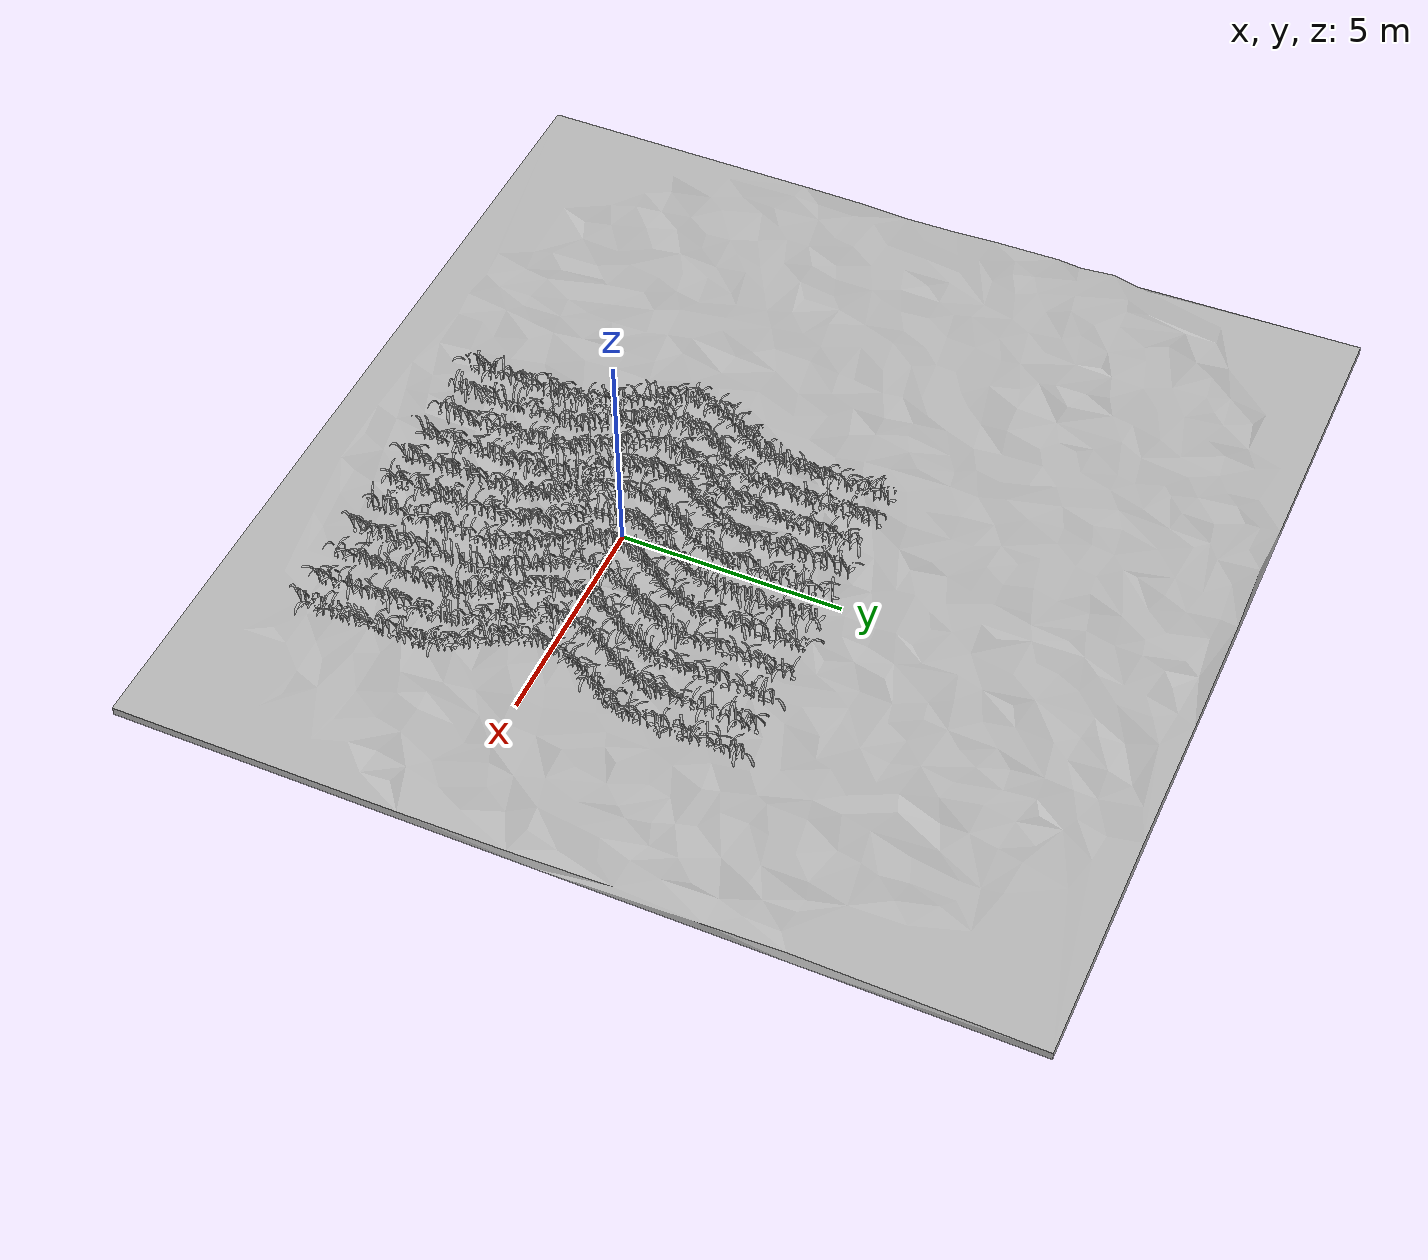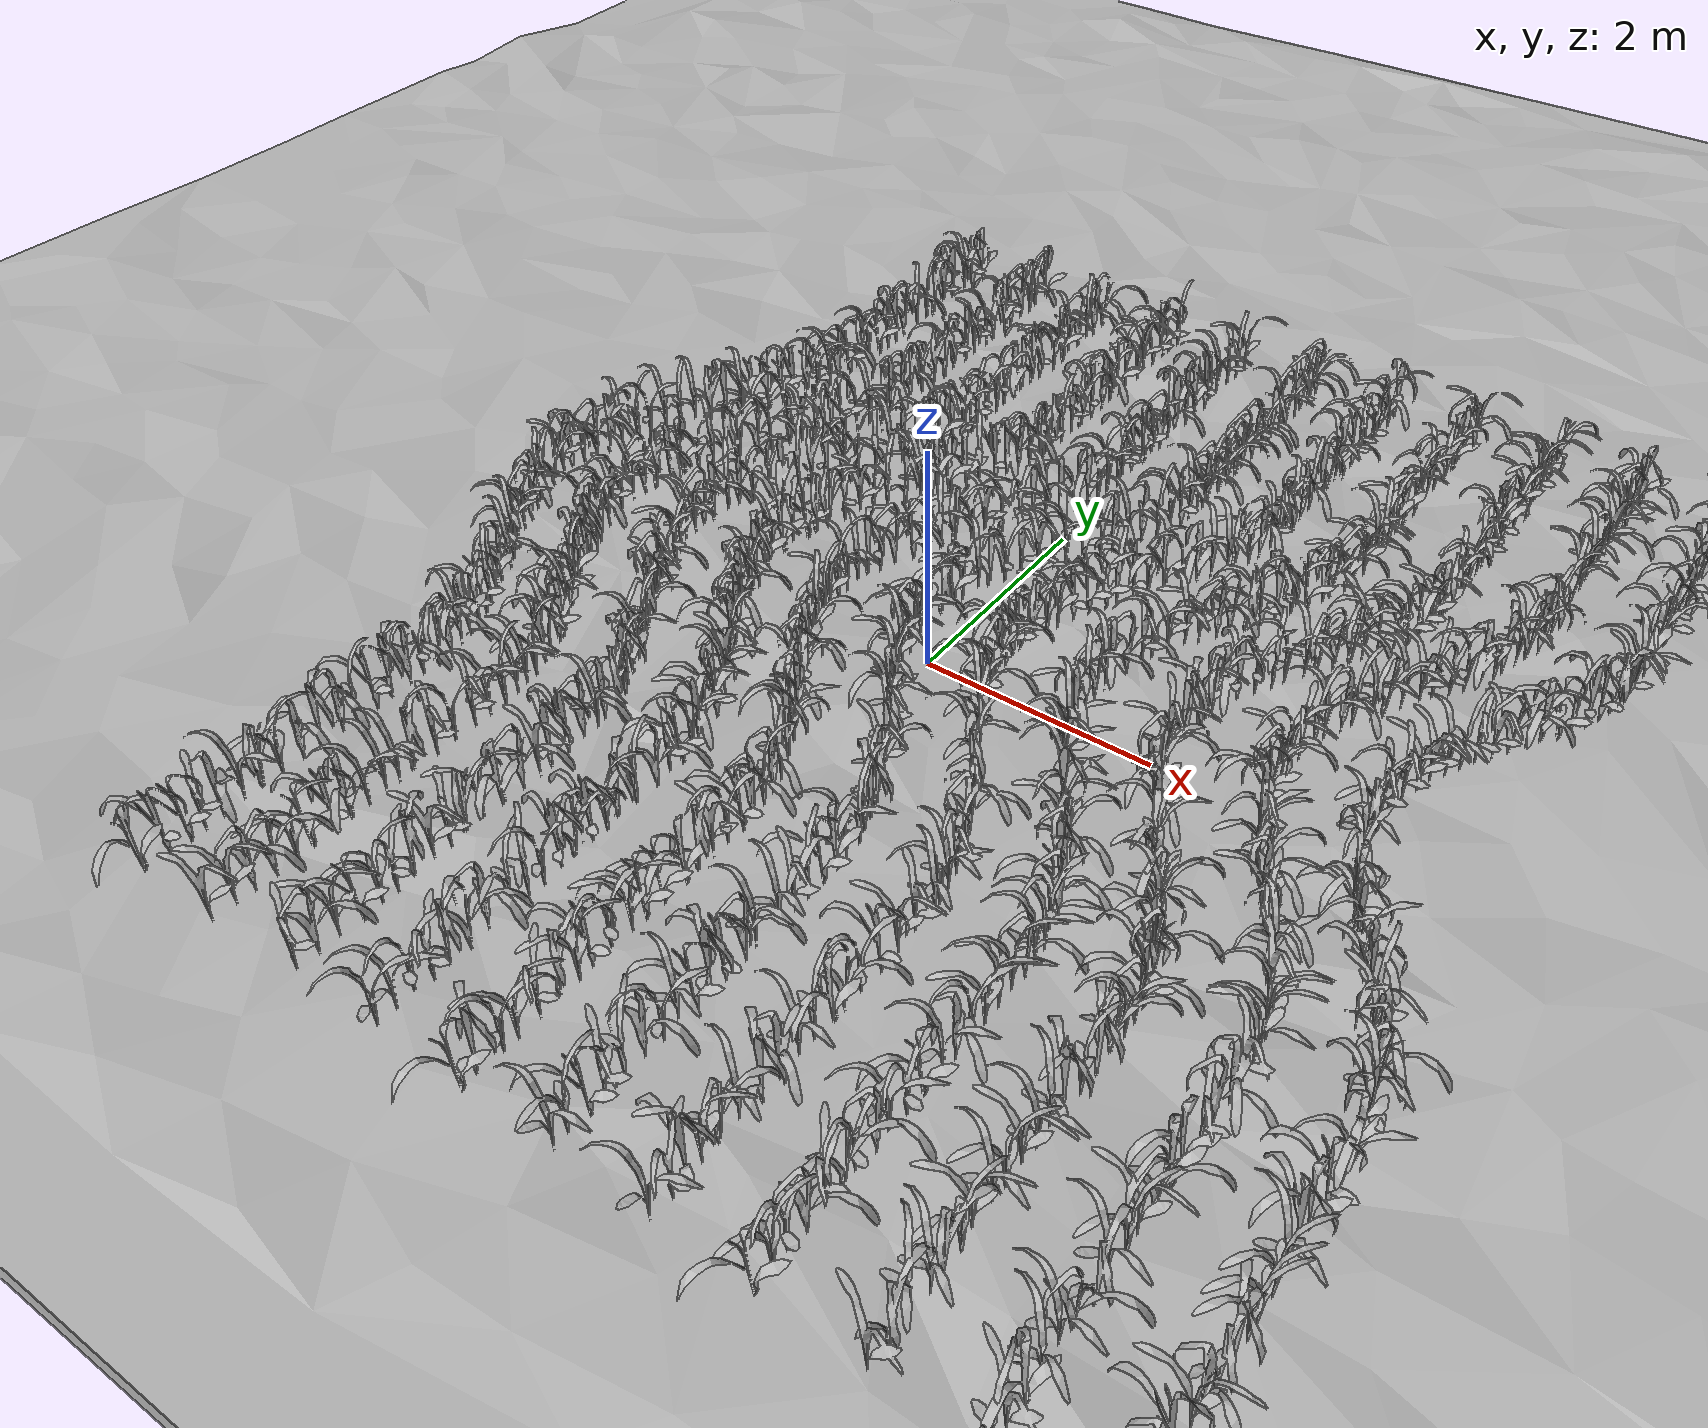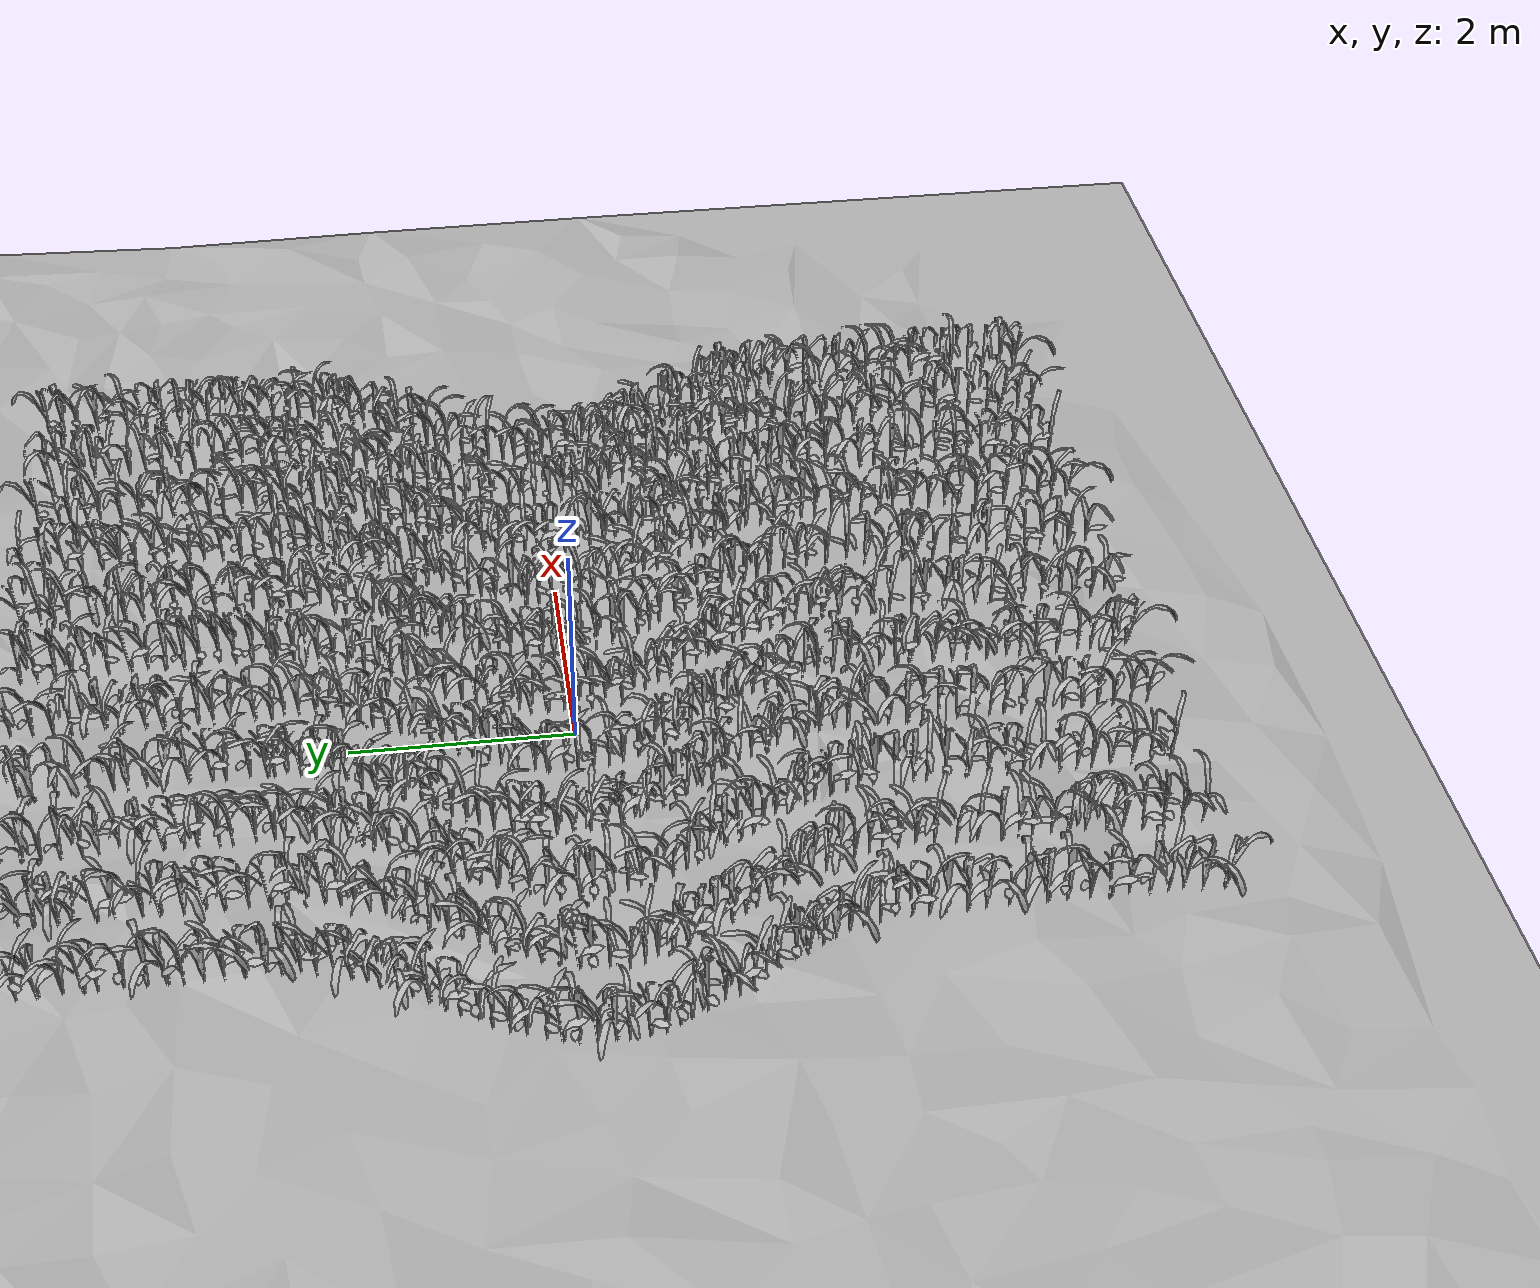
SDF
<sdf version="1.6">
 <world name="default">
  <light name="sun" type="directional">
   <pose>0 0 10 0 -0 0</pose>
   <diffuse>0.8 0.8 0.8 1</diffuse>
   <specular>0.2 0.2 0.2 1</specular>
   <attenuation>
    <range>1000</range>
    <constant>0.9</constant>
    <linear>0.01</linear>
    <quadratic>0.001</quadratic>
   </attenuation>
   <direction>-0.5 0.1 -0.9</direction>
  </light>
  <gravity>0 0 -9.8</gravity>
  <magnetic_field>6e-06 2.3e-05 -4.2e-05</magnetic_field>
  <atmosphere type="adiabatic"/>
  <physics name="default_physics" default="0" type="ode">
   <max_step_size>0.005</max_step_size>
   <real_time_factor>1</real_time_factor>
   <real_time_update_rate>200</real_time_update_rate>
  </physics>
  <scene>
   <sky><clouds><speed>12</speed></clouds></sky>
   <ambient>0.4 0.4 0.4 1</ambient>
   <background>0.7 0.7 0.7 1</background>
   <grid>false</grid>
   <shadows>1</shadows>
  </scene>
  <audio><device>default</device></audio>
  <spherical_coordinates>
   <surface_model>EARTH_WGS84</surface_model>
   <latitude_deg>0</latitude_deg>
   <longitude_deg>0</longitude_deg>
   <elevation>0</elevation>
   <heading_deg>0</heading_deg>
  </spherical_coordinates>
  <model name="custom_terrain">
   <static>1</static>
   <link name="link">
    <collision name="collision">
     <geometry><mesh><uri>model://custom_terrain/meshes/terrain.stl</uri></mesh></geometry>
    </collision>
    <visual name="visual">
     <geometry><mesh><uri>model://custom_terrain/meshes/terrain.stl</uri></mesh></geometry>
     <material>
      <script>
       <uri>model://custom_terrain/materials/scripts</uri>
       <uri>model://custom_terrain/materials/textures</uri>
       <name>custom_terrain/terrain</name>
      </script>
     </material>
    </visual>
   </link>
   <pose>-1.53507 2.74629 0.25 0 -0 0</pose>
  </model>
  <include>
   <uri>model://maize_01</uri>
   <pose>-2.8149662046243322 -5.036532200256407 0.2987472165300224 0.0 0.0 5.894875012676836</pose>
   <name>maize_01_0000</name>
   <static>true</static>
  </include>
  <include>
   <uri>model://maize_01</uri>
   <pose>-2.809477527307368 -4.8400392186208 0.2987472165300224 0.0 0.0 4.363037747194006</pose>
   <name>maize_01_0001</name>
   <static>true</static>
  </include>
  <include>
   <uri>model://maize_01</uri>
   <pose>-2.7934535225200245 -4.68458728142989 0.2987472165300224 0.0 0.0 4.82953336246158</pose>
   <name>maize_01_0002</name>
   <static>true</static>
  </include>
  <include>
   <uri>model://maize_02</uri>
   <pose>-2.796779158858809 -4.5589871454011 0.2987472165300224 0.0 0.0 4.8684863078724385</pose>
   <name>maize_02_0003</name>
   <static>true</static>
  </include>
  <include>
   <uri>model://maize_01</uri>
   <pose>-2.795504382018359 -4.414495596811592 0.2987472165300224 0.0 0.0 0.4380697121282974</pose>
   <name>maize_01_0004</name>
   <static>true</static>
  </include>
  <include>
   <uri>model://maize_02</uri>
   <pose>-2.810753175358018 -4.226863867417673 0.2987472165300224 0.0 0.0 2.5570488509744598</pose>
   <name>maize_02_0005</name>
   <static>true</static>
  </include>
  <include>
   <uri>model://maize_01</uri>
   <pose>-2.81115481818274 -4.068038992379891 0.2987472165300224 0.0 0.0 2.433150421425094</pose>
   <name>maize_01_0006</name>
   <static>true</static>
  </include>
  <include>
   <uri>model://maize_02</uri>
   <pose>-2.8059342616971032 -3.9068965869558956 0.2987472165300224 0.0 0.0 0.46947598814061914</pose>
   <name>maize_02_0007</name>
   <static>true</static>
  </include>
  <include>
   <uri>model://maize_01</uri>
   <pose>-2.795099697665013 -3.7324073315395716 0.2987472165300224 0.0 0.0 0.7222739742540812</pose>
   <name>maize_01_0008</name>
   <static>true</static>
  </include>
  <include>
   <uri>model://maize_01</uri>
   <pose>-2.8096855687190865 -3.5520285328730514 0.2987472165300224 0.0 0.0 3.2039003910198036</pose>
   <name>maize_01_0009</name>
   <static>true</static>
  </include>
  <include>
   <uri>model://maize_01</uri>
   <pose>-2.7974254057102166 -3.3761085308729215 0.2997633349279468 0.0 0.0 0.6338193416331112</pose>
   <name>maize_01_0010</name>
   <static>true</static>
  </include>
  <include>
   <uri>model://maize_02</uri>
   <pose>-2.7935960507060424 -3.2483509228334326 0.2997633349279468 0.0 0.0 0.8870863604376874</pose>
   <name>maize_02_0011</name>
   <static>true</static>
  </include>
  <include>
   <uri>model://maize_01</uri>
   <pose>-2.7944472227529724 -3.057295577552061 0.2997633349279468 0.0 0.0 4.464149751738774</pose>
   <name>maize_01_0012</name>
   <static>true</static>
  </include>
  <include>
   <uri>model://maize_01</uri>
   <pose>-2.8186819191843164 -2.8945732437068434 0.3000073711710849 0.0 0.0 3.1398318236015252</pose>
   <name>maize_01_0013</name>
   <static>true</static>
  </include>
  <include>
   <uri>model://maize_01</uri>
   <pose>-2.802429662213426 -2.732400205703364 0.3000073711710849 0.0 0.0 0.9747646402250957</pose>
   <name>maize_01_0014</name>
   <static>true</static>
  </include>
  <include>
   <uri>model://maize_02</uri>
   <pose>-2.8135162554699322 -2.5912148178040884 0.3000073711710849 0.0 0.0 4.017603059819496</pose>
   <name>maize_02_0015</name>
   <static>true</static>
  </include>
  <include>
   <uri>model://maize_01</uri>
   <pose>-2.7914492188478732 -2.445866679618181 0.3000073711710849 0.0 0.0 2.224783643792515</pose>
   <name>maize_01_0016</name>
   <static>true</static>
  </include>
  <include>
   <uri>model://maize_01</uri>
   <pose>-2.8083234187623902 -2.320516576724049 0.3000073711710849 0.0 0.0 0.9779870854339036</pose>
   <name>maize_01_0017</name>
   <static>true</static>
  </include>
  <include>
   <uri>model://maize_02</uri>
   <pose>-2.837392890390448 -2.18724849604011 0.3000073711710849 0.0 0.0 1.9218371855780423</pose>
   <name>maize_02_0018</name>
   <static>true</static>
  </include>
  <include>
   <uri>model://maize_01</uri>
   <pose>-2.877807266111874 -2.0593476101850006 0.3000073711710849 0.0 0.0 5.924432845800086</pose>
   <name>maize_01_0019</name>
   <static>true</static>
  </include>
  <include>
   <uri>model://maize_02</uri>
   <pose>-2.9191221647541665 -1.9238190918331617 0.3000073711710849 0.0 0.0 4.4604900075646245</pose>
   <name>maize_02_0020</name>
   <static>true</static>
  </include>
  <include>
   <uri>model://maize_01</uri>
   <pose>-2.978187307036609 -1.8011241727258536 0.3000073711710849 0.0 0.0 4.599854090873884</pose>
   <name>maize_01_0021</name>
   <static>true</static>
  </include>
  <include>
   <uri>model://maize_02</uri>
   <pose>-3.033159196684417 -1.6951025352394338 0.3000073711710849 0.0 0.0 1.3549015476638713</pose>
   <name>maize_02_0022</name>
   <static>true</static>
  </include>
  <include>
   <uri>model://maize_01</uri>
   <pose>-3.1022475428299114 -1.5675113088376633 0.3000073711710849 0.0 0.0 5.831072665439621</pose>
   <name>maize_01_0023</name>
   <static>true</static>
  </include>
  <include>
   <uri>model://maize_01</uri>
   <pose>-3.156738683040348 -1.4574072585174689 0.3000073711710849 0.0 0.0 1.1311388279408856</pose>
   <name>maize_01_0024</name>
   <static>true</static>
  </include>
  <include>
   <uri>model://maize_02</uri>
   <pose>-3.21237578114864 -1.3020230036605802 0.29996374720717184 0.0 0.0 1.7867516960716405</pose>
   <name>maize_02_0025</name>
   <static>true</static>
  </include>
  <include>
   <uri>model://maize_02</uri>
   <pose>-3.289669552640869 -1.1908592170727783 0.29996374720717184 0.0 0.0 3.5619589033067767</pose>
   <name>maize_02_0026</name>
   <static>true</static>
  </include>
  <include>
   <uri>model://maize_02</uri>
   <pose>-3.3761114003888917 -1.088862409862166 0.29996374720717184 0.0 0.0 1.6566801443292551</pose>
   <name>maize_02_0027</name>
   <static>true</static>
  </include>
  <include>
   <uri>model://maize_02</uri>
   <pose>-3.4727268601063535 -0.963268275777607 0.29996374720717184 0.0 0.0 3.033199364283431</pose>
   <name>maize_02_0028</name>
   <static>true</static>
  </include>
  <include>
   <uri>model://maize_02</uri>
   <pose>-3.5246826022600453 -0.8385261277293343 0.29996374720717184 0.0 0.0 5.922296670662413</pose>
   <name>maize_02_0029</name>
   <static>true</static>
  </include>
  <include>
   <uri>model://maize_01</uri>
   <pose>-3.5709355796475397 -0.7046268727632661 0.29996374720717184 0.0 0.0 1.444019920913299</pose>
   <name>maize_01_0030</name>
   <static>true</static>
  </include>
  <include>
   <uri>model://maize_01</uri>
   <pose>-3.6336448572200553 -0.5797594394287573 0.29996374720717184 0.0 0.0 0.32203183308587047</pose>
   <name>maize_01_0031</name>
   <static>true</static>
  </include>
  <include>
   <uri>model://maize_02</uri>
   <pose>-3.6983056275719206 -0.47543790865323454 0.29996374720717184 0.0 0.0 1.3373291784525114</pose>
   <name>maize_02_0032</name>
   <static>true</static>
  </include>
  <include>
   <uri>model://maize_02</uri>
   <pose>-3.7590402920883563 -0.36178569490712476 0.29996374720717184 0.0 0.0 4.432373684699861</pose>
   <name>maize_02_0033</name>
   <static>true</static>
  </include>
  <include>
   <uri>model://maize_01</uri>
   <pose>-3.7701742743428763 -0.23403609171343806 0.29996374720717184 0.0 0.0 1.928436748098162</pose>
   <name>maize_01_0034</name>
   <static>true</static>
  </include>
  <include>
   <uri>model://maize_02</uri>
   <pose>-3.8197929000685216 -0.0709651151405992 0.29996374720717184 0.0 0.0 5.416564040372484</pose>
   <name>maize_02_0035</name>
   <static>true</static>
  </include>
  <include>
   <uri>model://maize_01</uri>
   <pose>-3.806684685591808 0.029505206422192808 0.29996374720717184 0.0 0.0 3.5475983094386017</pose>
   <name>maize_01_0036</name>
   <static>true</static>
  </include>
  <include>
   <uri>model://maize_02</uri>
   <pose>-3.814997386128057 0.17218964874158374 0.29996374720717184 0.0 0.0 3.5945645470747056</pose>
   <name>maize_02_0037</name>
   <static>true</static>
  </include>
  <include>
   <uri>model://maize_01</uri>
   <pose>-3.7805645519390065 0.29776706583548784 0.29996374720717184 0.0 0.0 0.9751677136648172</pose>
   <name>maize_01_0038</name>
   <static>true</static>
  </include>
  <include>
   <uri>model://maize_01</uri>
   <pose>-3.75154350893001 0.4324213704299986 0.29996374720717184 0.0 0.0 2.637481799988699</pose>
   <name>maize_01_0039</name>
   <static>true</static>
  </include>
  <include>
   <uri>model://maize_02</uri>
   <pose>-3.7138634384057463 0.5444586199330479 0.29996374720717184 0.0 0.0 1.6638097893023662</pose>
   <name>maize_02_0040</name>
   <static>true</static>
  </include>
  <include>
   <uri>model://maize_02</uri>
   <pose>-3.6593590176361768 0.6955483673002896 0.29848455599888285 0.0 0.0 0.7532479405778126</pose>
   <name>maize_02_0041</name>
   <static>true</static>
  </include>
  <include>
   <uri>model://maize_02</uri>
   <pose>-3.6186664088523064 0.8206976326008066 0.29848455599888285 0.0 0.0 3.3877188875004</pose>
   <name>maize_02_0042</name>
   <static>true</static>
  </include>
  <include>
   <uri>model://maize_02</uri>
   <pose>-3.5588682635673226 0.9486220873171336 0.29848455599888285 0.0 0.0 1.8789709059621456</pose>
   <name>maize_02_0043</name>
   <static>true</static>
  </include>
  <include>
   <uri>model://maize_02</uri>
   <pose>-3.465593222750364 1.0479885955222044 0.29848455599888285 0.0 0.0 1.0933131055118652</pose>
   <name>maize_02_0044</name>
   <static>true</static>
  </include>
  <include>
   <uri>model://maize_02</uri>
   <pose>-3.411683429007456 1.1820069874353456 0.2982043722469985 0.0 0.0 1.6527585744892856</pose>
   <name>maize_02_0045</name>
   <static>true</static>
  </include>
  <include>
   <uri>model://maize_01</uri>
   <pose>-3.33287329180877 1.2994993584818009 0.2982043722469985 0.0 0.0 2.34209236018415</pose>
   <name>maize_01_0046</name>
   <static>true</static>
  </include>
  <include>
   <uri>model://maize_01</uri>
   <pose>-3.2457187403974967 1.4195931527424916 0.2982043722469985 0.0 0.0 3.29132313555353</pose>
   <name>maize_01_0047</name>
   <static>true</static>
  </include>
  <include>
   <uri>model://maize_02</uri>
   <pose>-3.166275716454551 1.5400794868964083 0.2982043722469985 0.0 0.0 1.5516897548225197</pose>
   <name>maize_02_0048</name>
   <static>true</static>
  </include>
  <include>
   <uri>model://maize_01</uri>
   <pose>-3.110683276291151 1.652461897299695 0.2982043722469985 0.0 0.0 4.07934664485429</pose>
   <name>maize_01_0049</name>
   <static>true</static>
  </include>
  <include>
   <uri>model://maize_01</uri>
   <pose>-3.0469831952849917 1.7756025071229369 0.2982043722469985 0.0 0.0 5.72240479932771</pose>
   <name>maize_01_0050</name>
   <static>true</static>
  </include>
  <include>
   <uri>model://maize_01</uri>
   <pose>-2.958707936638692 1.8830968784769884 0.2982043722469985 0.0 0.0 5.450141772464677</pose>
   <name>maize_01_0051</name>
   <static>true</static>
  </include>
  <include>
   <uri>model://maize_01</uri>
   <pose>-2.9341411990979305 2.008239952124765 0.2982043722469985 0.0 0.0 3.6667950107291687</pose>
   <name>maize_01_0052</name>
   <static>true</static>
  </include>
  <include>
   <uri>model://maize_01</uri>
   <pose>-2.882753894519122 2.1337361580634746 0.2982043722469985 0.0 0.0 2.240636867107684</pose>
   <name>maize_01_0053</name>
   <static>true</static>
  </include>
  <include>
   <uri>model://maize_02</uri>
   <pose>-2.8612924687123584 2.2731264341948347 0.2982043722469985 0.0 0.0 3.180619982938752</pose>
   <name>maize_02_0054</name>
   <static>true</static>
  </include>
  <include>
   <uri>model://maize_02</uri>
   <pose>-2.815142622731468 2.393848887765921 0.2982043722469985 0.0 0.0 2.4463569772142515</pose>
   <name>maize_02_0055</name>
   <static>true</static>
  </include>
  <include>
   <uri>model://maize_01</uri>
   <pose>-2.8234001030866533 2.527526291867423 0.2982043722469985 0.0 0.0 0.7985601553587602</pose>
   <name>maize_01_0056</name>
   <static>true</static>
  </include>
  <include>
   <uri>model://maize_01</uri>
   <pose>-2.8010024675499414 2.663909061125891 0.2982043722469985 0.0 0.0 4.533112907941982</pose>
   <name>maize_01_0057</name>
   <static>true</static>
  </include>
  <include>
   <uri>model://maize_01</uri>
   <pose>-2.8108692582706336 2.830536949664181 0.2982043722469985 0.0 0.0 2.343838983946525</pose>
   <name>maize_01_0058</name>
   <static>true</static>
  </include>
  <include>
   <uri>model://maize_02</uri>
   <pose>-2.812596920223234 2.98387975948749 0.2982043722469985 0.0 0.0 3.000006266848885</pose>
   <name>maize_02_0059</name>
   <static>true</static>
  </include>
  <include>
   <uri>model://maize_01</uri>
   <pose>-2.8086761119353008 3.1444475171472015 0.2982043722469985 0.0 0.0 5.021257378977484</pose>
   <name>maize_01_0060</name>
   <static>true</static>
  </include>
  <include>
   <uri>model://maize_02</uri>
   <pose>-2.8142713396046006 3.2982899075374843 0.2982043722469985 0.0 0.0 0.4224962342315828</pose>
   <name>maize_02_0061</name>
   <static>true</static>
  </include>
  <include>
   <uri>model://maize_01</uri>
   <pose>-2.808226895425301 3.4257579260319972 0.2982043722469985 0.0 0.0 3.375960717166941</pose>
   <name>maize_01_0062</name>
   <static>true</static>
  </include>
  <include>
   <uri>model://maize_01</uri>
   <pose>-2.816519908271905 3.5666328728694734 0.2982043722469985 0.0 0.0 1.0820851123227977</pose>
   <name>maize_01_0063</name>
   <static>true</static>
  </include>
  <include>
   <uri>model://maize_02</uri>
   <pose>-2.8017931775835483 3.754826489649544 0.2982043722469985 0.0 0.0 1.2191590458596095</pose>
   <name>maize_02_0064</name>
   <static>true</static>
  </include>
  <include>
   <uri>model://maize_02</uri>
   <pose>-2.8228457170812282 3.9504630266050964 0.2982043722469985 0.0 0.0 0.6864576247364175</pose>
   <name>maize_02_0065</name>
   <static>true</static>
  </include>
  <include>
   <uri>model://maize_01</uri>
   <pose>-2.813271631886931 4.0646402717936265 0.2982043722469985 0.0 0.0 2.6256518236481976</pose>
   <name>maize_01_0066</name>
   <static>true</static>
  </include>
  <include>
   <uri>model://maize_02</uri>
   <pose>-2.803572472237573 4.2234928043657085 0.2982043722469985 0.0 0.0 4.637083931156359</pose>
   <name>maize_02_0067</name>
   <static>true</static>
  </include>
  <include>
   <uri>model://maize_01</uri>
   <pose>-2.826844295379367 4.416965677002313 0.2982043722469985 0.0 0.0 3.239104611329377</pose>
   <name>maize_01_0068</name>
   <static>true</static>
  </include>
  <include>
   <uri>model://maize_02</uri>
   <pose>-2.8107380339709827 4.579905128530415 0.2982043722469985 0.0 0.0 1.7434663834114121</pose>
   <name>maize_02_0069</name>
   <static>true</static>
  </include>
  <include>
   <uri>model://maize_01</uri>
   <pose>-2.8086048481575077 4.725899969128392 0.2982043722469985 0.0 0.0 4.093139093344104</pose>
   <name>maize_01_0070</name>
   <static>true</static>
  </include>
  <include>
   <uri>model://maize_01</uri>
   <pose>-2.8088437665662473 4.907545699673854 0.2982043722469985 0.0 0.0 5.728342934287055</pose>
   <name>maize_01_0071</name>
   <static>true</static>
  </include>
  <include>
   <uri>model://maize_02</uri>
   <pose>-2.0720008120603652 -5.056959439686576 0.2986650895739808 0.0 0.0 5.433162248212113</pose>
   <name>maize_02_0072</name>
   <static>true</static>
  </include>
  <include>
   <uri>model://maize_02</uri>
   <pose>-2.0604202672663607 -4.876991809399276 0.2986650895739808 0.0 0.0 5.732482879605926</pose>
   <name>maize_02_0073</name>
   <static>true</static>
  </include>
  <include>
   <uri>model://maize_01</uri>
   <pose>-2.0623178033263856 -4.728139188529193 0.2986650895739808 0.0 0.0 1.1685631404289298</pose>
   <name>maize_01_0074</name>
   <static>true</static>
  </include>
  <include>
   <uri>model://maize_01</uri>
   <pose>-2.0725461581432794 -4.546987889401581 0.2986650895739808 0.0 0.0 1.6788264592846718</pose>
   <name>maize_01_0075</name>
   <static>true</static>
  </include>
  <include>
   <uri>model://maize_02</uri>
   <pose>-2.045092617244395 -4.389387876042935 0.29950354338867896 0.0 0.0 0.2961285172845409</pose>
   <name>maize_02_0076</name>
   <static>true</static>
  </include>
  <include>
   <uri>model://maize_01</uri>
   <pose>-2.0723696797346842 -4.247816933443073 0.29950354338867896 0.0 0.0 5.338776407005515</pose>
   <name>maize_01_0077</name>
   <static>true</static>
  </include>
  <include>
   <uri>model://maize_01</uri>
   <pose>-2.051345492641678 -4.060346822229589 0.29950354338867896 0.0 0.0 4.309868092103136</pose>
   <name>maize_01_0078</name>
   <static>true</static>
  </include>
  <include>
   <uri>model://maize_01</uri>
   <pose>-2.061749816803312 -3.9255076257861146 0.29950354338867896 0.0 0.0 6.275968553937282</pose>
   <name>maize_01_0079</name>
   <static>true</static>
  </include>
  <include>
   <uri>model://maize_02</uri>
   <pose>-2.0497267231624785 -3.7733650203013442 0.2997755151784565 0.0 0.0 2.9649433481723713</pose>
   <name>maize_02_0080</name>
   <static>true</static>
  </include>
  <include>
   <uri>model://maize_02</uri>
   <pose>-2.0664115051492202 -3.6102853509258717 0.2997755151784565 0.0 0.0 2.3529346517370366</pose>
   <name>maize_02_0081</name>
   <static>true</static>
  </include>
  <include>
   <uri>model://maize_02</uri>
   <pose>-2.057536152541018 -3.496669215509953 0.2997755151784565 0.0 0.0 2.2343980601328997</pose>
   <name>maize_02_0082</name>
   <static>true</static>
  </include>
  <include>
   <uri>model://maize_01</uri>
   <pose>-2.0747892759641062 -3.3461553845241734 0.2997755151784565 0.0 0.0 2.995296953165401</pose>
   <name>maize_01_0083</name>
   <static>true</static>
  </include>
  <include>
   <uri>model://maize_02</uri>
   <pose>-2.042679067957536 -3.153340965036183 0.3005045593256401 0.0 0.0 4.853848408779754</pose>
   <name>maize_02_0084</name>
   <static>true</static>
  </include>
  <include>
   <uri>model://maize_02</uri>
   <pose>-2.066312806527844 -2.966736639688672 0.3005045593256401 0.0 0.0 3.4791285214319725</pose>
   <name>maize_02_0085</name>
   <static>true</static>
  </include>
  <include>
   <uri>model://maize_02</uri>
   <pose>-2.0472140212766807 -2.785227585283933 0.300505825426684 0.0 0.0 4.858011875261052</pose>
   <name>maize_02_0086</name>
   <static>true</static>
  </include>
  <include>
   <uri>model://maize_02</uri>
   <pose>-2.063437150846898 -2.6285160418578157 0.300505825426684 0.0 0.0 2.7062252617887546</pose>
   <name>maize_02_0087</name>
   <static>true</static>
  </include>
  <include>
   <uri>model://maize_02</uri>
   <pose>-2.0566367955301925 -2.48322024594746 0.300505825426684 0.0 0.0 0.8330236726733005</pose>
   <name>maize_02_0088</name>
   <static>true</static>
  </include>
  <include>
   <uri>model://maize_02</uri>
   <pose>-2.0588659573190085 -2.353149874308976 0.300505825426684 0.0 0.0 2.5830930511308527</pose>
   <name>maize_02_0089</name>
   <static>true</static>
  </include>
  <include>
   <uri>model://maize_02</uri>
   <pose>-2.0807914285906284 -2.239024802362115 0.300505825426684 0.0 0.0 2.3634920312108387</pose>
   <name>maize_02_0090</name>
   <static>true</static>
  </include>
  <include>
   <uri>model://maize_02</uri>
   <pose>-2.117711133443916 -2.108787300687137 0.300505825426684 0.0 0.0 0.5130881768126063</pose>
   <name>maize_02_0091</name>
   <static>true</static>
  </include>
  <include>
   <uri>model://maize_01</uri>
   <pose>-2.1458165295815115 -1.9753276451150692 0.300505825426684 0.0 0.0 3.6449755504775903</pose>
   <name>maize_01_0092</name>
   <static>true</static>
  </include>
  <include>
   <uri>model://maize_02</uri>
   <pose>-2.2190546041360117 -1.858409822132397 0.300505825426684 0.0 0.0 1.8884098040305333</pose>
   <name>maize_02_0093</name>
   <static>true</static>
  </include>
  <include>
   <uri>model://maize_01</uri>
   <pose>-2.2611791398209795 -1.7240152191247777 0.300505825426684 0.0 0.0 4.726343638161984</pose>
   <name>maize_01_0094</name>
   <static>true</static>
  </include>
  <include>
   <uri>model://maize_01</uri>
   <pose>-2.320630989299302 -1.6092773375165412 0.300505825426684 0.0 0.0 6.02268871512266</pose>
   <name>maize_01_0095</name>
   <static>true</static>
  </include>
  <include>
   <uri>model://maize_02</uri>
   <pose>-2.3890988468553354 -1.4864337133009748 0.300505825426684 0.0 0.0 2.2241346780266924</pose>
   <name>maize_02_0096</name>
   <static>true</static>
  </include>
  <include>
   <uri>model://maize_01</uri>
   <pose>-2.4942296603595113 -1.3516524418493538 0.300505825426684 0.0 0.0 5.067955373351796</pose>
   <name>maize_01_0097</name>
   <static>true</static>
  </include>
  <include>
   <uri>model://maize_02</uri>
   <pose>-2.573086142763024 -1.2311695660069628 0.300505825426684 0.0 0.0 0.9613515812656785</pose>
   <name>maize_02_0098</name>
   <static>true</static>
  </include>
  <include>
   <uri>model://maize_01</uri>
   <pose>-2.630314857241284 -1.1434964820458988 0.300505825426684 0.0 0.0 5.491621203564096</pose>
   <name>maize_01_0099</name>
   <static>true</static>
  </include>
  <include>
   <uri>model://maize_01</uri>
   <pose>-2.7142903294187075 -1.0083810267722384 0.300505825426684 0.0 0.0 3.459822099916455</pose>
   <name>maize_01_0100</name>
   <static>true</static>
  </include>
  <include>
   <uri>model://maize_01</uri>
   <pose>-2.773728321742444 -0.8762836748789267 0.300505825426684 0.0 0.0 3.269543029325392</pose>
   <name>maize_01_0101</name>
   <static>true</static>
  </include>
  <include>
   <uri>model://maize_01</uri>
   <pose>-2.847788245085764 -0.7546529631284506 0.300505825426684 0.0 0.0 3.0701469808381074</pose>
   <name>maize_01_0102</name>
   <static>true</static>
  </include>
  <include>
   <uri>model://maize_01</uri>
   <pose>-2.904778033747554 -0.6277956100735087 0.300505825426684 0.0 0.0 2.594812522642346</pose>
   <name>maize_01_0103</name>
   <static>true</static>
  </include>
  <include>
   <uri>model://maize_01</uri>
   <pose>-2.9676050878941513 -0.5191920914986274 0.300505825426684 0.0 0.0 0.5379837514329018</pose>
   <name>maize_01_0104</name>
   <static>true</static>
  </include>
  <include>
   <uri>model://maize_02</uri>
   <pose>-2.9955162819864367 -0.38191205657055227 0.300505825426684 0.0 0.0 3.0625700837478673</pose>
   <name>maize_02_0105</name>
   <static>true</static>
  </include>
  <include>
   <uri>model://maize_02</uri>
   <pose>-3.0320076345429503 -0.2770077266592439 0.300505825426684 0.0 0.0 4.965961374182776</pose>
   <name>maize_02_0106</name>
   <static>true</static>
  </include>
  <include>
   <uri>model://maize_02</uri>
   <pose>-3.067194131138379 -0.15428538780746123 0.300505825426684 0.0 0.0 3.4804155298784614</pose>
   <name>maize_02_0107</name>
   <static>true</static>
  </include>
  <include>
   <uri>model://maize_02</uri>
   <pose>-3.071662777670995 -0.0016926489327839592 0.300505825426684 0.0 0.0 2.1953502086446695</pose>
   <name>maize_02_0108</name>
   <static>true</static>
  </include>
  <include>
   <uri>model://maize_01</uri>
   <pose>-3.0631499423372737 0.13571776241661773 0.300505825426684 0.0 0.0 1.29414560182953</pose>
   <name>maize_01_0109</name>
   <static>true</static>
  </include>
  <include>
   <uri>model://maize_01</uri>
   <pose>-3.029583303520338 0.24253886618505519 0.300505825426684 0.0 0.0 2.536471110758194</pose>
   <name>maize_01_0110</name>
   <static>true</static>
  </include>
  <include>
   <uri>model://maize_01</uri>
   <pose>-2.9934746946191417 0.3774482421769554 0.300505825426684 0.0 0.0 0.15185196749731117</pose>
   <name>maize_01_0111</name>
   <static>true</static>
  </include>
  <include>
   <uri>model://maize_01</uri>
   <pose>-2.9674895751792856 0.5152084396135079 0.300505825426684 0.0 0.0 5.389643841637908</pose>
   <name>maize_01_0112</name>
   <static>true</static>
  </include>
  <include>
   <uri>model://maize_02</uri>
   <pose>-2.897340159284541 0.6345609350804786 0.300505825426684 0.0 0.0 6.263939836811219</pose>
   <name>maize_02_0113</name>
   <static>true</static>
  </include>
  <include>
   <uri>model://maize_02</uri>
   <pose>-2.8552905087938885 0.773244703117488 0.300505825426684 0.0 0.0 1.646851048940415</pose>
   <name>maize_02_0114</name>
   <static>true</static>
  </include>
  <include>
   <uri>model://maize_01</uri>
   <pose>-2.8007281405479216 0.8915679482909875 0.300505825426684 0.0 0.0 2.727980733055704</pose>
   <name>maize_01_0115</name>
   <static>true</static>
  </include>
  <include>
   <uri>model://maize_02</uri>
   <pose>-2.7363834927109982 1.0000211039638567 0.300505825426684 0.0 0.0 3.4301790056863046</pose>
   <name>maize_02_0116</name>
   <static>true</static>
  </include>
  <include>
   <uri>model://maize_01</uri>
   <pose>-2.6340597301414808 1.118295850125823 0.300505825426684 0.0 0.0 1.0052894689784557</pose>
   <name>maize_01_0117</name>
   <static>true</static>
  </include>
  <include>
   <uri>model://maize_02</uri>
   <pose>-2.568398545969396 1.2332837002279524 0.300505825426684 0.0 0.0 2.873647767402229</pose>
   <name>maize_02_0118</name>
   <static>true</static>
  </include>
  <include>
   <uri>model://maize_01</uri>
   <pose>-2.484786740471702 1.3758086545543426 0.300505825426684 0.0 0.0 0.46832249987270613</pose>
   <name>maize_01_0119</name>
   <static>true</static>
  </include>
  <include>
   <uri>model://maize_02</uri>
   <pose>-2.4144060460267416 1.4766404306523626 0.300505825426684 0.0 0.0 4.814605875961055</pose>
   <name>maize_02_0120</name>
   <static>true</static>
  </include>
  <include>
   <uri>model://maize_01</uri>
   <pose>-2.3647276746581807 1.5952748552985974 0.300505825426684 0.0 0.0 2.740760657847672</pose>
   <name>maize_01_0121</name>
   <static>true</static>
  </include>
  <include>
   <uri>model://maize_02</uri>
   <pose>-2.276895920161837 1.719855374504512 0.300505825426684 0.0 0.0 4.132216136375487</pose>
   <name>maize_02_0122</name>
   <static>true</static>
  </include>
  <include>
   <uri>model://maize_01</uri>
   <pose>-2.2433147305768695 1.843888308335566 0.300505825426684 0.0 0.0 5.058546130496538</pose>
   <name>maize_01_0123</name>
   <static>true</static>
  </include>
  <include>
   <uri>model://maize_02</uri>
   <pose>-2.174464077212094 1.958991145310596 0.300505825426684 0.0 0.0 2.743386996837504</pose>
   <name>maize_02_0124</name>
   <static>true</static>
  </include>
  <include>
   <uri>model://maize_02</uri>
   <pose>-2.1273825941296973 2.0755283462458185 0.300505825426684 0.0 0.0 1.7932437179524456</pose>
   <name>maize_02_0125</name>
   <static>true</static>
  </include>
  <include>
   <uri>model://maize_01</uri>
   <pose>-2.0796680367477065 2.207027939025395 0.300505825426684 0.0 0.0 2.453119374134885</pose>
   <name>maize_01_0126</name>
   <static>true</static>
  </include>
  <include>
   <uri>model://maize_01</uri>
   <pose>-2.0888724132260577 2.3482819995690565 0.300505825426684 0.0 0.0 0.19607125075351584</pose>
   <name>maize_01_0127</name>
   <static>true</static>
  </include>
  <include>
   <uri>model://maize_01</uri>
   <pose>-2.0681259275712587 2.490049106400693 0.300505825426684 0.0 0.0 0.6608104494407534</pose>
   <name>maize_01_0128</name>
   <static>true</static>
  </include>
  <include>
   <uri>model://maize_01</uri>
   <pose>-2.0720729632011996 2.6387529290157254 0.300505825426684 0.0 0.0 2.666755859976712</pose>
   <name>maize_01_0129</name>
   <static>true</static>
  </include>
  <include>
   <uri>model://maize_02</uri>
   <pose>-2.063423611139003 2.8068321301294126 0.300505825426684 0.0 0.0 3.7884513864261655</pose>
   <name>maize_02_0130</name>
   <static>true</static>
  </include>
  <include>
   <uri>model://maize_01</uri>
   <pose>-2.0653216182204592 3.0027908030119144 0.300505825426684 0.0 0.0 2.232423541817503</pose>
   <name>maize_01_0131</name>
   <static>true</static>
  </include>
  <include>
   <uri>model://maize_01</uri>
   <pose>-2.043150254214635 3.1576973456117146 0.300505825426684 0.0 0.0 2.720043961667873</pose>
   <name>maize_01_0132</name>
   <static>true</static>
  </include>
  <include>
   <uri>model://maize_01</uri>
   <pose>-2.07908513101525 3.3230099310436967 0.29948212133912644 0.0 0.0 4.409894351131748</pose>
   <name>maize_01_0133</name>
   <static>true</static>
  </include>
  <include>
   <uri>model://maize_01</uri>
   <pose>-2.050698500959015 3.514422943294449 0.29948212133912644 0.0 0.0 2.953256278456605</pose>
   <name>maize_01_0134</name>
   <static>true</static>
  </include>
  <include>
   <uri>model://maize_02</uri>
   <pose>-2.0512296858966415 3.6505984547191237 0.29948212133912644 0.0 0.0 4.881407689846183</pose>
   <name>maize_02_0135</name>
   <static>true</static>
  </include>
  <include>
   <uri>model://maize_02</uri>
   <pose>-2.0581621270970714 3.8648975837102193 0.2995843190798846 0.0 0.0 2.76897084215963</pose>
   <name>maize_02_0136</name>
   <static>true</static>
  </include>
  <include>
   <uri>model://maize_01</uri>
   <pose>-2.071797977185978 4.011679782256438 0.2995843190798846 0.0 0.0 2.581832657028505</pose>
   <name>maize_01_0137</name>
   <static>true</static>
  </include>
  <include>
   <uri>model://maize_01</uri>
   <pose>-2.061604632896655 4.190698355254343 0.2995843190798846 0.0 0.0 5.794762692837692</pose>
   <name>maize_01_0138</name>
   <static>true</static>
  </include>
  <include>
   <uri>model://maize_01</uri>
   <pose>-2.0743169377846415 4.315830425969288 0.2995843190798846 0.0 0.0 3.953977338304685</pose>
   <name>maize_01_0139</name>
   <static>true</static>
  </include>
  <include>
   <uri>model://maize_01</uri>
   <pose>-2.068328190269651 4.489713975633965 0.2995843190798846 0.0 0.0 0.6829312402032905</pose>
   <name>maize_01_0140</name>
   <static>true</static>
  </include>
  <include>
   <uri>model://maize_02</uri>
   <pose>-2.0532391883938956 4.626148058171054 0.2995843190798846 0.0 0.0 0.5376617927121125</pose>
   <name>maize_02_0141</name>
   <static>true</static>
  </include>
  <include>
   <uri>model://maize_02</uri>
   <pose>-2.076405547719786 4.768070377561786 0.2995843190798846 0.0 0.0 3.974890464088116</pose>
   <name>maize_02_0142</name>
   <static>true</static>
  </include>
  <include>
   <uri>model://maize_01</uri>
   <pose>-2.068803812529074 4.957547343021288 0.2995843190798846 0.0 0.0 5.159817521612146</pose>
   <name>maize_01_0143</name>
   <static>true</static>
  </include>
  <include>
   <uri>model://maize_02</uri>
   <pose>-1.3176883264639188 -4.999122001130901 0.30100728106067154 0.0 0.0 4.849215149881769</pose>
   <name>maize_02_0144</name>
   <static>true</static>
  </include>
  <include>
   <uri>model://maize_01</uri>
   <pose>-1.3044441138169038 -4.833652269453594 0.30100728106067154 0.0 0.0 1.3756970445543548</pose>
   <name>maize_01_0145</name>
   <static>true</static>
  </include>
  <include>
   <uri>model://maize_02</uri>
   <pose>-1.3159288714915969 -4.6611741501691295 0.3007635409578325 0.0 0.0 5.9312387431311775</pose>
   <name>maize_02_0146</name>
   <static>true</static>
  </include>
  <include>
   <uri>model://maize_01</uri>
   <pose>-1.2928783217639552 -4.4840702878999315 0.3007635409578325 0.0 0.0 5.0212429052187035</pose>
   <name>maize_01_0147</name>
   <static>true</static>
  </include>
  <include>
   <uri>model://maize_02</uri>
   <pose>-1.308439348235581 -4.313289320598604 0.3007635409578325 0.0 0.0 0.376532094322456</pose>
   <name>maize_02_0148</name>
   <static>true</static>
  </include>
  <include>
   <uri>model://maize_02</uri>
   <pose>-1.2989530972423815 -4.185526734124149 0.3007635409578325 0.0 0.0 4.370226161553686</pose>
   <name>maize_02_0149</name>
   <static>true</static>
  </include>
  <include>
   <uri>model://maize_01</uri>
   <pose>-1.3165651393649427 -4.025469003011236 0.30078746926215977 0.0 0.0 2.986218794013947</pose>
   <name>maize_01_0150</name>
   <static>true</static>
  </include>
  <include>
   <uri>model://maize_02</uri>
   <pose>-1.3037715092593978 -3.860668101711862 0.30078746926215977 0.0 0.0 5.359588284860161</pose>
   <name>maize_02_0151</name>
   <static>true</static>
  </include>
  <include>
   <uri>model://maize_02</uri>
   <pose>-1.297380330083812 -3.7162183948160394 0.30078746926215977 0.0 0.0 4.736490804135788</pose>
   <name>maize_02_0152</name>
   <static>true</static>
  </include>
  <include>
   <uri>model://maize_01</uri>
   <pose>-1.316166406136525 -3.565118656605389 0.30078746926215977 0.0 0.0 2.4582620892883096</pose>
   <name>maize_01_0153</name>
   <static>true</static>
  </include>
  <include>
   <uri>model://maize_02</uri>
   <pose>-1.3258450556121775 -3.3975421460514297 0.30078746926215977 0.0 0.0 6.063569559256593</pose>
   <name>maize_02_0154</name>
   <static>true</static>
  </include>
  <include>
   <uri>model://maize_01</uri>
   <pose>-1.3098911376527915 -3.235330778236067 0.30078746926215977 0.0 0.0 6.0332334576997955</pose>
   <name>maize_01_0155</name>
   <static>true</static>
  </include>
  <include>
   <uri>model://maize_01</uri>
   <pose>-1.3108965167358584 -3.036259954309828 0.30078746926215977 0.0 0.0 1.1230082805051085</pose>
   <name>maize_01_0156</name>
   <static>true</static>
  </include>
  <include>
   <uri>model://maize_02</uri>
   <pose>-1.307170840577107 -2.8743595657683105 0.30078746926215977 0.0 0.0 5.164042835300947</pose>
   <name>maize_02_0157</name>
   <static>true</static>
  </include>
  <include>
   <uri>model://maize_01</uri>
   <pose>-1.305677983968858 -2.758904982072988 0.30078746926215977 0.0 0.0 3.4325214249086438</pose>
   <name>maize_01_0158</name>
   <static>true</static>
  </include>
  <include>
   <uri>model://maize_01</uri>
   <pose>-1.300446603800064 -2.5928284588072223 0.30078746926215977 0.0 0.0 3.7686745329111035</pose>
   <name>maize_01_0159</name>
   <static>true</static>
  </include>
  <include>
   <uri>model://maize_01</uri>
   <pose>-1.3223449868264716 -2.4215631675854965 0.3011803336721711 0.0 0.0 1.0015635458264844</pose>
   <name>maize_01_0160</name>
   <static>true</static>
  </include>
  <include>
   <uri>model://maize_02</uri>
   <pose>-1.3083756452233664 -2.291093184187044 0.3011803336721711 0.0 0.0 2.1199460107793624</pose>
   <name>maize_02_0161</name>
   <static>true</static>
  </include>
  <include>
   <uri>model://maize_01</uri>
   <pose>-1.3374953898736959 -2.1919094751587656 0.3011803336721711 0.0 0.0 0.41508934552433835</pose>
   <name>maize_01_0162</name>
   <static>true</static>
  </include>
  <include>
   <uri>model://maize_01</uri>
   <pose>-1.3606913270861682 -2.0415580921484486 0.3011803336721711 0.0 0.0 2.624029974497765</pose>
   <name>maize_01_0163</name>
   <static>true</static>
  </include>
  <include>
   <uri>model://maize_02</uri>
   <pose>-1.4101097088631314 -1.8960116514780283 0.3011803336721711 0.0 0.0 0.7113395896714589</pose>
   <name>maize_02_0164</name>
   <static>true</static>
  </include>
  <include>
   <uri>model://maize_01</uri>
   <pose>-1.4610827351109983 -1.808749535708244 0.3011803336721711 0.0 0.0 3.3918469497681047</pose>
   <name>maize_01_0165</name>
   <static>true</static>
  </include>
  <include>
   <uri>model://maize_01</uri>
   <pose>-1.5349828829869294 -1.6830370677482176 0.3011803336721711 0.0 0.0 6.011367915225509</pose>
   <name>maize_01_0166</name>
   <static>true</static>
  </include>
  <include>
   <uri>model://maize_02</uri>
   <pose>-1.6027118939284783 -1.5364710748824775 0.3011995378273948 0.0 0.0 2.508097887463512</pose>
   <name>maize_02_0167</name>
   <static>true</static>
  </include>
  <include>
   <uri>model://maize_02</uri>
   <pose>-1.6590169220022284 -1.4166918494185994 0.3011995378273948 0.0 0.0 0.7554248168794033</pose>
   <name>maize_02_0168</name>
   <static>true</static>
  </include>
  <include>
   <uri>model://maize_01</uri>
   <pose>-1.7266297485310702 -1.3281589076374771 0.3011995378273948 0.0 0.0 1.7499426716465458</pose>
   <name>maize_01_0169</name>
   <static>true</static>
  </include>
  <include>
   <uri>model://maize_01</uri>
   <pose>-1.8022569708049965 -1.2008077772055523 0.3011995378273948 0.0 0.0 2.667518439792506</pose>
   <name>maize_01_0170</name>
   <static>true</static>
  </include>
  <include>
   <uri>model://maize_01</uri>
   <pose>-1.868827663570576 -1.0692819059104568 0.3011995378273948 0.0 0.0 3.5063519383323656</pose>
   <name>maize_01_0171</name>
   <static>true</static>
  </include>
  <include>
   <uri>model://maize_02</uri>
   <pose>-1.9535512376096669 -0.939154619003064 0.3011995378273948 0.0 0.0 5.065966410210677</pose>
   <name>maize_02_0172</name>
   <static>true</static>
  </include>
  <include>
   <uri>model://maize_01</uri>
   <pose>-2.0345850742373504 -0.8331138934803197 0.3011995378273948 0.0 0.0 1.231542235374328</pose>
   <name>maize_01_0173</name>
   <static>true</static>
  </include>
  <include>
   <uri>model://maize_02</uri>
   <pose>-2.0921316490407706 -0.7253437910571658 0.3011995378273948 0.0 0.0 4.674769182995641</pose>
   <name>maize_02_0174</name>
   <static>true</static>
  </include>
  <include>
   <uri>model://maize_02</uri>
   <pose>-2.1534638653071183 -0.6047311898719723 0.3011995378273948 0.0 0.0 3.548609825304612</pose>
   <name>maize_02_0175</name>
   <static>true</static>
  </include>
  <include>
   <uri>model://maize_02</uri>
   <pose>-2.189001440753812 -0.4575244177267066 0.3011995378273948 0.0 0.0 4.0527753134339966</pose>
   <name>maize_02_0176</name>
   <static>true</static>
  </include>
  <include>
   <uri>model://maize_02</uri>
   <pose>-2.2462021023254306 -0.3330974693422728 0.3011995378273948 0.0 0.0 6.10786046784121</pose>
   <name>maize_02_0177</name>
   <static>true</static>
  </include>
  <include>
   <uri>model://maize_02</uri>
   <pose>-2.2753260639527375 -0.22967391756535058 0.3011995378273948 0.0 0.0 2.1994728526236282</pose>
   <name>maize_02_0178</name>
   <static>true</static>
  </include>
  <include>
   <uri>model://maize_02</uri>
   <pose>-2.3181071224646943 -0.066014635583415 0.3011995378273948 0.0 0.0 5.340951493543089</pose>
   <name>maize_02_0179</name>
   <static>true</static>
  </include>
  <include>
   <uri>model://maize_01</uri>
   <pose>-2.3192877968285512 0.05013810938732568 0.3011995378273948 0.0 0.0 1.2291290102117494</pose>
   <name>maize_01_0180</name>
   <static>true</static>
  </include>
  <include>
   <uri>model://maize_01</uri>
   <pose>-2.3113091853576537 0.16525977314526966 0.3011995378273948 0.0 0.0 3.122018030358863</pose>
   <name>maize_01_0181</name>
   <static>true</static>
  </include>
  <include>
   <uri>model://maize_02</uri>
   <pose>-2.2935873338157826 0.3207388325138052 0.2989015414042212 0.0 0.0 1.2918308484348826</pose>
   <name>maize_02_0182</name>
   <static>true</static>
  </include>
  <include>
   <uri>model://maize_01</uri>
   <pose>-2.260889165147439 0.4226798962201477 0.2989015414042212 0.0 0.0 0.7070471617380067</pose>
   <name>maize_01_0183</name>
   <static>true</static>
  </include>
  <include>
   <uri>model://maize_02</uri>
   <pose>-2.2144179942587985 0.561719384466856 0.2989015414042212 0.0 0.0 0.041559683566424165</pose>
   <name>maize_02_0184</name>
   <static>true</static>
  </include>
  <include>
   <uri>model://maize_02</uri>
   <pose>-2.1489883930611318 0.6938572299630714 0.2989015414042212 0.0 0.0 3.8080199315961396</pose>
   <name>maize_02_0185</name>
   <static>true</static>
  </include>
  <include>
   <uri>model://maize_01</uri>
   <pose>-2.0970058236770184 0.8033105030720773 0.2989015414042212 0.0 0.0 6.152383216095607</pose>
   <name>maize_01_0186</name>
   <static>true</static>
  </include>
  <include>
   <uri>model://maize_02</uri>
   <pose>-2.0417429015046547 0.9501652688290003 0.2979473891782632 0.0 0.0 1.1145923660857613</pose>
   <name>maize_02_0187</name>
   <static>true</static>
  </include>
  <include>
   <uri>model://maize_01</uri>
   <pose>-1.9875076541819074 1.049169617692254 0.2979473891782632 0.0 0.0 2.353385384307319</pose>
   <name>maize_01_0188</name>
   <static>true</static>
  </include>
  <include>
   <uri>model://maize_01</uri>
   <pose>-1.89934903571569 1.1696773101249562 0.2979473891782632 0.0 0.0 3.2181343832629037</pose>
   <name>maize_01_0189</name>
   <static>true</static>
  </include>
  <include>
   <uri>model://maize_01</uri>
   <pose>-1.8226102556755464 1.295989423740567 0.2979473891782632 0.0 0.0 0.8756524589608817</pose>
   <name>maize_01_0190</name>
   <static>true</static>
  </include>
  <include>
   <uri>model://maize_02</uri>
   <pose>-1.7610097015330022 1.4170629023125623 0.2979473891782632 0.0 0.0 0.25876273283777146</pose>
   <name>maize_02_0191</name>
   <static>true</static>
  </include>
  <include>
   <uri>model://maize_02</uri>
   <pose>-1.6547387385173564 1.5361435202462064 0.2979473891782632 0.0 0.0 1.2981229251859254</pose>
   <name>maize_02_0192</name>
   <static>true</static>
  </include>
  <include>
   <uri>model://maize_02</uri>
   <pose>-1.5934195912655496 1.6733864131367133 0.2979473891782632 0.0 0.0 1.7501416908156622</pose>
   <name>maize_02_0193</name>
   <static>true</static>
  </include>
  <include>
   <uri>model://maize_01</uri>
   <pose>-1.549069244881138 1.783239183023934 0.2979473891782632 0.0 0.0 0.43555354731424684</pose>
   <name>maize_01_0194</name>
   <static>true</static>
  </include>
  <include>
   <uri>model://maize_01</uri>
   <pose>-1.472645711343992 1.8897881547996038 0.2979473891782632 0.0 0.0 2.640135602293485</pose>
   <name>maize_01_0195</name>
   <static>true</static>
  </include>
  <include>
   <uri>model://maize_01</uri>
   <pose>-1.4090906390763707 1.9999621404054342 0.2979473891782632 0.0 0.0 3.734304471761258</pose>
   <name>maize_01_0196</name>
   <static>true</static>
  </include>
  <include>
   <uri>model://maize_01</uri>
   <pose>-1.3858619587683176 2.1485325688689314 0.2979473891782632 0.0 0.0 5.0625849707522645</pose>
   <name>maize_01_0197</name>
   <static>true</static>
  </include>
  <include>
   <uri>model://maize_02</uri>
   <pose>-1.3485003711981787 2.2689680129041805 0.2979473891782632 0.0 0.0 4.429746590408732</pose>
   <name>maize_02_0198</name>
   <static>true</static>
  </include>
  <include>
   <uri>model://maize_02</uri>
   <pose>-1.31538899618334 2.391523084442985 0.2979473891782632 0.0 0.0 3.125027842993115</pose>
   <name>maize_02_0199</name>
   <static>true</static>
  </include>
  <include>
   <uri>model://maize_01</uri>
   <pose>-1.3194234854615627 2.529755437868309 0.2979473891782632 0.0 0.0 4.4920402950723535</pose>
   <name>maize_01_0200</name>
   <static>true</static>
  </include>
  <include>
   <uri>model://maize_02</uri>
   <pose>-1.3089882190107158 2.60416362560477 0.2979473891782632 0.0 0.0 0.916538366789457</pose>
   <name>maize_02_0201</name>
   <static>true</static>
  </include>
  <include>
   <uri>model://maize_02</uri>
   <pose>-1.3169172823986683 2.7603717984393508 0.2979473891782632 0.0 0.0 3.5567653003137982</pose>
   <name>maize_02_0202</name>
   <static>true</static>
  </include>
  <include>
   <uri>model://maize_02</uri>
   <pose>-1.329718527255208 2.9497290831490433 0.2979473891782632 0.0 0.0 0.4947037225328986</pose>
   <name>maize_02_0203</name>
   <static>true</static>
  </include>
  <include>
   <uri>model://maize_02</uri>
   <pose>-1.3190579529196234 3.0578355861155093 0.2979473891782632 0.0 0.0 3.534846232402213</pose>
   <name>maize_02_0204</name>
   <static>true</static>
  </include>
  <include>
   <uri>model://maize_01</uri>
   <pose>-1.315744953538742 3.2218076542509384 0.2979473891782632 0.0 0.0 6.032163823221855</pose>
   <name>maize_01_0205</name>
   <static>true</static>
  </include>
  <include>
   <uri>model://maize_01</uri>
   <pose>-1.3173285536868546 3.356518140333192 0.2979473891782632 0.0 0.0 2.7110240277416513</pose>
   <name>maize_01_0206</name>
   <static>true</static>
  </include>
  <include>
   <uri>model://maize_01</uri>
   <pose>-1.3115263291168946 3.5164092492634453 0.2979473891782632 0.0 0.0 2.684955900931188</pose>
   <name>maize_01_0207</name>
   <static>true</static>
  </include>
  <include>
   <uri>model://maize_01</uri>
   <pose>-1.3187402711034648 3.6655246651435935 0.2979473891782632 0.0 0.0 3.8114247667807084</pose>
   <name>maize_01_0208</name>
   <static>true</static>
  </include>
  <include>
   <uri>model://maize_02</uri>
   <pose>-1.293819066588432 3.870052382430073 0.29914389764205573 0.0 0.0 6.026067561384906</pose>
   <name>maize_02_0209</name>
   <static>true</static>
  </include>
  <include>
   <uri>model://maize_01</uri>
   <pose>-1.3082355008707116 4.039570319340152 0.29914389764205573 0.0 0.0 5.138078589021744</pose>
   <name>maize_01_0210</name>
   <static>true</static>
  </include>
  <include>
   <uri>model://maize_02</uri>
   <pose>-1.3197517903248859 4.168161145718708 0.29914389764205573 0.0 0.0 1.7938329474748866</pose>
   <name>maize_02_0211</name>
   <static>true</static>
  </include>
  <include>
   <uri>model://maize_01</uri>
   <pose>-1.311963945000988 4.33755287879773 0.29914389764205573 0.0 0.0 0.8498925431313673</pose>
   <name>maize_01_0212</name>
   <static>true</static>
  </include>
  <include>
   <uri>model://maize_02</uri>
   <pose>-1.323144559331895 4.502768198330781 0.29914389764205573 0.0 0.0 1.009331208576651</pose>
   <name>maize_02_0213</name>
   <static>true</static>
  </include>
  <include>
   <uri>model://maize_01</uri>
   <pose>-1.326391152752837 4.648217976199522 0.29914389764205573 0.0 0.0 0.5124733895381801</pose>
   <name>maize_01_0214</name>
   <static>true</static>
  </include>
  <include>
   <uri>model://maize_01</uri>
   <pose>-1.3217913874806604 4.819768664732242 0.29914389764205573 0.0 0.0 1.2428310861258405</pose>
   <name>maize_01_0215</name>
   <static>true</static>
  </include>
  <include>
   <uri>model://maize_02</uri>
   <pose>-0.5614538914553544 -5.0059082575310265 0.300587123382757 0.0 0.0 3.366859064402799</pose>
   <name>maize_02_0216</name>
   <static>true</static>
  </include>
  <include>
   <uri>model://maize_02</uri>
   <pose>-0.5499090134750577 -4.859622754299679 0.300587123382757 0.0 0.0 2.9401766939155043</pose>
   <name>maize_02_0217</name>
   <static>true</static>
  </include>
  <include>
   <uri>model://maize_02</uri>
   <pose>-0.5737698679292256 -4.696426991122593 0.300587123382757 0.0 0.0 3.8257829279535795</pose>
   <name>maize_02_0218</name>
   <static>true</static>
  </include>
  <include>
   <uri>model://maize_02</uri>
   <pose>-0.5408905836633096 -4.563657733062943 0.300587123382757 0.0 0.0 4.458456815857568</pose>
   <name>maize_02_0219</name>
   <static>true</static>
  </include>
  <include>
   <uri>model://maize_01</uri>
   <pose>-0.5578847991219893 -4.416932798471323 0.300587123382757 0.0 0.0 2.983395753591305</pose>
   <name>maize_01_0220</name>
   <static>true</static>
  </include>
  <include>
   <uri>model://maize_01</uri>
   <pose>-0.5478933385591802 -4.248799662718317 0.300587123382757 0.0 0.0 1.5980117704825267</pose>
   <name>maize_01_0221</name>
   <static>true</static>
  </include>
  <include>
   <uri>model://maize_01</uri>
   <pose>-0.5786325352182276 -4.073014658069661 0.300587123382757 0.0 0.0 0.7252354954964114</pose>
   <name>maize_01_0222</name>
   <static>true</static>
  </include>
  <include>
   <uri>model://maize_02</uri>
   <pose>-0.5676092737415457 -3.877402080845298 0.300587123382757 0.0 0.0 1.0160818601160815</pose>
   <name>maize_02_0223</name>
   <static>true</static>
  </include>
  <include>
   <uri>model://maize_02</uri>
   <pose>-0.5728367511270254 -3.719442526839416 0.300587123382757 0.0 0.0 1.402545294195929</pose>
   <name>maize_02_0224</name>
   <static>true</static>
  </include>
  <include>
   <uri>model://maize_02</uri>
   <pose>-0.5575463291365568 -3.5901605506141325 0.300587123382757 0.0 0.0 3.470565411244737</pose>
   <name>maize_02_0225</name>
   <static>true</static>
  </include>
  <include>
   <uri>model://maize_01</uri>
   <pose>-0.563752248300698 -3.418291744072269 0.2996165196512641 0.0 0.0 3.6808051544241636</pose>
   <name>maize_01_0226</name>
   <static>true</static>
  </include>
  <include>
   <uri>model://maize_01</uri>
   <pose>-0.5538704461912232 -3.298961327491963 0.2996165196512641 0.0 0.0 2.0447659972145478</pose>
   <name>maize_01_0227</name>
   <static>true</static>
  </include>
  <include>
   <uri>model://maize_01</uri>
   <pose>-0.5515959242807449 -3.130178505051344 0.2996165196512641 0.0 0.0 3.7752268264366715</pose>
   <name>maize_01_0228</name>
   <static>true</static>
  </include>
  <include>
   <uri>model://maize_02</uri>
   <pose>-0.5494189523423374 -2.9988671686972017 0.2996165196512641 0.0 0.0 0.24600506511840822</pose>
   <name>maize_02_0229</name>
   <static>true</static>
  </include>
  <include>
   <uri>model://maize_01</uri>
   <pose>-0.5769538744853959 -2.8517060975864013 0.2996165196512641 0.0 0.0 3.055366931218133</pose>
   <name>maize_01_0230</name>
   <static>true</static>
  </include>
  <include>
   <uri>model://maize_02</uri>
   <pose>-0.5637437635384448 -2.6929200960305875 0.2996165196512641 0.0 0.0 0.9240557947288915</pose>
   <name>maize_02_0231</name>
   <static>true</static>
  </include>
  <include>
   <uri>model://maize_01</uri>
   <pose>-0.5467797973447157 -2.494498488085832 0.3010633590603995 0.0 0.0 1.1464303004256682</pose>
   <name>maize_01_0232</name>
   <static>true</static>
  </include>
  <include>
   <uri>model://maize_02</uri>
   <pose>-0.5771107350177724 -2.3281060786508516 0.3010633590603995 0.0 0.0 4.636810017058661</pose>
   <name>maize_02_0233</name>
   <static>true</static>
  </include>
  <include>
   <uri>model://maize_01</uri>
   <pose>-0.570153372182338 -2.211557395923927 0.3010633590603995 0.0 0.0 4.736909421752434</pose>
   <name>maize_01_0234</name>
   <static>true</static>
  </include>
  <include>
   <uri>model://maize_02</uri>
   <pose>-0.5880389256824501 -2.0789352859496772 0.3010633590603995 0.0 0.0 3.1506108616570994</pose>
   <name>maize_02_0235</name>
   <static>true</static>
  </include>
  <include>
   <uri>model://maize_01</uri>
   <pose>-0.6309058231669733 -1.9695549129884962 0.3010633590603995 0.0 0.0 0.18717130373189478</pose>
   <name>maize_01_0236</name>
   <static>true</static>
  </include>
  <include>
   <uri>model://maize_02</uri>
   <pose>-0.679540639605561 -1.8411556349392788 0.3010633590603995 0.0 0.0 5.833945010414845</pose>
   <name>maize_02_0237</name>
   <static>true</static>
  </include>
  <include>
   <uri>model://maize_01</uri>
   <pose>-0.6968199500387782 -1.6902401868982555 0.3010633590603995 0.0 0.0 4.3518507821074826</pose>
   <name>maize_01_0238</name>
   <static>true</static>
  </include>
  <include>
   <uri>model://maize_01</uri>
   <pose>-0.7846711770050618 -1.5979281024319534 0.3010633590603995 0.0 0.0 5.9094014700540765</pose>
   <name>maize_01_0239</name>
   <static>true</static>
  </include>
  <include>
   <uri>model://maize_02</uri>
   <pose>-0.8299964183911761 -1.4459207194204333 0.3010633590603995 0.0 0.0 2.5636665125381786</pose>
   <name>maize_02_0240</name>
   <static>true</static>
  </include>
  <include>
   <uri>model://maize_02</uri>
   <pose>-0.8999177129414717 -1.3246196477750554 0.3010633590603995 0.0 0.0 5.152004676673489</pose>
   <name>maize_02_0241</name>
   <static>true</static>
  </include>
  <include>
   <uri>model://maize_02</uri>
   <pose>-0.9604708563962137 -1.2070089009552658 0.3010633590603995 0.0 0.0 0.597187787147687</pose>
   <name>maize_02_0242</name>
   <static>true</static>
  </include>
  <include>
   <uri>model://maize_01</uri>
   <pose>-1.060193644345605 -1.0844052460366476 0.3010633590603995 0.0 0.0 0.3230039877243757</pose>
   <name>maize_01_0243</name>
   <static>true</static>
  </include>
  <include>
   <uri>model://maize_01</uri>
   <pose>-1.133171863004183 -0.9772882012484521 0.3010633590603995 0.0 0.0 4.730460021239366</pose>
   <name>maize_01_0244</name>
   <static>true</static>
  </include>
  <include>
   <uri>model://maize_01</uri>
   <pose>-1.215956269602157 -0.8430318105744534 0.3010633590603995 0.0 0.0 0.3709461094626175</pose>
   <name>maize_01_0245</name>
   <static>true</static>
  </include>
  <include>
   <uri>model://maize_01</uri>
   <pose>-1.2818301971361123 -0.7386989121871508 0.3010633590603995 0.0 0.0 1.431091051762261</pose>
   <name>maize_01_0246</name>
   <static>true</static>
  </include>
  <include>
   <uri>model://maize_01</uri>
   <pose>-1.3563174015813335 -0.6207269830463316 0.3010633590603995 0.0 0.0 3.3512065544338587</pose>
   <name>maize_01_0247</name>
   <static>true</static>
  </include>
  <include>
   <uri>model://maize_02</uri>
   <pose>-1.38011977778198 -0.48863359838585185 0.3010633590603995 0.0 0.0 1.952188955947301</pose>
   <name>maize_02_0248</name>
   <static>true</static>
  </include>
  <include>
   <uri>model://maize_02</uri>
   <pose>-1.4497419642009322 -0.37582535860023536 0.3010633590603995 0.0 0.0 3.7915700734407216</pose>
   <name>maize_02_0249</name>
   <static>true</static>
  </include>
  <include>
   <uri>model://maize_01</uri>
   <pose>-1.5087585097205147 -0.25498208871480865 0.3010633590603995 0.0 0.0 3.0651206716588466</pose>
   <name>maize_01_0250</name>
   <static>true</static>
  </include>
  <include>
   <uri>model://maize_01</uri>
   <pose>-1.5128523184867373 -0.13519062249619804 0.3010633590603995 0.0 0.0 5.487955020328073</pose>
   <name>maize_01_0251</name>
   <static>true</static>
  </include>
  <include>
   <uri>model://maize_02</uri>
   <pose>-1.5559567152455467 0.005191630099661525 0.3010633590603995 0.0 0.0 2.0589468699669893</pose>
   <name>maize_02_0252</name>
   <static>true</static>
  </include>
  <include>
   <uri>model://maize_01</uri>
   <pose>-1.5464954119397352 0.14149168505332213 0.3010633590603995 0.0 0.0 5.505208025221335</pose>
   <name>maize_01_0253</name>
   <static>true</static>
  </include>
  <include>
   <uri>model://maize_02</uri>
   <pose>-1.5631317334322852 0.28739727850454266 0.3010633590603995 0.0 0.0 4.339289997657111</pose>
   <name>maize_02_0254</name>
   <static>true</static>
  </include>
  <include>
   <uri>model://maize_01</uri>
   <pose>-1.5193737166489891 0.4156587909498104 0.3010633590603995 0.0 0.0 5.08316413200889</pose>
   <name>maize_01_0255</name>
   <static>true</static>
  </include>
  <include>
   <uri>model://maize_01</uri>
   <pose>-1.513406147471627 0.5314905893682209 0.3010633590603995 0.0 0.0 2.2317532818393766</pose>
   <name>maize_01_0256</name>
   <static>true</static>
  </include>
  <include>
   <uri>model://maize_01</uri>
   <pose>-1.4763861394109716 0.6493419809388439 0.3010633590603995 0.0 0.0 2.058618640899124</pose>
   <name>maize_01_0257</name>
   <static>true</static>
  </include>
  <include>
   <uri>model://maize_02</uri>
   <pose>-1.4249599883850046 0.7999522475736998 0.3010633590603995 0.0 0.0 4.0480487328824095</pose>
   <name>maize_02_0258</name>
   <static>true</static>
  </include>
  <include>
   <uri>model://maize_02</uri>
   <pose>-1.3515865968153158 0.9225447917480409 0.3010633590603995 0.0 0.0 5.121523644666726</pose>
   <name>maize_02_0259</name>
   <static>true</static>
  </include>
  <include>
   <uri>model://maize_02</uri>
   <pose>-1.2956331286644016 1.0265401942586945 0.3010633590603995 0.0 0.0 6.0296007617109675</pose>
   <name>maize_02_0260</name>
   <static>true</static>
  </include>
  <include>
   <uri>model://maize_02</uri>
   <pose>-1.2336798073225694 1.1373228698180367 0.3010633590603995 0.0 0.0 1.007447189275063</pose>
   <name>maize_02_0261</name>
   <static>true</static>
  </include>
  <include>
   <uri>model://maize_01</uri>
   <pose>-1.1331374493490565 1.2731679677335495 0.3010633590603995 0.0 0.0 2.79367849001778</pose>
   <name>maize_01_0262</name>
   <static>true</static>
  </include>
  <include>
   <uri>model://maize_02</uri>
   <pose>-1.0621525096656212 1.3761958316143101 0.3010633590603995 0.0 0.0 1.8176769258117227</pose>
   <name>maize_02_0263</name>
   <static>true</static>
  </include>
  <include>
   <uri>model://maize_01</uri>
   <pose>-0.9882131467220223 1.5234854921958123 0.3010633590603995 0.0 0.0 5.972140921460971</pose>
   <name>maize_01_0264</name>
   <static>true</static>
  </include>
  <include>
   <uri>model://maize_01</uri>
   <pose>-0.9347051809049487 1.6163858198724974 0.3010633590603995 0.0 0.0 5.088574510001017</pose>
   <name>maize_01_0265</name>
   <static>true</static>
  </include>
  <include>
   <uri>model://maize_01</uri>
   <pose>-0.8457692032015782 1.752871173380565 0.3010633590603995 0.0 0.0 5.473824976460489</pose>
   <name>maize_01_0266</name>
   <static>true</static>
  </include>
  <include>
   <uri>model://maize_02</uri>
   <pose>-0.8041358128173688 1.8790711943959686 0.3010633590603995 0.0 0.0 1.2291130611314234</pose>
   <name>maize_02_0267</name>
   <static>true</static>
  </include>
  <include>
   <uri>model://maize_01</uri>
   <pose>-0.7104168748805322 2.0063185588696855 0.3010633590603995 0.0 0.0 3.7684076181271933</pose>
   <name>maize_01_0268</name>
   <static>true</static>
  </include>
  <include>
   <uri>model://maize_01</uri>
   <pose>-0.6669237764281026 2.096829508892172 0.3010633590603995 0.0 0.0 6.258730410717391</pose>
   <name>maize_01_0269</name>
   <static>true</static>
  </include>
  <include>
   <uri>model://maize_01</uri>
   <pose>-0.6391963472273512 2.2519567084628735 0.3010633590603995 0.0 0.0 0.6030754324325011</pose>
   <name>maize_01_0270</name>
   <static>true</static>
  </include>
  <include>
   <uri>model://maize_02</uri>
   <pose>-0.6080819507559225 2.3843249816992382 0.3010633590603995 0.0 0.0 3.6879440757164343</pose>
   <name>maize_02_0271</name>
   <static>true</static>
  </include>
  <include>
   <uri>model://maize_01</uri>
   <pose>-0.5637190190671053 2.496584956805511 0.3010633590603995 0.0 0.0 5.22597457695678</pose>
   <name>maize_01_0272</name>
   <static>true</static>
  </include>
  <include>
   <uri>model://maize_02</uri>
   <pose>-0.5755097761306722 2.6089903518456476 0.3010633590603995 0.0 0.0 3.8904030261536358</pose>
   <name>maize_02_0273</name>
   <static>true</static>
  </include>
  <include>
   <uri>model://maize_01</uri>
   <pose>-0.5633656847608133 2.66923461378275 0.3010633590603995 0.0 0.0 2.32956203903306</pose>
   <name>maize_01_0274</name>
   <static>true</static>
  </include>
  <include>
   <uri>model://maize_02</uri>
   <pose>-0.5532574011716205 2.8142239306333354 0.30074714917522627 0.0 0.0 0.767674930427045</pose>
   <name>maize_02_0275</name>
   <static>true</static>
  </include>
  <include>
   <uri>model://maize_02</uri>
   <pose>-0.5694372217213404 3.017604965068602 0.30074714917522627 0.0 0.0 4.564268487871051</pose>
   <name>maize_02_0276</name>
   <static>true</static>
  </include>
  <include>
   <uri>model://maize_01</uri>
   <pose>-0.5434452594882406 3.136102062432505 0.30074714917522627 0.0 0.0 2.189472245221957</pose>
   <name>maize_01_0277</name>
   <static>true</static>
  </include>
  <include>
   <uri>model://maize_01</uri>
   <pose>-0.5469666606167201 3.3327189906338064 0.30074714917522627 0.0 0.0 3.5292269398621445</pose>
   <name>maize_01_0278</name>
   <static>true</static>
  </include>
  <include>
   <uri>model://maize_01</uri>
   <pose>-0.5553727999207514 3.5139043821364724 0.30074714917522627 0.0 0.0 0.2592390515390904</pose>
   <name>maize_01_0279</name>
   <static>true</static>
  </include>
  <include>
   <uri>model://maize_02</uri>
   <pose>-0.5632371757496302 3.679780825754396 0.30041964803791277 0.0 0.0 3.504077575110449</pose>
   <name>maize_02_0280</name>
   <static>true</static>
  </include>
  <include>
   <uri>model://maize_01</uri>
   <pose>-0.570478753203626 3.843828672415269 0.30041964803791277 0.0 0.0 4.749446662765805</pose>
   <name>maize_01_0281</name>
   <static>true</static>
  </include>
  <include>
   <uri>model://maize_02</uri>
   <pose>-0.5630768682914515 3.9588142486000018 0.30041964803791277 0.0 0.0 4.538791601472109</pose>
   <name>maize_02_0282</name>
   <static>true</static>
  </include>
  <include>
   <uri>model://maize_02</uri>
   <pose>-0.5516770795695114 4.156261171388559 0.30041964803791277 0.0 0.0 0.24420177757637626</pose>
   <name>maize_02_0283</name>
   <static>true</static>
  </include>
  <include>
   <uri>model://maize_02</uri>
   <pose>-0.5759459646778782 4.307883810789594 0.3008106686263826 0.0 0.0 5.055452928544781</pose>
   <name>maize_02_0284</name>
   <static>true</static>
  </include>
  <include>
   <uri>model://maize_01</uri>
   <pose>-0.5628849523354511 4.443718959324457 0.3008106686263826 0.0 0.0 4.55190990658463</pose>
   <name>maize_01_0285</name>
   <static>true</static>
  </include>
  <include>
   <uri>model://maize_01</uri>
   <pose>-0.5666547450391801 4.637151082916413 0.3008106686263826 0.0 0.0 5.088720340446874</pose>
   <name>maize_01_0286</name>
   <static>true</static>
  </include>
  <include>
   <uri>model://maize_01</uri>
   <pose>-0.5622938106335915 4.754447205869603 0.3008106686263826 0.0 0.0 4.337687330857094</pose>
   <name>maize_01_0287</name>
   <static>true</static>
  </include>
  <include>
   <uri>model://maize_02</uri>
   <pose>-0.5493978529502057 4.9251124244032205 0.2994590075733109 0.0 0.0 0.6869890573650961</pose>
   <name>maize_02_0288</name>
   <static>true</static>
  </include>
  <include>
   <uri>model://maize_01</uri>
   <pose>0.206851532668648 -5.037472867522743 0.30050119119174484 0.0 0.0 5.3430615895009685</pose>
   <name>maize_01_0289</name>
   <static>true</static>
  </include>
  <include>
   <uri>model://maize_01</uri>
   <pose>0.19174299608121784 -4.8961191471492445 0.30050119119174484 0.0 0.0 3.333875970726325</pose>
   <name>maize_01_0290</name>
   <static>true</static>
  </include>
  <include>
   <uri>model://maize_02</uri>
   <pose>0.20829244337736588 -4.698648887510836 0.30050119119174484 0.0 0.0 3.4991910408133813</pose>
   <name>maize_02_0291</name>
   <static>true</static>
  </include>
  <include>
   <uri>model://maize_02</uri>
   <pose>0.2078485350173185 -4.577955276691419 0.30050119119174484 0.0 0.0 0.03984344435655604</pose>
   <name>maize_02_0292</name>
   <static>true</static>
  </include>
  <include>
   <uri>model://maize_02</uri>
   <pose>0.19519551061410637 -4.3815723567101115 0.30050119119174484 0.0 0.0 4.489855737714042</pose>
   <name>maize_02_0293</name>
   <static>true</static>
  </include>
  <include>
   <uri>model://maize_01</uri>
   <pose>0.17704368936959083 -4.1878366376891725 0.30050119119174484 0.0 0.0 2.63302462174602</pose>
   <name>maize_01_0294</name>
   <static>true</static>
  </include>
  <include>
   <uri>model://maize_02</uri>
   <pose>0.1993566542881016 -4.04314126195257 0.3008109943421454 0.0 0.0 0.12547630267941615</pose>
   <name>maize_02_0295</name>
   <static>true</static>
  </include>
  <include>
   <uri>model://maize_01</uri>
   <pose>0.18459959785573757 -3.9113317363583744 0.3008109943421454 0.0 0.0 4.254124896891692</pose>
   <name>maize_01_0296</name>
   <static>true</static>
  </include>
  <include>
   <uri>model://maize_02</uri>
   <pose>0.17815967370061683 -3.732970409712981 0.3008109943421454 0.0 0.0 3.83479237996968</pose>
   <name>maize_02_0297</name>
   <static>true</static>
  </include>
  <include>
   <uri>model://maize_02</uri>
   <pose>0.18877850561733814 -3.5509252488101675 0.3008109943421454 0.0 0.0 6.061523221815795</pose>
   <name>maize_02_0298</name>
   <static>true</static>
  </include>
  <include>
   <uri>model://maize_01</uri>
   <pose>0.19012622615880373 -3.4220424219458114 0.3008109943421454 0.0 0.0 4.771894554900923</pose>
   <name>maize_01_0299</name>
   <static>true</static>
  </include>
  <include>
   <uri>model://maize_01</uri>
   <pose>0.1916890605387749 -3.251509650010711 0.3008109943421454 0.0 0.0 4.996525972733985</pose>
   <name>maize_01_0300</name>
   <static>true</static>
  </include>
  <include>
   <uri>model://maize_01</uri>
   <pose>0.20299509307327382 -3.0448351260481274 0.3008109943421454 0.0 0.0 5.642374025598007</pose>
   <name>maize_01_0301</name>
   <static>true</static>
  </include>
  <include>
   <uri>model://maize_01</uri>
   <pose>0.1855607927569032 -2.9017002776866114 0.3008109943421454 0.0 0.0 2.7193758587005266</pose>
   <name>maize_01_0302</name>
   <static>true</static>
  </include>
  <include>
   <uri>model://maize_02</uri>
   <pose>0.1862331656679224 -2.752027008635573 0.3008109943421454 0.0 0.0 5.166560987730815</pose>
   <name>maize_02_0303</name>
   <static>true</static>
  </include>
  <include>
   <uri>model://maize_02</uri>
   <pose>0.18339804425626108 -2.6015128211344103 0.3008109943421454 0.0 0.0 3.584494192236813</pose>
   <name>maize_02_0304</name>
   <static>true</static>
  </include>
  <include>
   <uri>model://maize_01</uri>
   <pose>0.19688277259571654 -2.4574685480028537 0.3008109943421454 0.0 0.0 4.27193038728251</pose>
   <name>maize_01_0305</name>
   <static>true</static>
  </include>
  <include>
   <uri>model://maize_01</uri>
   <pose>0.17696825389793983 -2.336450401863148 0.3008109943421454 0.0 0.0 0.6848996170766957</pose>
   <name>maize_01_0306</name>
   <static>true</static>
  </include>
  <include>
   <uri>model://maize_02</uri>
   <pose>0.15742866424599747 -2.186695475122919 0.3008109943421454 0.0 0.0 0.42073733588293344</pose>
   <name>maize_02_0307</name>
   <static>true</static>
  </include>
  <include>
   <uri>model://maize_01</uri>
   <pose>0.1310337343117454 -2.060105621331226 0.3008109943421454 0.0 0.0 0.3865056123309891</pose>
   <name>maize_01_0308</name>
   <static>true</static>
  </include>
  <include>
   <uri>model://maize_02</uri>
   <pose>0.09609393766528587 -1.9264843300529064 0.3008109943421454 0.0 0.0 1.4677150342381051</pose>
   <name>maize_02_0309</name>
   <static>true</static>
  </include>
  <include>
   <uri>model://maize_01</uri>
   <pose>0.0506375576496312 -1.8140334001226035 0.3008109943421454 0.0 0.0 2.1651020707361486</pose>
   <name>maize_01_0310</name>
   <static>true</static>
  </include>
  <include>
   <uri>model://maize_01</uri>
   <pose>-0.020291151345367388 -1.6899153783181673 0.3008109943421454 0.0 0.0 3.157339709371394</pose>
   <name>maize_01_0311</name>
   <static>true</static>
  </include>
  <include>
   <uri>model://maize_02</uri>
   <pose>-0.07593208667829263 -1.5694511818478458 0.3008109943421454 0.0 0.0 3.0640323252815604</pose>
   <name>maize_02_0312</name>
   <static>true</static>
  </include>
  <include>
   <uri>model://maize_01</uri>
   <pose>-0.16949331669483156 -1.4464061424297918 0.3008109943421454 0.0 0.0 5.029683543078435</pose>
   <name>maize_01_0313</name>
   <static>true</static>
  </include>
  <include>
   <uri>model://maize_01</uri>
   <pose>-0.229593221951599 -1.3220893371348563 0.3008109943421454 0.0 0.0 0.2619451929054524</pose>
   <name>maize_01_0314</name>
   <static>true</static>
  </include>
  <include>
   <uri>model://maize_01</uri>
   <pose>-0.31889593558207063 -1.2126914289733206 0.3008109943421454 0.0 0.0 1.9143481540811316</pose>
   <name>maize_01_0315</name>
   <static>true</static>
  </include>
  <include>
   <uri>model://maize_01</uri>
   <pose>-0.3963364102438629 -1.0920563970506254 0.3008109943421454 0.0 0.0 3.889520270570686</pose>
   <name>maize_01_0316</name>
   <static>true</static>
  </include>
  <include>
   <uri>model://maize_01</uri>
   <pose>-0.4601228691860524 -0.9667422914776791 0.3008109943421454 0.0 0.0 0.6861747388067193</pose>
   <name>maize_01_0317</name>
   <static>true</static>
  </include>
  <include>
   <uri>model://maize_01</uri>
   <pose>-0.5193421399385876 -0.8425743116622424 0.3008109943421454 0.0 0.0 6.129078325100034</pose>
   <name>maize_01_0318</name>
   <static>true</static>
  </include>
  <include>
   <uri>model://maize_01</uri>
   <pose>-0.5843297468344935 -0.7257446552452291 0.3008109943421454 0.0 0.0 1.7412228312366416</pose>
   <name>maize_01_0319</name>
   <static>true</static>
  </include>
  <include>
   <uri>model://maize_01</uri>
   <pose>-0.6381630227629718 -0.6151111120036814 0.3008109943421454 0.0 0.0 5.690275100146369</pose>
   <name>maize_01_0320</name>
   <static>true</static>
  </include>
  <include>
   <uri>model://maize_02</uri>
   <pose>-0.7060839721660199 -0.4886356477250444 0.3008109943421454 0.0 0.0 1.194333937083195</pose>
   <name>maize_02_0321</name>
   <static>true</static>
  </include>
  <include>
   <uri>model://maize_02</uri>
   <pose>-0.7509907972718113 -0.34912016581223404 0.3008109943421454 0.0 0.0 0.7070137752818224</pose>
   <name>maize_02_0322</name>
   <static>true</static>
  </include>
  <include>
   <uri>model://maize_02</uri>
   <pose>-0.7879375229914156 -0.22366480940256636 0.3008109943421454 0.0 0.0 5.530791632207131</pose>
   <name>maize_02_0323</name>
   <static>true</static>
  </include>
  <include>
   <uri>model://maize_02</uri>
   <pose>-0.8112952585067574 -0.08796054240786219 0.3008109943421454 0.0 0.0 0.6688563233530276</pose>
   <name>maize_02_0324</name>
   <static>true</static>
  </include>
  <include>
   <uri>model://maize_02</uri>
   <pose>-0.8249481585247189 0.04225786605461248 0.3008109943421454 0.0 0.0 2.1142229765557525</pose>
   <name>maize_02_0325</name>
   <static>true</static>
  </include>
  <include>
   <uri>model://maize_02</uri>
   <pose>-0.79555311958484 0.14353875275156927 0.3008109943421454 0.0 0.0 1.504613331516338</pose>
   <name>maize_02_0326</name>
   <static>true</static>
  </include>
  <include>
   <uri>model://maize_01</uri>
   <pose>-0.8066674860491279 0.3040463757790468 0.3008109943421454 0.0 0.0 2.96094205300091</pose>
   <name>maize_01_0327</name>
   <static>true</static>
  </include>
  <include>
   <uri>model://maize_02</uri>
   <pose>-0.7623457780616263 0.40575249319412277 0.3008109943421454 0.0 0.0 3.412741791018782</pose>
   <name>maize_02_0328</name>
   <static>true</static>
  </include>
  <include>
   <uri>model://maize_01</uri>
   <pose>-0.7260552054485727 0.5522247924235348 0.3008109943421454 0.0 0.0 0.9995517884273661</pose>
   <name>maize_01_0329</name>
   <static>true</static>
  </include>
  <include>
   <uri>model://maize_01</uri>
   <pose>-0.6450530376927486 0.6921828360464375 0.300323468426876 0.0 0.0 4.209271339387144</pose>
   <name>maize_01_0330</name>
   <static>true</static>
  </include>
  <include>
   <uri>model://maize_01</uri>
   <pose>-0.5956651698752304 0.7871125555975038 0.300323468426876 0.0 0.0 1.1840262936846782</pose>
   <name>maize_01_0331</name>
   <static>true</static>
  </include>
  <include>
   <uri>model://maize_02</uri>
   <pose>-0.5398788706277953 0.9246943913390491 0.300323468426876 0.0 0.0 1.2259349892791234</pose>
   <name>maize_02_0332</name>
   <static>true</static>
  </include>
  <include>
   <uri>model://maize_01</uri>
   <pose>-0.47863496533905336 1.0465220439578806 0.300323468426876 0.0 0.0 2.0857641783296668</pose>
   <name>maize_01_0333</name>
   <static>true</static>
  </include>
  <include>
   <uri>model://maize_02</uri>
   <pose>-0.4024676206168627 1.178892006898993 0.300323468426876 0.0 0.0 6.085582201525513</pose>
   <name>maize_02_0334</name>
   <static>true</static>
  </include>
  <include>
   <uri>model://maize_02</uri>
   <pose>-0.3322917637060818 1.2768058146179195 0.300323468426876 0.0 0.0 4.849211667254839</pose>
   <name>maize_02_0335</name>
   <static>true</static>
  </include>
  <include>
   <uri>model://maize_02</uri>
   <pose>-0.24581871268566965 1.4027297807582217 0.300323468426876 0.0 0.0 2.5940223697329365</pose>
   <name>maize_02_0336</name>
   <static>true</static>
  </include>
  <include>
   <uri>model://maize_02</uri>
   <pose>-0.15880021170876832 1.5277808361949818 0.300323468426876 0.0 0.0 4.045171459450764</pose>
   <name>maize_02_0337</name>
   <static>true</static>
  </include>
  <include>
   <uri>model://maize_01</uri>
   <pose>-0.10515992230713131 1.645824972554106 0.300323468426876 0.0 0.0 2.979025273569747</pose>
   <name>maize_01_0338</name>
   <static>true</static>
  </include>
  <include>
   <uri>model://maize_02</uri>
   <pose>-0.05498484962593351 1.7614962295230738 0.300323468426876 0.0 0.0 1.8376888129937727</pose>
   <name>maize_02_0339</name>
   <static>true</static>
  </include>
  <include>
   <uri>model://maize_01</uri>
   <pose>0.017889371349934423 1.874134327287852 0.300323468426876 0.0 0.0 6.127388898055468</pose>
   <name>maize_01_0340</name>
   <static>true</static>
  </include>
  <include>
   <uri>model://maize_02</uri>
   <pose>0.07364542335664506 2.0201080784856766 0.300323468426876 0.0 0.0 5.780354158975591</pose>
   <name>maize_02_0341</name>
   <static>true</static>
  </include>
  <include>
   <uri>model://maize_01</uri>
   <pose>0.1293928268966316 2.1422616085747674 0.300323468426876 0.0 0.0 5.785073879324697</pose>
   <name>maize_01_0342</name>
   <static>true</static>
  </include>
  <include>
   <uri>model://maize_02</uri>
   <pose>0.16631761949525162 2.2531739653369827 0.300323468426876 0.0 0.0 2.9564192831522313</pose>
   <name>maize_02_0343</name>
   <static>true</static>
  </include>
  <include>
   <uri>model://maize_02</uri>
   <pose>0.16880439795076121 2.39954708689957 0.300323468426876 0.0 0.0 2.7979902014193665</pose>
   <name>maize_02_0344</name>
   <static>true</static>
  </include>
  <include>
   <uri>model://maize_02</uri>
   <pose>0.19993727220433913 2.5301237698677324 0.300323468426876 0.0 0.0 0.5076738311743865</pose>
   <name>maize_02_0345</name>
   <static>true</static>
  </include>
  <include>
   <uri>model://maize_02</uri>
   <pose>0.17681815629607403 2.6400719484024315 0.300323468426876 0.0 0.0 4.4437352961948715</pose>
   <name>maize_02_0346</name>
   <static>true</static>
  </include>
  <include>
   <uri>model://maize_01</uri>
   <pose>0.18464876392405374 2.788223505292548 0.300323468426876 0.0 0.0 3.5657900557942437</pose>
   <name>maize_01_0347</name>
   <static>true</static>
  </include>
  <include>
   <uri>model://maize_01</uri>
   <pose>0.1835941995213133 2.990317470487524 0.300323468426876 0.0 0.0 5.102680733913312</pose>
   <name>maize_01_0348</name>
   <static>true</static>
  </include>
  <include>
   <uri>model://maize_02</uri>
   <pose>0.17875782819366995 3.1417943618442377 0.300323468426876 0.0 0.0 3.360407737718987</pose>
   <name>maize_02_0349</name>
   <static>true</static>
  </include>
  <include>
   <uri>model://maize_01</uri>
   <pose>0.19723953512701867 3.2639004083725944 0.300323468426876 0.0 0.0 0.7524924243371667</pose>
   <name>maize_01_0350</name>
   <static>true</static>
  </include>
  <include>
   <uri>model://maize_02</uri>
   <pose>0.18504524265489833 3.419030219604372 0.300323468426876 0.0 0.0 1.1738430190266311</pose>
   <name>maize_02_0351</name>
   <static>true</static>
  </include>
  <include>
   <uri>model://maize_01</uri>
   <pose>0.17652185067002327 3.5767140693248476 0.300323468426876 0.0 0.0 3.134169742714085</pose>
   <name>maize_01_0352</name>
   <static>true</static>
  </include>
  <include>
   <uri>model://maize_01</uri>
   <pose>0.20101225586346752 3.729420715057968 0.300323468426876 0.0 0.0 3.551281761742024</pose>
   <name>maize_01_0353</name>
   <static>true</static>
  </include>
  <include>
   <uri>model://maize_01</uri>
   <pose>0.17688097386044868 3.915859319539163 0.300323468426876 0.0 0.0 5.6563190226773585</pose>
   <name>maize_01_0354</name>
   <static>true</static>
  </include>
  <include>
   <uri>model://maize_01</uri>
   <pose>0.20768754038693496 4.074686292607202 0.30162232631317165 0.0 0.0 3.6394106442904897</pose>
   <name>maize_01_0355</name>
   <static>true</static>
  </include>
  <include>
   <uri>model://maize_02</uri>
   <pose>0.1727384290280687 4.229571016372324 0.30162232631317165 0.0 0.0 2.5417518617017567</pose>
   <name>maize_02_0356</name>
   <static>true</static>
  </include>
  <include>
   <uri>model://maize_02</uri>
   <pose>0.17487892178403744 4.3556441452405394 0.30162232631317165 0.0 0.0 2.0825873800725985</pose>
   <name>maize_02_0357</name>
   <static>true</static>
  </include>
  <include>
   <uri>model://maize_02</uri>
   <pose>0.2038096352124217 4.516729495424613 0.30162232631317165 0.0 0.0 4.338660429485556</pose>
   <name>maize_02_0358</name>
   <static>true</static>
  </include>
  <include>
   <uri>model://maize_02</uri>
   <pose>0.200739796976978 4.6913755121446545 0.30162232631317165 0.0 0.0 0.8516246777818097</pose>
   <name>maize_02_0359</name>
   <static>true</static>
  </include>
  <include>
   <uri>model://maize_02</uri>
   <pose>0.18971544738004978 4.880112229279497 0.30162232631317165 0.0 0.0 5.698829630777716</pose>
   <name>maize_02_0360</name>
   <static>true</static>
  </include>
  <include>
   <uri>model://maize_02</uri>
   <pose>0.9354248401941454 -5.016798976374626 0.3005871818746773 0.0 0.0 2.1951686818664897</pose>
   <name>maize_02_0361</name>
   <static>true</static>
  </include>
  <include>
   <uri>model://maize_02</uri>
   <pose>0.9244920897131681 -4.888609775947494 0.3005871818746773 0.0 0.0 0.6712658090843604</pose>
   <name>maize_02_0362</name>
   <static>true</static>
  </include>
  <include>
   <uri>model://maize_01</uri>
   <pose>0.9455431159212668 -4.728071734312726 0.3005871818746773 0.0 0.0 4.6362822738280505</pose>
   <name>maize_01_0363</name>
   <static>true</static>
  </include>
  <include>
   <uri>model://maize_02</uri>
   <pose>0.9484597455749435 -4.59282685614854 0.3005871818746773 0.0 0.0 4.724897838876233</pose>
   <name>maize_02_0364</name>
   <static>true</static>
  </include>
  <include>
   <uri>model://maize_02</uri>
   <pose>0.9351515235392458 -4.422030426672068 0.3005871818746773 0.0 0.0 1.1215627061121014</pose>
   <name>maize_02_0365</name>
   <static>true</static>
  </include>
  <include>
   <uri>model://maize_01</uri>
   <pose>0.9306486506993161 -4.24545472324428 0.3011366844996115 0.0 0.0 0.8740095592740779</pose>
   <name>maize_01_0366</name>
   <static>true</static>
  </include>
  <include>
   <uri>model://maize_02</uri>
   <pose>0.9457072573051268 -4.08897244672967 0.3011366844996115 0.0 0.0 3.4024402962256937</pose>
   <name>maize_02_0367</name>
   <static>true</static>
  </include>
  <include>
   <uri>model://maize_02</uri>
   <pose>0.9335009399735676 -3.9464406684775493 0.3011366844996115 0.0 0.0 1.8070346404701803</pose>
   <name>maize_02_0368</name>
   <static>true</static>
  </include>
  <include>
   <uri>model://maize_01</uri>
   <pose>0.9439292995784425 -3.7986832538556428 0.3011366844996115 0.0 0.0 4.637491740630237</pose>
   <name>maize_01_0369</name>
   <static>true</static>
  </include>
  <include>
   <uri>model://maize_01</uri>
   <pose>0.9273586824680045 -3.6417646550467686 0.3009972376399595 0.0 0.0 3.3248573932101846</pose>
   <name>maize_01_0370</name>
   <static>true</static>
  </include>
  <include>
   <uri>model://maize_01</uri>
   <pose>0.9432351004991204 -3.5152307610125084 0.3009972376399595 0.0 0.0 4.046293084317519</pose>
   <name>maize_01_0371</name>
   <static>true</static>
  </include>
  <include>
   <uri>model://maize_01</uri>
   <pose>0.9331705338467964 -3.3132584242356544 0.3009972376399595 0.0 0.0 1.0763220613154036</pose>
   <name>maize_01_0372</name>
   <static>true</static>
  </include>
  <include>
   <uri>model://maize_02</uri>
   <pose>0.9224261817936437 -3.198698231499893 0.3009972376399595 0.0 0.0 2.1408223439310765</pose>
   <name>maize_02_0373</name>
   <static>true</static>
  </include>
  <include>
   <uri>model://maize_02</uri>
   <pose>0.950334085406136 -2.9968606073519237 0.300992767274991 0.0 0.0 1.8145975927688975</pose>
   <name>maize_02_0374</name>
   <static>true</static>
  </include>
  <include>
   <uri>model://maize_02</uri>
   <pose>0.9460970935873554 -2.829177996344716 0.300992767274991 0.0 0.0 4.719461178273406</pose>
   <name>maize_02_0375</name>
   <static>true</static>
  </include>
  <include>
   <uri>model://maize_02</uri>
   <pose>0.9433885809357789 -2.6906424551838177 0.300992767274991 0.0 0.0 0.9672801027482856</pose>
   <name>maize_02_0376</name>
   <static>true</static>
  </include>
  <include>
   <uri>model://maize_01</uri>
   <pose>0.9357815083059184 -2.520717139198507 0.300992767274991 0.0 0.0 4.610146799322317</pose>
   <name>maize_01_0377</name>
   <static>true</static>
  </include>
  <include>
   <uri>model://maize_01</uri>
   <pose>0.9351476404386367 -2.374096976831198 0.300992767274991 0.0 0.0 5.585590617857179</pose>
   <name>maize_01_0378</name>
   <static>true</static>
  </include>
  <include>
   <uri>model://maize_02</uri>
   <pose>0.9197416803572505 -2.2491811342575394 0.300992767274991 0.0 0.0 2.678109799795846</pose>
   <name>maize_02_0379</name>
   <static>true</static>
  </include>
  <include>
   <uri>model://maize_02</uri>
   <pose>0.9272380008688124 -2.11374135135867 0.300992767274991 0.0 0.0 0.9062387683142948</pose>
   <name>maize_02_0380</name>
   <static>true</static>
  </include>
  <include>
   <uri>model://maize_02</uri>
   <pose>0.8810199650787041 -1.9961708850258526 0.300992767274991 0.0 0.0 0.7516008160206998</pose>
   <name>maize_02_0381</name>
   <static>true</static>
  </include>
  <include>
   <uri>model://maize_01</uri>
   <pose>0.8461210841678672 -1.8700511453865245 0.300992767274991 0.0 0.0 3.167715953908394</pose>
   <name>maize_01_0382</name>
   <static>true</static>
  </include>
  <include>
   <uri>model://maize_01</uri>
   <pose>0.8021769188697492 -1.7490101523819968 0.300992767274991 0.0 0.0 2.609619411089729</pose>
   <name>maize_01_0383</name>
   <static>true</static>
  </include>
  <include>
   <uri>model://maize_01</uri>
   <pose>0.7198822771952755 -1.5959383983448376 0.300992767274991 0.0 0.0 1.9261478640788456</pose>
   <name>maize_01_0384</name>
   <static>true</static>
  </include>
  <include>
   <uri>model://maize_02</uri>
   <pose>0.6533072501124486 -1.4969475453132761 0.300992767274991 0.0 0.0 4.8597814932356345</pose>
   <name>maize_02_0385</name>
   <static>true</static>
  </include>
  <include>
   <uri>model://maize_01</uri>
   <pose>0.6006757781595222 -1.3628418354587264 0.300992767274991 0.0 0.0 2.848254604252199</pose>
   <name>maize_01_0386</name>
   <static>true</static>
  </include>
  <include>
   <uri>model://maize_01</uri>
   <pose>0.534405745050863 -1.2442229285937951 0.300992767274991 0.0 0.0 2.72861648655638</pose>
   <name>maize_01_0387</name>
   <static>true</static>
  </include>
  <include>
   <uri>model://maize_02</uri>
   <pose>0.45724016667050793 -1.1378224785210016 0.300992767274991 0.0 0.0 4.682820759331976</pose>
   <name>maize_02_0388</name>
   <static>true</static>
  </include>
  <include>
   <uri>model://maize_02</uri>
   <pose>0.3872995351705979 -1.021594250698208 0.300992767274991 0.0 0.0 2.270752267188626</pose>
   <name>maize_02_0389</name>
   <static>true</static>
  </include>
  <include>
   <uri>model://maize_01</uri>
   <pose>0.29310044164908144 -0.8860894169142737 0.300992767274991 0.0 0.0 5.333849714358609</pose>
   <name>maize_01_0390</name>
   <static>true</static>
  </include>
  <include>
   <uri>model://maize_02</uri>
   <pose>0.24479959383449293 -0.7716862530171944 0.300992767274991 0.0 0.0 1.6357504998263952</pose>
   <name>maize_02_0391</name>
   <static>true</static>
  </include>
  <include>
   <uri>model://maize_02</uri>
   <pose>0.1506900196650676 -0.6382258349101029 0.300992767274991 0.0 0.0 3.6649556590804977</pose>
   <name>maize_02_0392</name>
   <static>true</static>
  </include>
  <include>
   <uri>model://maize_02</uri>
   <pose>0.09507091827192518 -0.530450999741549 0.300992767274991 0.0 0.0 5.633441093638289</pose>
   <name>maize_02_0393</name>
   <static>true</static>
  </include>
  <include>
   <uri>model://maize_02</uri>
   <pose>0.05522062345527281 -0.4248764495910249 0.300992767274991 0.0 0.0 1.7272257413413743</pose>
   <name>maize_02_0394</name>
   <static>true</static>
  </include>
  <include>
   <uri>model://maize_02</uri>
   <pose>0.024562521228354027 -0.2771264552350805 0.300992767274991 0.0 0.0 2.8964374295922726</pose>
   <name>maize_02_0395</name>
   <static>true</static>
  </include>
  <include>
   <uri>model://maize_01</uri>
   <pose>-0.040491953890083844 -0.15347373256288918 0.300992767274991 0.0 0.0 1.1783805618213135</pose>
   <name>maize_01_0396</name>
   <static>true</static>
  </include>
  <include>
   <uri>model://maize_02</uri>
   <pose>-0.05340020472456939 -0.03517271816053278 0.300992767274991 0.0 0.0 0.017659359035297594</pose>
   <name>maize_02_0397</name>
   <static>true</static>
  </include>
  <include>
   <uri>model://maize_02</uri>
   <pose>-0.06139555148971818 0.09376797554673313 0.300992767274991 0.0 0.0 0.06990992110246205</pose>
   <name>maize_02_0398</name>
   <static>true</static>
  </include>
  <include>
   <uri>model://maize_01</uri>
   <pose>-0.0458107045680751 0.2471718146078772 0.300992767274991 0.0 0.0 2.4450432982777937</pose>
   <name>maize_01_0399</name>
   <static>true</static>
  </include>
  <include>
   <uri>model://maize_01</uri>
   <pose>-0.03624133631612934 0.3831083113136169 0.300992767274991 0.0 0.0 5.153658926134716</pose>
   <name>maize_01_0400</name>
   <static>true</static>
  </include>
  <include>
   <uri>model://maize_02</uri>
   <pose>-0.014931779821386583 0.4856758209451517 0.300992767274991 0.0 0.0 6.175897748922585</pose>
   <name>maize_02_0401</name>
   <static>true</static>
  </include>
  <include>
   <uri>model://maize_02</uri>
   <pose>0.04208054572080335 0.6131618145748263 0.300992767274991 0.0 0.0 1.4534956075006615</pose>
   <name>maize_02_0402</name>
   <static>true</static>
  </include>
  <include>
   <uri>model://maize_01</uri>
   <pose>0.07196567328910877 0.7437399308839112 0.300992767274991 0.0 0.0 2.751032139572906</pose>
   <name>maize_01_0403</name>
   <static>true</static>
  </include>
  <include>
   <uri>model://maize_02</uri>
   <pose>0.14186967186705715 0.8563699847208748 0.300992767274991 0.0 0.0 3.65783142057337</pose>
   <name>maize_02_0404</name>
   <static>true</static>
  </include>
  <include>
   <uri>model://maize_02</uri>
   <pose>0.2178327354682448 0.9790729372612665 0.300992767274991 0.0 0.0 4.507062066728484</pose>
   <name>maize_02_0405</name>
   <static>true</static>
  </include>
  <include>
   <uri>model://maize_02</uri>
   <pose>0.2851913339362928 1.1224681123764528 0.300992767274991 0.0 0.0 4.731255371809838</pose>
   <name>maize_02_0406</name>
   <static>true</static>
  </include>
  <include>
   <uri>model://maize_02</uri>
   <pose>0.3666574391778237 1.22174069189009 0.300992767274991 0.0 0.0 2.769471225159092</pose>
   <name>maize_02_0407</name>
   <static>true</static>
  </include>
  <include>
   <uri>model://maize_02</uri>
   <pose>0.4105674159866275 1.3437758604008592 0.300992767274991 0.0 0.0 2.7368613028643223</pose>
   <name>maize_02_0408</name>
   <static>true</static>
  </include>
  <include>
   <uri>model://maize_01</uri>
   <pose>0.5036194422223186 1.4580580234425142 0.300992767274991 0.0 0.0 4.497726741439761</pose>
   <name>maize_01_0409</name>
   <static>true</static>
  </include>
  <include>
   <uri>model://maize_02</uri>
   <pose>0.5929992467011054 1.5855276316898081 0.300992767274991 0.0 0.0 3.863057793328461</pose>
   <name>maize_02_0410</name>
   <static>true</static>
  </include>
  <include>
   <uri>model://maize_01</uri>
   <pose>0.6319096664050086 1.7026898674835522 0.300992767274991 0.0 0.0 0.11527846108367626</pose>
   <name>maize_01_0411</name>
   <static>true</static>
  </include>
  <include>
   <uri>model://maize_02</uri>
   <pose>0.7004310678211592 1.8185177355660243 0.300992767274991 0.0 0.0 1.9101181722402536</pose>
   <name>maize_02_0412</name>
   <static>true</static>
  </include>
  <include>
   <uri>model://maize_01</uri>
   <pose>0.7588998785261489 1.9600575871465467 0.300992767274991 0.0 0.0 0.2954520805119012</pose>
   <name>maize_01_0413</name>
   <static>true</static>
  </include>
  <include>
   <uri>model://maize_02</uri>
   <pose>0.8363458785067344 2.0837414664773894 0.300992767274991 0.0 0.0 0.70085824550902</pose>
   <name>maize_02_0414</name>
   <static>true</static>
  </include>
  <include>
   <uri>model://maize_02</uri>
   <pose>0.8712915556882235 2.2241604800575554 0.300992767274991 0.0 0.0 2.968559835449566</pose>
   <name>maize_02_0415</name>
   <static>true</static>
  </include>
  <include>
   <uri>model://maize_01</uri>
   <pose>0.9148934773690349 2.341326980028653 0.300992767274991 0.0 0.0 3.9450177654094025</pose>
   <name>maize_01_0416</name>
   <static>true</static>
  </include>
  <include>
   <uri>model://maize_02</uri>
   <pose>0.9336672087993383 2.4449961792568886 0.300992767274991 0.0 0.0 1.4074414380528006</pose>
   <name>maize_02_0417</name>
   <static>true</static>
  </include>
  <include>
   <uri>model://maize_02</uri>
   <pose>0.9329287198982701 2.593125786323888 0.300992767274991 0.0 0.0 2.0575773886699467</pose>
   <name>maize_02_0418</name>
   <static>true</static>
  </include>
  <include>
   <uri>model://maize_01</uri>
   <pose>0.9578020512220504 2.6377358002163525 0.300992767274991 0.0 0.0 0.5092241854526922</pose>
   <name>maize_01_0419</name>
   <static>true</static>
  </include>
  <include>
   <uri>model://maize_01</uri>
   <pose>0.9270206925219371 2.804173657964365 0.300992767274991 0.0 0.0 1.0278185108340143</pose>
   <name>maize_01_0420</name>
   <static>true</static>
  </include>
  <include>
   <uri>model://maize_01</uri>
   <pose>0.9510903033823002 2.959256189680105 0.300992767274991 0.0 0.0 1.595993399388448</pose>
   <name>maize_01_0421</name>
   <static>true</static>
  </include>
  <include>
   <uri>model://maize_01</uri>
   <pose>0.9582260329219288 3.097377151994604 0.300992767274991 0.0 0.0 1.3345423582682119</pose>
   <name>maize_01_0422</name>
   <static>true</static>
  </include>
  <include>
   <uri>model://maize_01</uri>
   <pose>0.9510803217539203 3.265605042007057 0.300992767274991 0.0 0.0 1.52404487840565</pose>
   <name>maize_01_0423</name>
   <static>true</static>
  </include>
  <include>
   <uri>model://maize_01</uri>
   <pose>0.9362755961553837 3.4068718374367877 0.300992767274991 0.0 0.0 0.890354288860797</pose>
   <name>maize_01_0424</name>
   <static>true</static>
  </include>
  <include>
   <uri>model://maize_01</uri>
   <pose>0.9431905243144942 3.5708901814026377 0.300992767274991 0.0 0.0 0.7377962141812818</pose>
   <name>maize_01_0425</name>
   <static>true</static>
  </include>
  <include>
   <uri>model://maize_02</uri>
   <pose>0.9583513194561355 3.7382319026638293 0.300992767274991 0.0 0.0 3.5287913728830484</pose>
   <name>maize_02_0426</name>
   <static>true</static>
  </include>
  <include>
   <uri>model://maize_01</uri>
   <pose>0.9589636739570551 3.8931705867131723 0.300992767274991 0.0 0.0 2.6500284009006982</pose>
   <name>maize_01_0427</name>
   <static>true</static>
  </include>
  <include>
   <uri>model://maize_02</uri>
   <pose>0.9462167446885281 4.083608649958002 0.300992767274991 0.0 0.0 1.9863143920507695</pose>
   <name>maize_02_0428</name>
   <static>true</static>
  </include>
  <include>
   <uri>model://maize_01</uri>
   <pose>0.9257503246203214 4.257875617707617 0.300992767274991 0.0 0.0 1.3364252547040298</pose>
   <name>maize_01_0429</name>
   <static>true</static>
  </include>
  <include>
   <uri>model://maize_02</uri>
   <pose>0.9493475081556884 4.405960967393909 0.300992767274991 0.0 0.0 4.363994275003478</pose>
   <name>maize_02_0430</name>
   <static>true</static>
  </include>
  <include>
   <uri>model://maize_01</uri>
   <pose>0.9384889342674192 4.543840934566861 0.300992767274991 0.0 0.0 0.8068249195049768</pose>
   <name>maize_01_0431</name>
   <static>true</static>
  </include>
  <include>
   <uri>model://maize_01</uri>
   <pose>0.9406538174400365 4.710556520415427 0.300992767274991 0.0 0.0 1.6978769974500503</pose>
   <name>maize_01_0432</name>
   <static>true</static>
  </include>
  <include>
   <uri>model://maize_01</uri>
   <pose>0.9380880715804334 4.854374548354171 0.300992767274991 0.0 0.0 0.6437592090596059</pose>
   <name>maize_01_0433</name>
   <static>true</static>
  </include>
  <include>
   <uri>model://maize_02</uri>
   <pose>1.6829265943318112 -5.03125240654541 0.30098254847140454 0.0 0.0 2.489303104869323</pose>
   <name>maize_02_0434</name>
   <static>true</static>
  </include>
  <include>
   <uri>model://maize_02</uri>
   <pose>1.7022897777566903 -4.861638329921839 0.30098254847140454 0.0 0.0 4.236404586716972</pose>
   <name>maize_02_0435</name>
   <static>true</static>
  </include>
  <include>
   <uri>model://maize_01</uri>
   <pose>1.6994174931073907 -4.732981390118336 0.30098254847140454 0.0 0.0 3.731625377225384</pose>
   <name>maize_01_0436</name>
   <static>true</static>
  </include>
  <include>
   <uri>model://maize_02</uri>
   <pose>1.676914363129815 -4.589888040906742 0.30098254847140454 0.0 0.0 5.978631711847398</pose>
   <name>maize_02_0437</name>
   <static>true</static>
  </include>
  <include>
   <uri>model://maize_01</uri>
   <pose>1.685786121683235 -4.440102989428622 0.30098254847140454 0.0 0.0 1.9728975206452426</pose>
   <name>maize_01_0438</name>
   <static>true</static>
  </include>
  <include>
   <uri>model://maize_02</uri>
   <pose>1.6861390630899968 -4.269055097351342 0.30098254847140454 0.0 0.0 1.7227676678765658</pose>
   <name>maize_02_0439</name>
   <static>true</static>
  </include>
  <include>
   <uri>model://maize_01</uri>
   <pose>1.7043718416114728 -4.076788366456831 0.30098254847140454 0.0 0.0 3.2096702523821574</pose>
   <name>maize_01_0440</name>
   <static>true</static>
  </include>
  <include>
   <uri>model://maize_01</uri>
   <pose>1.6898772720459412 -3.9031434299362715 0.30098254847140454 0.0 0.0 0.1845073829625913</pose>
   <name>maize_01_0441</name>
   <static>true</static>
  </include>
  <include>
   <uri>model://maize_02</uri>
   <pose>1.6906120278872165 -3.725027150818464 0.30098254847140454 0.0 0.0 1.9680999612297803</pose>
   <name>maize_02_0442</name>
   <static>true</static>
  </include>
  <include>
   <uri>model://maize_02</uri>
   <pose>1.6703391507598588 -3.5532260312035255 0.30098254847140454 0.0 0.0 0.8209560335910314</pose>
   <name>maize_02_0443</name>
   <static>true</static>
  </include>
  <include>
   <uri>model://maize_01</uri>
   <pose>1.6939829853069852 -3.3918035129540867 0.3013609543107844 0.0 0.0 5.572284578474138</pose>
   <name>maize_01_0444</name>
   <static>true</static>
  </include>
  <include>
   <uri>model://maize_01</uri>
   <pose>1.6889764572196 -3.269352331171985 0.3013609543107844 0.0 0.0 1.27972181001542</pose>
   <name>maize_01_0445</name>
   <static>true</static>
  </include>
  <include>
   <uri>model://maize_02</uri>
   <pose>1.6804784394010273 -3.09679109031098 0.3013609543107844 0.0 0.0 3.5388670511246496</pose>
   <name>maize_02_0446</name>
   <static>true</static>
  </include>
  <include>
   <uri>model://maize_01</uri>
   <pose>1.6896805282769474 -2.8999115913447238 0.3013609543107844 0.0 0.0 4.082478400500709</pose>
   <name>maize_01_0447</name>
   <static>true</static>
  </include>
  <include>
   <uri>model://maize_02</uri>
   <pose>1.6905005685112104 -2.719156656559658 0.3013609543107844 0.0 0.0 5.366469149705963</pose>
   <name>maize_02_0448</name>
   <static>true</static>
  </include>
  <include>
   <uri>model://maize_02</uri>
   <pose>1.6920528661238652 -2.53032112312146 0.3013609543107844 0.0 0.0 4.604450677962354</pose>
   <name>maize_02_0449</name>
   <static>true</static>
  </include>
  <include>
   <uri>model://maize_02</uri>
   <pose>1.708382619931604 -2.3502096378442627 0.3013609543107844 0.0 0.0 1.5272734273781843</pose>
   <name>maize_02_0450</name>
   <static>true</static>
  </include>
  <include>
   <uri>model://maize_02</uri>
   <pose>1.6770043671922579 -2.2435413070682313 0.3013609543107844 0.0 0.0 2.9698882960393282</pose>
   <name>maize_02_0451</name>
   <static>true</static>
  </include>
  <include>
   <uri>model://maize_02</uri>
   <pose>1.6621523738868784 -2.1271483440339884 0.3013609543107844 0.0 0.0 1.8421852361848063</pose>
   <name>maize_02_0452</name>
   <static>true</static>
  </include>
  <include>
   <uri>model://maize_02</uri>
   <pose>1.6278224535709505 -1.9749039458437092 0.3013609543107844 0.0 0.0 4.547045113121808</pose>
   <name>maize_02_0453</name>
   <static>true</static>
  </include>
  <include>
   <uri>model://maize_02</uri>
   <pose>1.567416222849009 -1.85367170811512 0.3013609543107844 0.0 0.0 3.937009828903911</pose>
   <name>maize_02_0454</name>
   <static>true</static>
  </include>
  <include>
   <uri>model://maize_02</uri>
   <pose>1.5354725472581012 -1.7311017538210327 0.3013609543107844 0.0 0.0 1.0112866723575158</pose>
   <name>maize_02_0455</name>
   <static>true</static>
  </include>
  <include>
   <uri>model://maize_01</uri>
   <pose>1.4854345291625755 -1.6179570322032284 0.3013609543107844 0.0 0.0 1.0827398443285796</pose>
   <name>maize_01_0456</name>
   <static>true</static>
  </include>
  <include>
   <uri>model://maize_01</uri>
   <pose>1.405422177649007 -1.4878680580260315 0.3013609543107844 0.0 0.0 0.45792901688936893</pose>
   <name>maize_01_0457</name>
   <static>true</static>
  </include>
  <include>
   <uri>model://maize_02</uri>
   <pose>1.3580045733174575 -1.3677678958450665 0.3013609543107844 0.0 0.0 4.348789099082545</pose>
   <name>maize_02_0458</name>
   <static>true</static>
  </include>
  <include>
   <uri>model://maize_01</uri>
   <pose>1.2565035216330844 -1.2678503256147773 0.3013609543107844 0.0 0.0 2.6540740806081193</pose>
   <name>maize_01_0459</name>
   <static>true</static>
  </include>
  <include>
   <uri>model://maize_02</uri>
   <pose>1.2000310289333107 -1.1305199707037727 0.3013609543107844 0.0 0.0 0.5570423924214156</pose>
   <name>maize_02_0460</name>
   <static>true</static>
  </include>
  <include>
   <uri>model://maize_02</uri>
   <pose>1.1074088965693647 -1.0273055462592244 0.3013609543107844 0.0 0.0 2.376229843232303</pose>
   <name>maize_02_0461</name>
   <static>true</static>
  </include>
  <include>
   <uri>model://maize_02</uri>
   <pose>1.0594259353800133 -0.8723213644088579 0.3013609543107844 0.0 0.0 0.9524755892697118</pose>
   <name>maize_02_0462</name>
   <static>true</static>
  </include>
  <include>
   <uri>model://maize_02</uri>
   <pose>0.9825745957563219 -0.7734086298795269 0.3013609543107844 0.0 0.0 0.47164272091589515</pose>
   <name>maize_02_0463</name>
   <static>true</static>
  </include>
  <include>
   <uri>model://maize_02</uri>
   <pose>0.9088995600544709 -0.6612906004663788 0.3013609543107844 0.0 0.0 1.4137786994134323</pose>
   <name>maize_02_0464</name>
   <static>true</static>
  </include>
  <include>
   <uri>model://maize_01</uri>
   <pose>0.8529050528122644 -0.5185874571353242 0.3013609543107844 0.0 0.0 0.9946640179700644</pose>
   <name>maize_01_0465</name>
   <static>true</static>
  </include>
  <include>
   <uri>model://maize_01</uri>
   <pose>0.7864337316303531 -0.41527702898060137 0.3013609543107844 0.0 0.0 4.104652438197267</pose>
   <name>maize_01_0466</name>
   <static>true</static>
  </include>
  <include>
   <uri>model://maize_02</uri>
   <pose>0.7573430266312691 -0.2638900070198875 0.3013609543107844 0.0 0.0 6.121210518364737</pose>
   <name>maize_02_0467</name>
   <static>true</static>
  </include>
  <include>
   <uri>model://maize_01</uri>
   <pose>0.7285570176858591 -0.13194488558488768 0.3013609543107844 0.0 0.0 1.5023816805485106</pose>
   <name>maize_01_0468</name>
   <static>true</static>
  </include>
  <include>
   <uri>model://maize_01</uri>
   <pose>0.6884814830508021 -0.025377896382096067 0.3013609543107844 0.0 0.0 3.7021333226496247</pose>
   <name>maize_01_0469</name>
   <static>true</static>
  </include>
  <include>
   <uri>model://maize_01</uri>
   <pose>0.6826135882923123 0.12625363565048467 0.3013609543107844 0.0 0.0 4.481874119251847</pose>
   <name>maize_01_0470</name>
   <static>true</static>
  </include>
  <include>
   <uri>model://maize_01</uri>
   <pose>0.6823166707040815 0.232070558220179 0.3013609543107844 0.0 0.0 5.073687005555631</pose>
   <name>maize_01_0471</name>
   <static>true</static>
  </include>
  <include>
   <uri>model://maize_01</uri>
   <pose>0.7163537488430449 0.3755281661368379 0.3013609543107844 0.0 0.0 2.103100922404502</pose>
   <name>maize_01_0472</name>
   <static>true</static>
  </include>
  <include>
   <uri>model://maize_02</uri>
   <pose>0.7582873644109778 0.5100179574299111 0.3013609543107844 0.0 0.0 0.1437195182821017</pose>
   <name>maize_02_0473</name>
   <static>true</static>
  </include>
  <include>
   <uri>model://maize_02</uri>
   <pose>0.7916655407271811 0.6136760938541113 0.3013609543107844 0.0 0.0 5.523035314238387</pose>
   <name>maize_02_0474</name>
   <static>true</static>
  </include>
  <include>
   <uri>model://maize_01</uri>
   <pose>0.8388504268890002 0.7681197245285418 0.3013609543107844 0.0 0.0 3.7879424278950826</pose>
   <name>maize_01_0475</name>
   <static>true</static>
  </include>
  <include>
   <uri>model://maize_01</uri>
   <pose>0.8948070210163681 0.8970143601571856 0.3013609543107844 0.0 0.0 4.391158163309436</pose>
   <name>maize_01_0476</name>
   <static>true</static>
  </include>
  <include>
   <uri>model://maize_01</uri>
   <pose>0.9734318594767 1.0144455561265835 0.3013609543107844 0.0 0.0 4.598058178692002</pose>
   <name>maize_01_0477</name>
   <static>true</static>
  </include>
  <include>
   <uri>model://maize_02</uri>
   <pose>1.016624388023862 1.1195701095511839 0.3013609543107844 0.0 0.0 0.9317036422076139</pose>
   <name>maize_02_0478</name>
   <static>true</static>
  </include>
  <include>
   <uri>model://maize_01</uri>
   <pose>1.0985181250779934 1.2583045945080429 0.3013609543107844 0.0 0.0 3.743695767039848</pose>
   <name>maize_01_0479</name>
   <static>true</static>
  </include>
  <include>
   <uri>model://maize_02</uri>
   <pose>1.157908186827785 1.371106702580427 0.3013609543107844 0.0 0.0 0.13956611632215457</pose>
   <name>maize_02_0480</name>
   <static>true</static>
  </include>
  <include>
   <uri>model://maize_01</uri>
   <pose>1.2374695168402468 1.4879220210815813 0.3013609543107844 0.0 0.0 5.258637789828064</pose>
   <name>maize_01_0481</name>
   <static>true</static>
  </include>
  <include>
   <uri>model://maize_02</uri>
   <pose>1.3431732285283988 1.5833247949245586 0.3013609543107844 0.0 0.0 3.0945351834713564</pose>
   <name>maize_02_0482</name>
   <static>true</static>
  </include>
  <include>
   <uri>model://maize_01</uri>
   <pose>1.396117012333504 1.72759407908666 0.3013609543107844 0.0 0.0 5.778430112477176</pose>
   <name>maize_01_0483</name>
   <static>true</static>
  </include>
  <include>
   <uri>model://maize_02</uri>
   <pose>1.4626536439806948 1.846659943714813 0.3013609543107844 0.0 0.0 1.3717840660100005</pose>
   <name>maize_02_0484</name>
   <static>true</static>
  </include>
  <include>
   <uri>model://maize_02</uri>
   <pose>1.5369715143184013 1.9716876962906194 0.3013609543107844 0.0 0.0 1.4779334005614726</pose>
   <name>maize_02_0485</name>
   <static>true</static>
  </include>
  <include>
   <uri>model://maize_01</uri>
   <pose>1.5602195476097325 2.0714629128587405 0.3013609543107844 0.0 0.0 2.0127433765495826</pose>
   <name>maize_01_0486</name>
   <static>true</static>
  </include>
  <include>
   <uri>model://maize_02</uri>
   <pose>1.6215955020937158 2.1999717181498446 0.3013609543107844 0.0 0.0 5.989329251129361</pose>
   <name>maize_02_0487</name>
   <static>true</static>
  </include>
  <include>
   <uri>model://maize_01</uri>
   <pose>1.6471479987580444 2.3292954383298876 0.3013609543107844 0.0 0.0 0.019492922462307476</pose>
   <name>maize_01_0488</name>
   <static>true</static>
  </include>
  <include>
   <uri>model://maize_02</uri>
   <pose>1.6798143162664416 2.478473420428245 0.3013609543107844 0.0 0.0 4.432359929596388</pose>
   <name>maize_02_0489</name>
   <static>true</static>
  </include>
  <include>
   <uri>model://maize_01</uri>
   <pose>1.6879844724902149 2.6036612883436354 0.3013609543107844 0.0 0.0 2.6146994488372464</pose>
   <name>maize_01_0490</name>
   <static>true</static>
  </include>
  <include>
   <uri>model://maize_01</uri>
   <pose>1.6803513913139827 2.6557236267514948 0.3013609543107844 0.0 0.0 2.1503736251674317</pose>
   <name>maize_01_0491</name>
   <static>true</static>
  </include>
  <include>
   <uri>model://maize_02</uri>
   <pose>1.7001342853329724 2.8147739899684274 0.3013609543107844 0.0 0.0 1.1171846914633659</pose>
   <name>maize_02_0492</name>
   <static>true</static>
  </include>
  <include>
   <uri>model://maize_01</uri>
   <pose>1.6989103713093374 2.9713896532086097 0.3013609543107844 0.0 0.0 0.171838814962608</pose>
   <name>maize_01_0493</name>
   <static>true</static>
  </include>
  <include>
   <uri>model://maize_02</uri>
   <pose>1.6934621932006564 3.158188269058846 0.3013609543107844 0.0 0.0 0.8123987479847689</pose>
   <name>maize_02_0494</name>
   <static>true</static>
  </include>
  <include>
   <uri>model://maize_01</uri>
   <pose>1.7065786839318526 3.3483331659591884 0.3013609543107844 0.0 0.0 3.120518234434648</pose>
   <name>maize_01_0495</name>
   <static>true</static>
  </include>
  <include>
   <uri>model://maize_01</uri>
   <pose>1.6941038506939055 3.512753679521851 0.3013609543107844 0.0 0.0 1.3838650301067366</pose>
   <name>maize_01_0496</name>
   <static>true</static>
  </include>
  <include>
   <uri>model://maize_02</uri>
   <pose>1.6826098304756136 3.6877197908172605 0.3013609543107844 0.0 0.0 1.5107608339020562</pose>
   <name>maize_02_0497</name>
   <static>true</static>
  </include>
  <include>
   <uri>model://maize_01</uri>
   <pose>1.6771345326967093 3.8102948305150126 0.3013609543107844 0.0 0.0 5.380760176099552</pose>
   <name>maize_01_0498</name>
   <static>true</static>
  </include>
  <include>
   <uri>model://maize_01</uri>
   <pose>1.6980751164224361 3.9844013701489165 0.3013609543107844 0.0 0.0 3.8965848912022993</pose>
   <name>maize_01_0499</name>
   <static>true</static>
  </include>
  <include>
   <uri>model://maize_02</uri>
   <pose>1.700111021065896 4.130713171376669 0.3013609543107844 0.0 0.0 4.081393159428251</pose>
   <name>maize_02_0500</name>
   <static>true</static>
  </include>
  <include>
   <uri>model://maize_01</uri>
   <pose>1.6938342060984037 4.274596302998317 0.3013609543107844 0.0 0.0 4.1951085025533565</pose>
   <name>maize_01_0501</name>
   <static>true</static>
  </include>
  <include>
   <uri>model://maize_02</uri>
   <pose>1.6780194419346006 4.475502581805452 0.3011364585401316 0.0 0.0 0.025730370867619753</pose>
   <name>maize_02_0502</name>
   <static>true</static>
  </include>
  <include>
   <uri>model://maize_01</uri>
   <pose>1.675018182369956 4.607881260018429 0.3011364585401316 0.0 0.0 0.14270533930475604</pose>
   <name>maize_01_0503</name>
   <static>true</static>
  </include>
  <include>
   <uri>model://maize_02</uri>
   <pose>1.7057142400557932 4.740161540445273 0.3011364585401316 0.0 0.0 5.844907593803765</pose>
   <name>maize_02_0504</name>
   <static>true</static>
  </include>
  <include>
   <uri>model://maize_01</uri>
   <pose>1.7010762602000937 4.903258112444556 0.3011364585401316 0.0 0.0 2.8749429636066237</pose>
   <name>maize_01_0505</name>
   <static>true</static>
  </include>
  <include>
   <uri>model://maize_01</uri>
   <pose>2.440250064121778 -5.046784769873862 0.30186649963883133 0.0 0.0 5.064160402584011</pose>
   <name>maize_01_0506</name>
   <static>true</static>
  </include>
  <include>
   <uri>model://maize_02</uri>
   <pose>2.439850424244942 -4.8859367124864415 0.30186649963883133 0.0 0.0 0.3274027566636601</pose>
   <name>maize_02_0507</name>
   <static>true</static>
  </include>
  <include>
   <uri>model://maize_02</uri>
   <pose>2.4272195834922448 -4.748021047472525 0.30186649963883133 0.0 0.0 3.8407984948230554</pose>
   <name>maize_02_0508</name>
   <static>true</static>
  </include>
  <include>
   <uri>model://maize_01</uri>
   <pose>2.4521442410267573 -4.606109892400583 0.30186649963883133 0.0 0.0 1.0786384059236742</pose>
   <name>maize_01_0509</name>
   <static>true</static>
  </include>
  <include>
   <uri>model://maize_02</uri>
   <pose>2.4214196359186237 -4.410585102026056 0.30118973022608164 0.0 0.0 4.383894023109291</pose>
   <name>maize_02_0510</name>
   <static>true</static>
  </include>
  <include>
   <uri>model://maize_01</uri>
   <pose>2.446364748853145 -4.263670318811121 0.30118973022608164 0.0 0.0 1.7634049636160862</pose>
   <name>maize_01_0511</name>
   <static>true</static>
  </include>
  <include>
   <uri>model://maize_02</uri>
   <pose>2.4243642945476784 -4.134461643498267 0.30118973022608164 0.0 0.0 3.8144092336114737</pose>
   <name>maize_02_0512</name>
   <static>true</static>
  </include>
  <include>
   <uri>model://maize_01</uri>
   <pose>2.457329055826114 -3.982255205270747 0.30118973022608164 0.0 0.0 0.7412240825456649</pose>
   <name>maize_01_0513</name>
   <static>true</static>
  </include>
  <include>
   <uri>model://maize_02</uri>
   <pose>2.427865568994247 -3.822997467118619 0.30118973022608164 0.0 0.0 2.789268590010311</pose>
   <name>maize_02_0514</name>
   <static>true</static>
  </include>
  <include>
   <uri>model://maize_02</uri>
   <pose>2.4469793613800865 -3.6703204169637345 0.30118973022608164 0.0 0.0 3.9142082201804342</pose>
   <name>maize_02_0515</name>
   <static>true</static>
  </include>
  <include>
   <uri>model://maize_01</uri>
   <pose>2.4454221428079963 -3.506311297611376 0.30118973022608164 0.0 0.0 4.9758271072061975</pose>
   <name>maize_01_0516</name>
   <static>true</static>
  </include>
  <include>
   <uri>model://maize_02</uri>
   <pose>2.4506968597311998 -3.3168441781625497 0.30118973022608164 0.0 0.0 2.5390043586653834</pose>
   <name>maize_02_0517</name>
   <static>true</static>
  </include>
  <include>
   <uri>model://maize_01</uri>
   <pose>2.4538084272181058 -3.1919041191012947 0.30118973022608164 0.0 0.0 0.2252421789352669</pose>
   <name>maize_01_0518</name>
   <static>true</static>
  </include>
  <include>
   <uri>model://maize_02</uri>
   <pose>2.4408014858156184 -3.0024754411297967 0.30118973022608164 0.0 0.0 3.390163502924446</pose>
   <name>maize_02_0519</name>
   <static>true</static>
  </include>
  <include>
   <uri>model://maize_02</uri>
   <pose>2.456038134251613 -2.8767294936611316 0.30118973022608164 0.0 0.0 5.972174679367882</pose>
   <name>maize_02_0520</name>
   <static>true</static>
  </include>
  <include>
   <uri>model://maize_02</uri>
   <pose>2.451792333411457 -2.719637220400498 0.30118973022608164 0.0 0.0 2.681830749303836</pose>
   <name>maize_02_0521</name>
   <static>true</static>
  </include>
  <include>
   <uri>model://maize_02</uri>
   <pose>2.435316597930629 -2.5472950637880043 0.30118973022608164 0.0 0.0 6.040121743330357</pose>
   <name>maize_02_0522</name>
   <static>true</static>
  </include>
  <include>
   <uri>model://maize_01</uri>
   <pose>2.4574260156788563 -2.4268720864565507 0.30118973022608164 0.0 0.0 0.8628169422596427</pose>
   <name>maize_01_0523</name>
   <static>true</static>
  </include>
  <include>
   <uri>model://maize_02</uri>
   <pose>2.439368074894678 -2.288855925511765 0.30118973022608164 0.0 0.0 2.6063648409773483</pose>
   <name>maize_02_0524</name>
   <static>true</static>
  </include>
  <include>
   <uri>model://maize_02</uri>
   <pose>2.4282382618360385 -2.1544022852828735 0.30118973022608164 0.0 0.0 2.5905513662055046</pose>
   <name>maize_02_0525</name>
   <static>true</static>
  </include>
  <include>
   <uri>model://maize_02</uri>
   <pose>2.3737112254292176 -2.0132296767429314 0.30118973022608164 0.0 0.0 3.594324947624786</pose>
   <name>maize_02_0526</name>
   <static>true</static>
  </include>
  <include>
   <uri>model://maize_01</uri>
   <pose>2.353719142266123 -1.8754350592333189 0.30118973022608164 0.0 0.0 0.6476952202445514</pose>
   <name>maize_01_0527</name>
   <static>true</static>
  </include>
  <include>
   <uri>model://maize_01</uri>
   <pose>2.282425175495624 -1.788229862029645 0.30118973022608164 0.0 0.0 4.710382271802735</pose>
   <name>maize_01_0528</name>
   <static>true</static>
  </include>
  <include>
   <uri>model://maize_01</uri>
   <pose>2.211873783908252 -1.641923949831669 0.30118973022608164 0.0 0.0 3.182438235956637</pose>
   <name>maize_01_0529</name>
   <static>true</static>
  </include>
  <include>
   <uri>model://maize_01</uri>
   <pose>2.1759484952208217 -1.5392242639978047 0.30118973022608164 0.0 0.0 0.5824079645428628</pose>
   <name>maize_01_0530</name>
   <static>true</static>
  </include>
  <include>
   <uri>model://maize_01</uri>
   <pose>2.106817737464053 -1.4195413658546634 0.30118973022608164 0.0 0.0 1.7487850113757093</pose>
   <name>maize_01_0531</name>
   <static>true</static>
  </include>
  <include>
   <uri>model://maize_02</uri>
   <pose>2.011387126706869 -1.286386331167294 0.30118973022608164 0.0 0.0 5.6955063974419184</pose>
   <name>maize_02_0532</name>
   <static>true</static>
  </include>
  <include>
   <uri>model://maize_02</uri>
   <pose>1.9649507178236554 -1.1688490616910323 0.30118973022608164 0.0 0.0 3.5222103771757003</pose>
   <name>maize_02_0533</name>
   <static>true</static>
  </include>
  <include>
   <uri>model://maize_01</uri>
   <pose>1.870064891357173 -1.0479850275586509 0.30118973022608164 0.0 0.0 3.098786967054968</pose>
   <name>maize_01_0534</name>
   <static>true</static>
  </include>
  <include>
   <uri>model://maize_02</uri>
   <pose>1.8105315441605885 -0.9442240213990638 0.30118973022608164 0.0 0.0 2.0954570983670027</pose>
   <name>maize_02_0535</name>
   <static>true</static>
  </include>
  <include>
   <uri>model://maize_02</uri>
   <pose>1.7420520963892006 -0.8104296347520143 0.30118973022608164 0.0 0.0 3.018203676256052</pose>
   <name>maize_02_0536</name>
   <static>true</static>
  </include>
  <include>
   <uri>model://maize_02</uri>
   <pose>1.6596355398349434 -0.7029075574422838 0.30118973022608164 0.0 0.0 4.868626718457226</pose>
   <name>maize_02_0537</name>
   <static>true</static>
  </include>
  <include>
   <uri>model://maize_02</uri>
   <pose>1.6005109917809406 -0.5774462381233973 0.30118973022608164 0.0 0.0 3.01655657581233</pose>
   <name>maize_02_0538</name>
   <static>true</static>
  </include>
  <include>
   <uri>model://maize_02</uri>
   <pose>1.5407062198680233 -0.4570299232125945 0.30118973022608164 0.0 0.0 1.3180354274564017</pose>
   <name>maize_02_0539</name>
   <static>true</static>
  </include>
  <include>
   <uri>model://maize_01</uri>
   <pose>1.506839929506804 -0.3112250638671801 0.30118973022608164 0.0 0.0 6.206004155215983</pose>
   <name>maize_01_0540</name>
   <static>true</static>
  </include>
  <include>
   <uri>model://maize_02</uri>
   <pose>1.4669494267801546 -0.18636638831596272 0.30118973022608164 0.0 0.0 6.007061668860161</pose>
   <name>maize_02_0541</name>
   <static>true</static>
  </include>
  <include>
   <uri>model://maize_02</uri>
   <pose>1.458417299937994 -0.07546008909144117 0.30118973022608164 0.0 0.0 1.1396553347248146</pose>
   <name>maize_02_0542</name>
   <static>true</static>
  </include>
  <include>
   <uri>model://maize_01</uri>
   <pose>1.4509671516097657 0.0773880556907767 0.30118973022608164 0.0 0.0 1.0932727035424123</pose>
   <name>maize_01_0543</name>
   <static>true</static>
  </include>
  <include>
   <uri>model://maize_02</uri>
   <pose>1.4633871175065465 0.19692963330745553 0.30118973022608164 0.0 0.0 1.5397763734357572</pose>
   <name>maize_02_0544</name>
   <static>true</static>
  </include>
  <include>
   <uri>model://maize_01</uri>
   <pose>1.4503890165028703 0.3078920530525695 0.30118973022608164 0.0 0.0 5.99289600281309</pose>
   <name>maize_01_0545</name>
   <static>true</static>
  </include>
  <include>
   <uri>model://maize_01</uri>
   <pose>1.505415262656183 0.44362606855087816 0.30118973022608164 0.0 0.0 0.7560073895866867</pose>
   <name>maize_01_0546</name>
   <static>true</static>
  </include>
  <include>
   <uri>model://maize_02</uri>
   <pose>1.5526721378684616 0.5967182820604917 0.30118973022608164 0.0 0.0 4.435801246790721</pose>
   <name>maize_02_0547</name>
   <static>true</static>
  </include>
  <include>
   <uri>model://maize_02</uri>
   <pose>1.5690696843355922 0.7207099552274789 0.30118973022608164 0.0 0.0 2.882376273651292</pose>
   <name>maize_02_0548</name>
   <static>true</static>
  </include>
  <include>
   <uri>model://maize_02</uri>
   <pose>1.6347495374463878 0.8379784473715948 0.30118973022608164 0.0 0.0 5.2379210550008795</pose>
   <name>maize_02_0549</name>
   <static>true</static>
  </include>
  <include>
   <uri>model://maize_02</uri>
   <pose>1.7121785373899374 0.9596016809030223 0.30118973022608164 0.0 0.0 1.575264597948157</pose>
   <name>maize_02_0550</name>
   <static>true</static>
  </include>
  <include>
   <uri>model://maize_02</uri>
   <pose>1.775765186176385 1.069665115031975 0.30118973022608164 0.0 0.0 5.592035376189493</pose>
   <name>maize_02_0551</name>
   <static>true</static>
  </include>
  <include>
   <uri>model://maize_01</uri>
   <pose>1.8597774553713051 1.2024102795595726 0.30118973022608164 0.0 0.0 0.4289427292293915</pose>
   <name>maize_01_0552</name>
   <static>true</static>
  </include>
  <include>
   <uri>model://maize_01</uri>
   <pose>1.9157840003130076 1.3183282217678525 0.30118973022608164 0.0 0.0 0.8864388736582239</pose>
   <name>maize_01_0553</name>
   <static>true</static>
  </include>
  <include>
   <uri>model://maize_01</uri>
   <pose>2.0048731558627315 1.4180625479043434 0.30118973022608164 0.0 0.0 2.2813963625630547</pose>
   <name>maize_01_0554</name>
   <static>true</static>
  </include>
  <include>
   <uri>model://maize_01</uri>
   <pose>2.0639108587030455 1.5375697148852512 0.30118973022608164 0.0 0.0 3.9899257361094342</pose>
   <name>maize_01_0555</name>
   <static>true</static>
  </include>
  <include>
   <uri>model://maize_01</uri>
   <pose>2.134238144682832 1.6600296648688595 0.30118973022608164 0.0 0.0 2.9445421598110593</pose>
   <name>maize_01_0556</name>
   <static>true</static>
  </include>
  <include>
   <uri>model://maize_02</uri>
   <pose>2.1976265919449682 1.7993643901915448 0.30118973022608164 0.0 0.0 3.08998651678306</pose>
   <name>maize_02_0557</name>
   <static>true</static>
  </include>
  <include>
   <uri>model://maize_01</uri>
   <pose>2.2713793918833067 1.9083438022519401 0.30118973022608164 0.0 0.0 4.733698587204958</pose>
   <name>maize_01_0558</name>
   <static>true</static>
  </include>
  <include>
   <uri>model://maize_01</uri>
   <pose>2.3423137837292662 2.0535151971917194 0.3032997890004304 0.0 0.0 0.29390461074623586</pose>
   <name>maize_01_0559</name>
   <static>true</static>
  </include>
  <include>
   <uri>model://maize_01</uri>
   <pose>2.362089666530081 2.160627571302171 0.3032997890004304 0.0 0.0 1.145803939564394</pose>
   <name>maize_01_0560</name>
   <static>true</static>
  </include>
  <include>
   <uri>model://maize_02</uri>
   <pose>2.422271476706517 2.2932217541329902 0.3032997890004304 0.0 0.0 5.710560207893616</pose>
   <name>maize_02_0561</name>
   <static>true</static>
  </include>
  <include>
   <uri>model://maize_01</uri>
   <pose>2.433596857984342 2.419313098458677 0.3032997890004304 0.0 0.0 1.1265562695608653</pose>
   <name>maize_01_0562</name>
   <static>true</static>
  </include>
  <include>
   <uri>model://maize_02</uri>
   <pose>2.4591906116075277 2.5641251722957956 0.3032997890004304 0.0 0.0 5.388719788674561</pose>
   <name>maize_02_0563</name>
   <static>true</static>
  </include>
  <include>
   <uri>model://maize_02</uri>
   <pose>2.436343895640271 2.6296503899703993 0.3032997890004304 0.0 0.0 3.262319828876922</pose>
   <name>maize_02_0564</name>
   <static>true</static>
  </include>
  <include>
   <uri>model://maize_02</uri>
   <pose>2.439731248532472 2.8026352507063597 0.3032997890004304 0.0 0.0 1.757302568753552</pose>
   <name>maize_02_0565</name>
   <static>true</static>
  </include>
  <include>
   <uri>model://maize_02</uri>
   <pose>2.4408052719099755 2.9382995776183187 0.3032997890004304 0.0 0.0 1.0050680076198222</pose>
   <name>maize_02_0566</name>
   <static>true</static>
  </include>
  <include>
   <uri>model://maize_02</uri>
   <pose>2.4352562829801796 3.1043750077841215 0.3032997890004304 0.0 0.0 0.4461111006573932</pose>
   <name>maize_02_0567</name>
   <static>true</static>
  </include>
  <include>
   <uri>model://maize_02</uri>
   <pose>2.4286364278572696 3.2795723195251996 0.3032997890004304 0.0 0.0 5.738034122153873</pose>
   <name>maize_02_0568</name>
   <static>true</static>
  </include>
  <include>
   <uri>model://maize_01</uri>
   <pose>2.429647007203088 3.41326214239847 0.3032997890004304 0.0 0.0 5.4682400974178</pose>
   <name>maize_01_0569</name>
   <static>true</static>
  </include>
  <include>
   <uri>model://maize_02</uri>
   <pose>2.4445656799494513 3.614603594293366 0.3032997890004304 0.0 0.0 0.2642404005176759</pose>
   <name>maize_02_0570</name>
   <static>true</static>
  </include>
  <include>
   <uri>model://maize_02</uri>
   <pose>2.4225842131998983 3.7312534966801345 0.3032997890004304 0.0 0.0 3.117619862766282</pose>
   <name>maize_02_0571</name>
   <static>true</static>
  </include>
  <include>
   <uri>model://maize_02</uri>
   <pose>2.4256695879243475 3.9156606072055635 0.3032997890004304 0.0 0.0 1.2286668493275774</pose>
   <name>maize_02_0572</name>
   <static>true</static>
  </include>
  <include>
   <uri>model://maize_02</uri>
   <pose>2.439229788027718 4.049606898546498 0.30268325544912694 0.0 0.0 3.277347799330147</pose>
   <name>maize_02_0573</name>
   <static>true</static>
  </include>
  <include>
   <uri>model://maize_01</uri>
   <pose>2.4594714023059785 4.226612281978737 0.30268325544912694 0.0 0.0 1.8784439516647151</pose>
   <name>maize_01_0574</name>
   <static>true</static>
  </include>
  <include>
   <uri>model://maize_01</uri>
   <pose>2.44974171108544 4.416177384274821 0.30268325544912694 0.0 0.0 5.021085677108823</pose>
   <name>maize_01_0575</name>
   <static>true</static>
  </include>
  <include>
   <uri>model://maize_01</uri>
   <pose>2.4484050306108704 4.563406380973641 0.30268325544912694 0.0 0.0 2.4684077179487764</pose>
   <name>maize_01_0576</name>
   <static>true</static>
  </include>
  <include>
   <uri>model://maize_01</uri>
   <pose>2.420499567851583 4.754536868979349 0.30268325544912694 0.0 0.0 0.5827147391072635</pose>
   <name>maize_01_0577</name>
   <static>true</static>
  </include>
  <include>
   <uri>model://maize_02</uri>
   <pose>2.4467210883509205 4.947138788932328 0.3016738087952856 0.0 0.0 5.198931096704606</pose>
   <name>maize_02_0578</name>
   <static>true</static>
  </include>
  <include>
   <uri>model://maize_02</uri>
   <pose>3.197467859429474 -5.049154538002014 0.30053399973813116 0.0 0.0 4.838325369521528</pose>
   <name>maize_02_0579</name>
   <static>true</static>
  </include>
  <include>
   <uri>model://maize_01</uri>
   <pose>3.1991345112735603 -4.860061027541869 0.30053399973813116 0.0 0.0 2.4353996130464983</pose>
   <name>maize_01_0580</name>
   <static>true</static>
  </include>
  <include>
   <uri>model://maize_02</uri>
   <pose>3.179715350058987 -4.671248982241762 0.30053399973813116 0.0 0.0 1.235265254803917</pose>
   <name>maize_02_0581</name>
   <static>true</static>
  </include>
  <include>
   <uri>model://maize_02</uri>
   <pose>3.2046667101784623 -4.507384577240283 0.30053399973813116 0.0 0.0 1.5496736292592659</pose>
   <name>maize_02_0582</name>
   <static>true</static>
  </include>
  <include>
   <uri>model://maize_01</uri>
   <pose>3.1901414182112484 -4.360208788969227 0.30053399973813116 0.0 0.0 2.136672250721265</pose>
   <name>maize_01_0583</name>
   <static>true</static>
  </include>
  <include>
   <uri>model://maize_02</uri>
   <pose>3.203960690138154 -4.2167014353585355 0.30053399973813116 0.0 0.0 0.342524068209651</pose>
   <name>maize_02_0584</name>
   <static>true</static>
  </include>
  <include>
   <uri>model://maize_02</uri>
   <pose>3.172793892867266 -4.0687035207285325 0.30053399973813116 0.0 0.0 5.6070219725923485</pose>
   <name>maize_02_0585</name>
   <static>true</static>
  </include>
  <include>
   <uri>model://maize_02</uri>
   <pose>3.182216963343495 -3.8897987192251597 0.30053399973813116 0.0 0.0 1.769097631932973</pose>
   <name>maize_02_0586</name>
   <static>true</static>
  </include>
  <include>
   <uri>model://maize_02</uri>
   <pose>3.181311865332453 -3.749689759700214 0.30053399973813116 0.0 0.0 0.037352463170659975</pose>
   <name>maize_02_0587</name>
   <static>true</static>
  </include>
  <include>
   <uri>model://maize_02</uri>
   <pose>3.180871882031071 -3.5809681083832605 0.30053399973813116 0.0 0.0 5.266068830149392</pose>
   <name>maize_02_0588</name>
   <static>true</static>
  </include>
  <include>
   <uri>model://maize_02</uri>
   <pose>3.1890695834223477 -3.4437386400809795 0.30053399973813116 0.0 0.0 2.1066338732430454</pose>
   <name>maize_02_0589</name>
   <static>true</static>
  </include>
  <include>
   <uri>model://maize_02</uri>
   <pose>3.1705488957058234 -3.273448280222271 0.2999252172734692 0.0 0.0 1.4471434620321613</pose>
   <name>maize_02_0590</name>
   <static>true</static>
  </include>
  <include>
   <uri>model://maize_01</uri>
   <pose>3.1735568084776498 -3.123909704763752 0.2999252172734692 0.0 0.0 3.1148495202787414</pose>
   <name>maize_01_0591</name>
   <static>true</static>
  </include>
  <include>
   <uri>model://maize_02</uri>
   <pose>3.1933481775844266 -2.965588126425592 0.2999252172734692 0.0 0.0 0.37404603267207404</pose>
   <name>maize_02_0592</name>
   <static>true</static>
  </include>
  <include>
   <uri>model://maize_01</uri>
   <pose>3.2037189095121983 -2.7915414065354187 0.2999252172734692 0.0 0.0 2.90895923011011</pose>
   <name>maize_01_0593</name>
   <static>true</static>
  </include>
  <include>
   <uri>model://maize_01</uri>
   <pose>3.190871865280383 -2.615421876147877 0.2999252172734692 0.0 0.0 1.5069172786643064</pose>
   <name>maize_01_0594</name>
   <static>true</static>
  </include>
  <include>
   <uri>model://maize_02</uri>
   <pose>3.193330774312286 -2.459161140122957 0.2999252172734692 0.0 0.0 2.9731295933710693</pose>
   <name>maize_02_0595</name>
   <static>true</static>
  </include>
  <include>
   <uri>model://maize_01</uri>
   <pose>3.1930761889001884 -2.335546110340433 0.2999252172734692 0.0 0.0 0.9298701979188074</pose>
   <name>maize_01_0596</name>
   <static>true</static>
  </include>
  <include>
   <uri>model://maize_01</uri>
   <pose>3.1710116883764163 -2.204309446937873 0.2999252172734692 0.0 0.0 4.484787373279603</pose>
   <name>maize_01_0597</name>
   <static>true</static>
  </include>
  <include>
   <uri>model://maize_01</uri>
   <pose>3.1184946126756694 -2.069316854445918 0.2999252172734692 0.0 0.0 3.731184714615189</pose>
   <name>maize_01_0598</name>
   <static>true</static>
  </include>
  <include>
   <uri>model://maize_01</uri>
   <pose>3.100610578125715 -1.933935184425214 0.2999252172734692 0.0 0.0 1.0120035417758413</pose>
   <name>maize_01_0599</name>
   <static>true</static>
  </include>
  <include>
   <uri>model://maize_01</uri>
   <pose>3.0252646849560643 -1.8152068623453317 0.2999252172734692 0.0 0.0 3.922180291122166</pose>
   <name>maize_01_0600</name>
   <static>true</static>
  </include>
  <include>
   <uri>model://maize_02</uri>
   <pose>2.975031294999412 -1.6887792680706257 0.2999252172734692 0.0 0.0 0.15914377132493718</pose>
   <name>maize_02_0601</name>
   <static>true</static>
  </include>
  <include>
   <uri>model://maize_02</uri>
   <pose>2.9110892887835034 -1.5767624793751682 0.2999252172734692 0.0 0.0 2.0177196775749047</pose>
   <name>maize_02_0602</name>
   <static>true</static>
  </include>
  <include>
   <uri>model://maize_01</uri>
   <pose>2.858883471363785 -1.4729262563570187 0.2999252172734692 0.0 0.0 1.435269562855617</pose>
   <name>maize_01_0603</name>
   <static>true</static>
  </include>
  <include>
   <uri>model://maize_01</uri>
   <pose>2.7816750163262904 -1.3534791768553809 0.2999252172734692 0.0 0.0 5.690600973211286</pose>
   <name>maize_01_0604</name>
   <static>true</static>
  </include>
  <include>
   <uri>model://maize_02</uri>
   <pose>2.677598891787185 -1.2090463730068606 0.2999252172734692 0.0 0.0 0.11978342116838324</pose>
   <name>maize_02_0605</name>
   <static>true</static>
  </include>
  <include>
   <uri>model://maize_02</uri>
   <pose>2.627914613161841 -1.1164145809078418 0.2999252172734692 0.0 0.0 0.6197381903741164</pose>
   <name>maize_02_0606</name>
   <static>true</static>
  </include>
  <include>
   <uri>model://maize_02</uri>
   <pose>2.55662128208951 -0.9844216855638563 0.2999252172734692 0.0 0.0 2.725398584123155</pose>
   <name>maize_02_0607</name>
   <static>true</static>
  </include>
  <include>
   <uri>model://maize_01</uri>
   <pose>2.4860091501456667 -0.8766904689447041 0.2999252172734692 0.0 0.0 0.060700832534276015</pose>
   <name>maize_01_0608</name>
   <static>true</static>
  </include>
  <include>
   <uri>model://maize_01</uri>
   <pose>2.4222185801574634 -0.757172707283442 0.2999252172734692 0.0 0.0 6.033431219490344</pose>
   <name>maize_01_0609</name>
   <static>true</static>
  </include>
  <include>
   <uri>model://maize_01</uri>
   <pose>2.346407800929879 -0.6155821077731332 0.2999252172734692 0.0 0.0 5.498941278383553</pose>
   <name>maize_01_0610</name>
   <static>true</static>
  </include>
  <include>
   <uri>model://maize_01</uri>
   <pose>2.3031392817905987 -0.48511384657783174 0.2999252172734692 0.0 0.0 1.93241108801958</pose>
   <name>maize_01_0611</name>
   <static>true</static>
  </include>
  <include>
   <uri>model://maize_01</uri>
   <pose>2.2423168296068967 -0.3584475510768097 0.2999252172734692 0.0 0.0 0.992515563015801</pose>
   <name>maize_01_0612</name>
   <static>true</static>
  </include>
  <include>
   <uri>model://maize_02</uri>
   <pose>2.2372478191979353 -0.23664945596259532 0.2999252172734692 0.0 0.0 5.478716905727515</pose>
   <name>maize_02_0613</name>
   <static>true</static>
  </include>
  <include>
   <uri>model://maize_02</uri>
   <pose>2.1806044365823203 -0.1095622543931831 0.2999252172734692 0.0 0.0 4.347226812094004</pose>
   <name>maize_02_0614</name>
   <static>true</static>
  </include>
  <include>
   <uri>model://maize_01</uri>
   <pose>2.207178189830617 0.03313096969750375 0.2999252172734692 0.0 0.0 2.7583883487457572</pose>
   <name>maize_01_0615</name>
   <static>true</static>
  </include>
  <include>
   <uri>model://maize_01</uri>
   <pose>2.19360987524455 0.14197550701350029 0.2999252172734692 0.0 0.0 2.7357398462058335</pose>
   <name>maize_01_0616</name>
   <static>true</static>
  </include>
  <include>
   <uri>model://maize_02</uri>
   <pose>2.20282516007732 0.27299607617086896 0.2999252172734692 0.0 0.0 5.333949941740357</pose>
   <name>maize_02_0617</name>
   <static>true</static>
  </include>
  <include>
   <uri>model://maize_01</uri>
   <pose>2.2489635716324505 0.3948615062301013 0.2999252172734692 0.0 0.0 1.9286934471365331</pose>
   <name>maize_01_0618</name>
   <static>true</static>
  </include>
  <include>
   <uri>model://maize_01</uri>
   <pose>2.2712599497952324 0.5262287264722032 0.2999252172734692 0.0 0.0 5.9370912503757305</pose>
   <name>maize_01_0619</name>
   <static>true</static>
  </include>
  <include>
   <uri>model://maize_01</uri>
   <pose>2.3290380822818433 0.6561711688636402 0.2999252172734692 0.0 0.0 3.1417585394118106</pose>
   <name>maize_01_0620</name>
   <static>true</static>
  </include>
  <include>
   <uri>model://maize_02</uri>
   <pose>2.393064685780897 0.8088421156144305 0.2999252172734692 0.0 0.0 3.3943452018239473</pose>
   <name>maize_02_0621</name>
   <static>true</static>
  </include>
  <include>
   <uri>model://maize_02</uri>
   <pose>2.4751848976336026 0.9192564832416512 0.2999252172734692 0.0 0.0 0.9053040994424517</pose>
   <name>maize_02_0622</name>
   <static>true</static>
  </include>
  <include>
   <uri>model://maize_02</uri>
   <pose>2.5193334741503906 1.0383400055074488 0.2999252172734692 0.0 0.0 2.773454930666537</pose>
   <name>maize_02_0623</name>
   <static>true</static>
  </include>
  <include>
   <uri>model://maize_02</uri>
   <pose>2.6185753608188618 1.157370587176165 0.2999252172734692 0.0 0.0 1.6086880976880924</pose>
   <name>maize_02_0624</name>
   <static>true</static>
  </include>
  <include>
   <uri>model://maize_01</uri>
   <pose>2.6729189605818666 1.2611662850408643 0.2999252172734692 0.0 0.0 1.6682354045450358</pose>
   <name>maize_01_0625</name>
   <static>true</static>
  </include>
  <include>
   <uri>model://maize_01</uri>
   <pose>2.7549812590613554 1.3789314393601926 0.2999252172734692 0.0 0.0 0.8320520577435486</pose>
   <name>maize_01_0626</name>
   <static>true</static>
  </include>
  <include>
   <uri>model://maize_01</uri>
   <pose>2.8323736455373423 1.518338458494209 0.2999252172734692 0.0 0.0 1.7232478981729258</pose>
   <name>maize_01_0627</name>
   <static>true</static>
  </include>
  <include>
   <uri>model://maize_02</uri>
   <pose>2.881736941111586 1.6184160472211497 0.2999252172734692 0.0 0.0 1.995434317139353</pose>
   <name>maize_02_0628</name>
   <static>true</static>
  </include>
  <include>
   <uri>model://maize_01</uri>
   <pose>2.9491917235889433 1.7528379466264996 0.2999252172734692 0.0 0.0 4.128955731299016</pose>
   <name>maize_01_0629</name>
   <static>true</static>
  </include>
  <include>
   <uri>model://maize_02</uri>
   <pose>3.0248883734465712 1.8825387253277805 0.2999252172734692 0.0 0.0 5.78803282539572</pose>
   <name>maize_02_0630</name>
   <static>true</static>
  </include>
  <include>
   <uri>model://maize_01</uri>
   <pose>3.0885231766936974 1.97767178610233 0.2999252172734692 0.0 0.0 4.252672881204657</pose>
   <name>maize_01_0631</name>
   <static>true</static>
  </include>
  <include>
   <uri>model://maize_01</uri>
   <pose>3.1124944227048337 2.129087127975103 0.2999252172734692 0.0 0.0 4.229824588388371</pose>
   <name>maize_01_0632</name>
   <static>true</static>
  </include>
  <include>
   <uri>model://maize_02</uri>
   <pose>3.161541903677601 2.245703403434454 0.2999252172734692 0.0 0.0 5.117516107075336</pose>
   <name>maize_02_0633</name>
   <static>true</static>
  </include>
  <include>
   <uri>model://maize_01</uri>
   <pose>3.1843024826920976 2.369414165172697 0.2999252172734692 0.0 0.0 5.511381213313053</pose>
   <name>maize_01_0634</name>
   <static>true</static>
  </include>
  <include>
   <uri>model://maize_01</uri>
   <pose>3.1867545436055744 2.517591216435959 0.2999252172734692 0.0 0.0 1.9879209572790173</pose>
   <name>maize_01_0635</name>
   <static>true</static>
  </include>
  <include>
   <uri>model://maize_02</uri>
   <pose>3.180608359603858 2.651994682604243 0.2999252172734692 0.0 0.0 0.9504130924520721</pose>
   <name>maize_02_0636</name>
   <static>true</static>
  </include>
  <include>
   <uri>model://maize_02</uri>
   <pose>3.1936483671717157 2.800945869054226 0.2999252172734692 0.0 0.0 3.302909174379174</pose>
   <name>maize_02_0637</name>
   <static>true</static>
  </include>
  <include>
   <uri>model://maize_02</uri>
   <pose>3.1860977973637974 2.934814917999248 0.2999252172734692 0.0 0.0 0.10487850303520671</pose>
   <name>maize_02_0638</name>
   <static>true</static>
  </include>
  <include>
   <uri>model://maize_02</uri>
   <pose>3.1882115555662205 3.116685569753566 0.2999252172734692 0.0 0.0 1.1375833748417565</pose>
   <name>maize_02_0639</name>
   <static>true</static>
  </include>
  <include>
   <uri>model://maize_02</uri>
   <pose>3.1872223790880225 3.2508281408431636 0.2999252172734692 0.0 0.0 4.190488136352212</pose>
   <name>maize_02_0640</name>
   <static>true</static>
  </include>
  <include>
   <uri>model://maize_02</uri>
   <pose>3.1899344169283923 3.4237641362884053 0.2999252172734692 0.0 0.0 3.4967623960707663</pose>
   <name>maize_02_0641</name>
   <static>true</static>
  </include>
  <include>
   <uri>model://maize_01</uri>
   <pose>3.191948723876732 3.5980678726347084 0.2999252172734692 0.0 0.0 3.736301775493134</pose>
   <name>maize_01_0642</name>
   <static>true</static>
  </include>
  <include>
   <uri>model://maize_01</uri>
   <pose>3.1743248663972237 3.7222046555777593 0.2999252172734692 0.0 0.0 5.446545799324245</pose>
   <name>maize_01_0643</name>
   <static>true</static>
  </include>
  <include>
   <uri>model://maize_02</uri>
   <pose>3.202130502170303 3.911516475814619 0.2999252172734692 0.0 0.0 3.586167571553715</pose>
   <name>maize_02_0644</name>
   <static>true</static>
  </include>
  <include>
   <uri>model://maize_02</uri>
   <pose>3.1766408217098236 4.088434271691565 0.2999252172734692 0.0 0.0 5.084835844679141</pose>
   <name>maize_02_0645</name>
   <static>true</static>
  </include>
  <include>
   <uri>model://maize_02</uri>
   <pose>3.199805489344942 4.29099866930278 0.2999252172734692 0.0 0.0 0.09820926832064752</pose>
   <name>maize_02_0646</name>
   <static>true</static>
  </include>
  <include>
   <uri>model://maize_01</uri>
   <pose>3.193254050681383 4.410673152338569 0.2999252172734692 0.0 0.0 3.79112280677841</pose>
   <name>maize_01_0647</name>
   <static>true</static>
  </include>
  <include>
   <uri>model://maize_02</uri>
   <pose>3.1887896579031265 4.568863792381276 0.2999252172734692 0.0 0.0 5.1983071626331965</pose>
   <name>maize_02_0648</name>
   <static>true</static>
  </include>
  <include>
   <uri>model://maize_02</uri>
   <pose>3.2050291325762155 4.678859893802715 0.2999252172734692 0.0 0.0 5.608394362829893</pose>
   <name>maize_02_0649</name>
   <static>true</static>
  </include>
  <include>
   <uri>model://maize_01</uri>
   <pose>3.1940007624371978 4.856802276355149 0.2999252172734692 0.0 0.0 1.8524221743563245</pose>
   <name>maize_01_0650</name>
   <static>true</static>
  </include>
  <include>
   <uri>model://maize_02</uri>
   <pose>3.9498883956483737 -5.044051219542451 0.30074704596046997 0.0 0.0 0.7988678948810107</pose>
   <name>maize_02_0651</name>
   <static>true</static>
  </include>
  <include>
   <uri>model://maize_02</uri>
   <pose>3.952191646403685 -4.9071855458873825 0.30074704596046997 0.0 0.0 4.690542689825273</pose>
   <name>maize_02_0652</name>
   <static>true</static>
  </include>
  <include>
   <uri>model://maize_01</uri>
   <pose>3.9446301741677607 -4.725519422670295 0.30074704596046997 0.0 0.0 5.5267890344591</pose>
   <name>maize_01_0653</name>
   <static>true</static>
  </include>
  <include>
   <uri>model://maize_02</uri>
   <pose>3.9500458750205616 -4.588378957306971 0.30074704596046997 0.0 0.0 1.5254408338282848</pose>
   <name>maize_02_0654</name>
   <static>true</static>
  </include>
  <include>
   <uri>model://maize_02</uri>
   <pose>3.9227653514020497 -4.383413996899416 0.30074704596046997 0.0 0.0 1.8799107576823242</pose>
   <name>maize_02_0655</name>
   <static>true</static>
  </include>
  <include>
   <uri>model://maize_01</uri>
   <pose>3.9352065255453903 -4.260198224258747 0.30074704596046997 0.0 0.0 1.069519723504937</pose>
   <name>maize_01_0656</name>
   <static>true</static>
  </include>
  <include>
   <uri>model://maize_01</uri>
   <pose>3.9558006356787767 -4.056181400490071 0.30074704596046997 0.0 0.0 2.482152851101959</pose>
   <name>maize_01_0657</name>
   <static>true</static>
  </include>
  <include>
   <uri>model://maize_02</uri>
   <pose>3.9260784526546155 -3.9064970705064757 0.30074704596046997 0.0 0.0 1.7991689990957556</pose>
   <name>maize_02_0658</name>
   <static>true</static>
  </include>
  <include>
   <uri>model://maize_02</uri>
   <pose>3.9406476769353076 -3.717268765035294 0.30074704596046997 0.0 0.0 0.14853229321428038</pose>
   <name>maize_02_0659</name>
   <static>true</static>
  </include>
  <include>
   <uri>model://maize_02</uri>
   <pose>3.928412293123018 -3.5766535647290865 0.30074704596046997 0.0 0.0 5.159547837766633</pose>
   <name>maize_02_0660</name>
   <static>true</static>
  </include>
  <include>
   <uri>model://maize_01</uri>
   <pose>3.9359122170644048 -3.395990377641269 0.30074704596046997 0.0 0.0 1.250963916297849</pose>
   <name>maize_01_0661</name>
   <static>true</static>
  </include>
  <include>
   <uri>model://maize_01</uri>
   <pose>3.931724201200251 -3.2101727090149086 0.30074704596046997 0.0 0.0 5.343371352583995</pose>
   <name>maize_01_0662</name>
   <static>true</static>
  </include>
  <include>
   <uri>model://maize_01</uri>
   <pose>3.9212899824225547 -3.0590724252892105 0.30074704596046997 0.0 0.0 5.078172188564975</pose>
   <name>maize_01_0663</name>
   <static>true</static>
  </include>
  <include>
   <uri>model://maize_02</uri>
   <pose>3.938779193603526 -2.870490154237483 0.30074704596046997 0.0 0.0 4.20693060817639</pose>
   <name>maize_02_0664</name>
   <static>true</static>
  </include>
  <include>
   <uri>model://maize_01</uri>
   <pose>3.923393673411277 -2.692370863830988 0.30074704596046997 0.0 0.0 0.5927848753668754</pose>
   <name>maize_01_0665</name>
   <static>true</static>
  </include>
  <include>
   <uri>model://maize_01</uri>
   <pose>3.940403526773698 -2.534175990882926 0.30074704596046997 0.0 0.0 6.0019633461222135</pose>
   <name>maize_01_0666</name>
   <static>true</static>
  </include>
  <include>
   <uri>model://maize_02</uri>
   <pose>3.940802933909356 -2.370284686503256 0.30074704596046997 0.0 0.0 4.415316998470345</pose>
   <name>maize_02_0667</name>
   <static>true</static>
  </include>
  <include>
   <uri>model://maize_02</uri>
   <pose>3.931534297796884 -2.21561222951027 0.30074704596046997 0.0 0.0 2.1574201811285545</pose>
   <name>maize_02_0668</name>
   <static>true</static>
  </include>
  <include>
   <uri>model://maize_02</uri>
   <pose>3.9072149034730197 -2.0850973159075985 0.30074704596046997 0.0 0.0 5.673247179610771</pose>
   <name>maize_02_0669</name>
   <static>true</static>
  </include>
  <include>
   <uri>model://maize_02</uri>
   <pose>3.8994890809535674 -1.9883352881625032 0.30074704596046997 0.0 0.0 5.8268812594088715</pose>
   <name>maize_02_0670</name>
   <static>true</static>
  </include>
  <include>
   <uri>model://maize_02</uri>
   <pose>3.8377477725018894 -1.850269286463895 0.30074704596046997 0.0 0.0 2.6008739796666207</pose>
   <name>maize_02_0671</name>
   <static>true</static>
  </include>
  <include>
   <uri>model://maize_02</uri>
   <pose>3.772734394551194 -1.705550540554509 0.30074704596046997 0.0 0.0 4.468534539165121</pose>
   <name>maize_02_0672</name>
   <static>true</static>
  </include>
  <include>
   <uri>model://maize_02</uri>
   <pose>3.7110063477914403 -1.5996243678933626 0.30074704596046997 0.0 0.0 3.276344509005479</pose>
   <name>maize_02_0673</name>
   <static>true</static>
  </include>
  <include>
   <uri>model://maize_02</uri>
   <pose>3.6718126070169363 -1.4718638817244856 0.30074704596046997 0.0 0.0 1.4723580035081896</pose>
   <name>maize_02_0674</name>
   <static>true</static>
  </include>
  <include>
   <uri>model://maize_01</uri>
   <pose>3.594196199257161 -1.3600712898747596 0.30074704596046997 0.0 0.0 0.25953310548007685</pose>
   <name>maize_01_0675</name>
   <static>true</static>
  </include>
  <include>
   <uri>model://maize_02</uri>
   <pose>3.509896313838664 -1.250251496004551 0.30074704596046997 0.0 0.0 4.040692283916312</pose>
   <name>maize_02_0676</name>
   <static>true</static>
  </include>
  <include>
   <uri>model://maize_02</uri>
   <pose>3.4275169273373622 -1.1205389748627532 0.30074704596046997 0.0 0.0 5.546640175081568</pose>
   <name>maize_02_0677</name>
   <static>true</static>
  </include>
  <include>
   <uri>model://maize_01</uri>
   <pose>3.367039564696518 -1.0201563418466522 0.30074704596046997 0.0 0.0 0.2445685714974102</pose>
   <name>maize_01_0678</name>
   <static>true</static>
  </include>
  <include>
   <uri>model://maize_01</uri>
   <pose>3.303679385202506 -0.8872166735302345 0.30074704596046997 0.0 0.0 1.567247086123818</pose>
   <name>maize_01_0679</name>
   <static>true</static>
  </include>
  <include>
   <uri>model://maize_02</uri>
   <pose>3.2183390198919506 -0.7655794099930906 0.30074704596046997 0.0 0.0 6.150772967279273</pose>
   <name>maize_02_0680</name>
   <static>true</static>
  </include>
  <include>
   <uri>model://maize_02</uri>
   <pose>3.1461481169008936 -0.6318454260321082 0.30074704596046997 0.0 0.0 3.2062947580963455</pose>
   <name>maize_02_0681</name>
   <static>true</static>
  </include>
  <include>
   <uri>model://maize_02</uri>
   <pose>3.119632934493489 -0.5320118053421454 0.30074704596046997 0.0 0.0 4.299877474387447</pose>
   <name>maize_02_0682</name>
   <static>true</static>
  </include>
  <include>
   <uri>model://maize_01</uri>
   <pose>3.0423123500406364 -0.3983581123063267 0.30074704596046997 0.0 0.0 6.130226694681326</pose>
   <name>maize_01_0683</name>
   <static>true</static>
  </include>
  <include>
   <uri>model://maize_01</uri>
   <pose>2.9990335808716617 -0.26182085208571837 0.30074704596046997 0.0 0.0 4.201779460801991</pose>
   <name>maize_01_0684</name>
   <static>true</static>
  </include>
  <include>
   <uri>model://maize_01</uri>
   <pose>2.9811650861304626 -0.14390855939681366 0.30074704596046997 0.0 0.0 4.803566344013115</pose>
   <name>maize_01_0685</name>
   <static>true</static>
  </include>
  <include>
   <uri>model://maize_01</uri>
   <pose>2.952447886789982 -0.022650927655352794 0.30074704596046997 0.0 0.0 1.0754012434366944</pose>
   <name>maize_01_0686</name>
   <static>true</static>
  </include>
  <include>
   <uri>model://maize_02</uri>
   <pose>2.9536674004766157 0.12305557174243045 0.30074704596046997 0.0 0.0 5.304061220657911</pose>
   <name>maize_02_0687</name>
   <static>true</static>
  </include>
  <include>
   <uri>model://maize_02</uri>
   <pose>2.947122923880724 0.2471364677911352 0.30074704596046997 0.0 0.0 3.2517728710507163</pose>
   <name>maize_02_0688</name>
   <static>true</static>
  </include>
  <include>
   <uri>model://maize_02</uri>
   <pose>2.9731658295902053 0.36171521758941805 0.30074704596046997 0.0 0.0 4.010742185328932</pose>
   <name>maize_02_0689</name>
   <static>true</static>
  </include>
  <include>
   <uri>model://maize_02</uri>
   <pose>3.0051883437056945 0.5284055764798155 0.30074704596046997 0.0 0.0 0.5147775184149356</pose>
   <name>maize_02_0690</name>
   <static>true</static>
  </include>
  <include>
   <uri>model://maize_02</uri>
   <pose>3.0341434327328907 0.6285525407793628 0.30074704596046997 0.0 0.0 2.1886498387406927</pose>
   <name>maize_02_0691</name>
   <static>true</static>
  </include>
  <include>
   <uri>model://maize_01</uri>
   <pose>3.0949853488484456 0.785062013746787 0.30074704596046997 0.0 0.0 0.2166678891313042</pose>
   <name>maize_01_0692</name>
   <static>true</static>
  </include>
  <include>
   <uri>model://maize_02</uri>
   <pose>3.132630179788186 0.8935118088298737 0.30074704596046997 0.0 0.0 0.4283370903628251</pose>
   <name>maize_02_0693</name>
   <static>true</static>
  </include>
  <include>
   <uri>model://maize_02</uri>
   <pose>3.22386289631413 1.0231893945759565 0.30074704596046997 0.0 0.0 1.9661144288206072</pose>
   <name>maize_02_0694</name>
   <static>true</static>
  </include>
  <include>
   <uri>model://maize_01</uri>
   <pose>3.2814936529165353 1.1241771792455328 0.30074704596046997 0.0 0.0 1.5716471489803368</pose>
   <name>maize_01_0695</name>
   <static>true</static>
  </include>
  <include>
   <uri>model://maize_02</uri>
   <pose>3.3512470202620266 1.266404763911851 0.30074704596046997 0.0 0.0 1.9594913920112313</pose>
   <name>maize_02_0696</name>
   <static>true</static>
  </include>
  <include>
   <uri>model://maize_02</uri>
   <pose>3.441978297480307 1.388761360558494 0.30074704596046997 0.0 0.0 4.62566364612152</pose>
   <name>maize_02_0697</name>
   <static>true</static>
  </include>
  <include>
   <uri>model://maize_02</uri>
   <pose>3.492836168194038 1.4893273937499993 0.30074704596046997 0.0 0.0 0.7565859561087307</pose>
   <name>maize_02_0698</name>
   <static>true</static>
  </include>
  <include>
   <uri>model://maize_02</uri>
   <pose>3.586817172692622 1.6042549175037906 0.30074704596046997 0.0 0.0 3.6124124156788753</pose>
   <name>maize_02_0699</name>
   <static>true</static>
  </include>
  <include>
   <uri>model://maize_02</uri>
   <pose>3.6543634270315737 1.7223791445709191 0.30074704596046997 0.0 0.0 2.8561451181022846</pose>
   <name>maize_02_0700</name>
   <static>true</static>
  </include>
  <include>
   <uri>model://maize_01</uri>
   <pose>3.7133581647714076 1.8659088610934849 0.30074704596046997 0.0 0.0 5.706696777397396</pose>
   <name>maize_01_0701</name>
   <static>true</static>
  </include>
  <include>
   <uri>model://maize_02</uri>
   <pose>3.7860048785521725 1.9731412679507863 0.30074704596046997 0.0 0.0 5.923381745050318</pose>
   <name>maize_02_0702</name>
   <static>true</static>
  </include>
  <include>
   <uri>model://maize_01</uri>
   <pose>3.8093829505494066 2.099025199560834 0.30074704596046997 0.0 0.0 2.657707564557024</pose>
   <name>maize_01_0703</name>
   <static>true</static>
  </include>
  <include>
   <uri>model://maize_02</uri>
   <pose>3.857286129109826 2.2237166999511975 0.30074704596046997 0.0 0.0 1.5621035562806</pose>
   <name>maize_02_0704</name>
   <static>true</static>
  </include>
  <include>
   <uri>model://maize_01</uri>
   <pose>3.89846341369572 2.352978122296441 0.30074704596046997 0.0 0.0 1.581258657430119</pose>
   <name>maize_01_0705</name>
   <static>true</static>
  </include>
  <include>
   <uri>model://maize_01</uri>
   <pose>3.948496467480211 2.469989605742446 0.30074704596046997 0.0 0.0 3.3588833041306616</pose>
   <name>maize_01_0706</name>
   <static>true</static>
  </include>
  <include>
   <uri>model://maize_02</uri>
   <pose>3.937798271581936 2.620683897953682 0.30074704596046997 0.0 0.0 0.4947699452046081</pose>
   <name>maize_02_0707</name>
   <static>true</static>
  </include>
  <include>
   <uri>model://maize_01</uri>
   <pose>3.931933234734479 2.6301663118366583 0.30074704596046997 0.0 0.0 2.31726260207326</pose>
   <name>maize_01_0708</name>
   <static>true</static>
  </include>
  <include>
   <uri>model://maize_02</uri>
   <pose>3.9471411541224852 2.7576050096302693 0.30074704596046997 0.0 0.0 0.3984703079137527</pose>
   <name>maize_02_0709</name>
   <static>true</static>
  </include>
  <include>
   <uri>model://maize_02</uri>
   <pose>3.9232338685754256 2.9438025946120665 0.30074704596046997 0.0 0.0 6.2784060841372105</pose>
   <name>maize_02_0710</name>
   <static>true</static>
  </include>
  <include>
   <uri>model://maize_02</uri>
   <pose>3.951357894985891 3.0921618727136466 0.30074704596046997 0.0 0.0 0.8074448843108047</pose>
   <name>maize_02_0711</name>
   <static>true</static>
  </include>
  <include>
   <uri>model://maize_02</uri>
   <pose>3.939910937701723 3.2219439594072203 0.30074704596046997 0.0 0.0 1.8124042701641552</pose>
   <name>maize_02_0712</name>
   <static>true</static>
  </include>
  <include>
   <uri>model://maize_02</uri>
   <pose>3.9379442768226 3.415763066525854 0.30074704596046997 0.0 0.0 5.128052506769074</pose>
   <name>maize_02_0713</name>
   <static>true</static>
  </include>
  <include>
   <uri>model://maize_02</uri>
   <pose>3.9373009377442854 3.555028475519404 0.30074704596046997 0.0 0.0 1.4096387415772962</pose>
   <name>maize_02_0714</name>
   <static>true</static>
  </include>
  <include>
   <uri>model://maize_01</uri>
   <pose>3.9405149382216282 3.7234431918151114 0.30074704596046997 0.0 0.0 0.76334162063513</pose>
   <name>maize_01_0715</name>
   <static>true</static>
  </include>
  <include>
   <uri>model://maize_02</uri>
   <pose>3.9305301048297947 3.885689587139185 0.30074704596046997 0.0 0.0 2.6231617711218664</pose>
   <name>maize_02_0716</name>
   <static>true</static>
  </include>
  <include>
   <uri>model://maize_02</uri>
   <pose>3.942352662490014 4.046753377742869 0.30074704596046997 0.0 0.0 4.611101425968608</pose>
   <name>maize_02_0717</name>
   <static>true</static>
  </include>
  <include>
   <uri>model://maize_02</uri>
   <pose>3.9386815002308864 4.2409761319838 0.30074704596046997 0.0 0.0 1.9981032398574134</pose>
   <name>maize_02_0718</name>
   <static>true</static>
  </include>
  <include>
   <uri>model://maize_01</uri>
   <pose>3.9553337468317085 4.395624949888136 0.30074704596046997 0.0 0.0 4.508016202500511</pose>
   <name>maize_01_0719</name>
   <static>true</static>
  </include>
  <include>
   <uri>model://maize_01</uri>
   <pose>3.9417095586957305 4.525713392597142 0.30074704596046997 0.0 0.0 0.4579115105476156</pose>
   <name>maize_01_0720</name>
   <static>true</static>
  </include>
  <include>
   <uri>model://maize_01</uri>
   <pose>3.938517433744573 4.688300137110746 0.30074704596046997 0.0 0.0 3.0348844208083103</pose>
   <name>maize_01_0721</name>
   <static>true</static>
  </include>
  <include>
   <uri>model://maize_01</uri>
   <pose>3.951170786135408 4.840637430730135 0.30074704596046997 0.0 0.0 4.927205057412077</pose>
   <name>maize_01_0722</name>
   <static>true</static>
  </include>
  <include>
   <uri>model://maize_01</uri>
   <pose>4.680669289090004 -5.041936904247851 0.30007571624242935 0.0 0.0 5.009207758752923</pose>
   <name>maize_01_0723</name>
   <static>true</static>
  </include>
  <include>
   <uri>model://maize_01</uri>
   <pose>4.70118529135262 -4.889132766051241 0.30007571624242935 0.0 0.0 0.6707281616882097</pose>
   <name>maize_01_0724</name>
   <static>true</static>
  </include>
  <include>
   <uri>model://maize_01</uri>
   <pose>4.6763839165059435 -4.704626342614344 0.30007571624242935 0.0 0.0 0.16551370102713867</pose>
   <name>maize_01_0725</name>
   <static>true</static>
  </include>
  <include>
   <uri>model://maize_01</uri>
   <pose>4.6794121246764915 -4.544362250764473 0.30007571624242935 0.0 0.0 3.7551014952653765</pose>
   <name>maize_01_0726</name>
   <static>true</static>
  </include>
  <include>
   <uri>model://maize_02</uri>
   <pose>4.684767518619005 -4.356251172965314 0.30007571624242935 0.0 0.0 5.339053286049708</pose>
   <name>maize_02_0727</name>
   <static>true</static>
  </include>
  <include>
   <uri>model://maize_01</uri>
   <pose>4.685848954127233 -4.241869049392434 0.30007571624242935 0.0 0.0 0.11225575587728617</pose>
   <name>maize_01_0728</name>
   <static>true</static>
  </include>
  <include>
   <uri>model://maize_01</uri>
   <pose>4.696633947641579 -4.086079366373066 0.30007571624242935 0.0 0.0 2.328821205084665</pose>
   <name>maize_01_0729</name>
   <static>true</static>
  </include>
  <include>
   <uri>model://maize_01</uri>
   <pose>4.7049057264764 -3.938360400982044 0.30007571624242935 0.0 0.0 2.7580740900226877</pose>
   <name>maize_01_0730</name>
   <static>true</static>
  </include>
  <include>
   <uri>model://maize_02</uri>
   <pose>4.702541062490394 -3.7728226475439692 0.30007571624242935 0.0 0.0 6.270983885773478</pose>
   <name>maize_02_0731</name>
   <static>true</static>
  </include>
  <include>
   <uri>model://maize_02</uri>
   <pose>4.698179495726271 -3.651583873914004 0.30007571624242935 0.0 0.0 6.211512082060289</pose>
   <name>maize_02_0732</name>
   <static>true</static>
  </include>
  <include>
   <uri>model://maize_02</uri>
   <pose>4.69541264330578 -3.4704218621610874 0.30007571624242935 0.0 0.0 6.26230234348128</pose>
   <name>maize_02_0733</name>
   <static>true</static>
  </include>
  <include>
   <uri>model://maize_02</uri>
   <pose>4.683700491709119 -3.3386653571848557 0.30007571624242935 0.0 0.0 1.5984853698487338</pose>
   <name>maize_02_0734</name>
   <static>true</static>
  </include>
  <include>
   <uri>model://maize_01</uri>
   <pose>4.683960753231438 -3.1685521099090264 0.30007571624242935 0.0 0.0 3.2906058155774742</pose>
   <name>maize_01_0735</name>
   <static>true</static>
  </include>
  <include>
   <uri>model://maize_01</uri>
   <pose>4.675910297317746 -2.998774552625424 0.30007571624242935 0.0 0.0 4.96716936111248</pose>
   <name>maize_01_0736</name>
   <static>true</static>
  </include>
  <include>
   <uri>model://maize_01</uri>
   <pose>4.689313243953825 -2.8101871755269534 0.30007571624242935 0.0 0.0 3.9823245901622903</pose>
   <name>maize_01_0737</name>
   <static>true</static>
  </include>
  <include>
   <uri>model://maize_02</uri>
   <pose>4.704337448191569 -2.638992591383068 0.30007571624242935 0.0 0.0 2.7556553809264246</pose>
   <name>maize_02_0738</name>
   <static>true</static>
  </include>
  <include>
   <uri>model://maize_01</uri>
   <pose>4.697654113086728 -2.4701261988411494 0.30007571624242935 0.0 0.0 5.605080780579358</pose>
   <name>maize_01_0739</name>
   <static>true</static>
  </include>
  <include>
   <uri>model://maize_01</uri>
   <pose>4.671246571238014 -2.3443462425597557 0.30007571624242935 0.0 0.0 5.680362583435801</pose>
   <name>maize_01_0740</name>
   <static>true</static>
  </include>
  <include>
   <uri>model://maize_01</uri>
   <pose>4.67418754384508 -2.226422709576198 0.30007571624242935 0.0 0.0 3.4533657771218635</pose>
   <name>maize_01_0741</name>
   <static>true</static>
  </include>
  <include>
   <uri>model://maize_02</uri>
   <pose>4.624358413902583 -2.0986130406015366 0.30007571624242935 0.0 0.0 1.6003054080269588</pose>
   <name>maize_02_0742</name>
   <static>true</static>
  </include>
  <include>
   <uri>model://maize_01</uri>
   <pose>4.593183378931877 -1.9389957513453944 0.30007571624242935 0.0 0.0 0.7825897701077168</pose>
   <name>maize_01_0743</name>
   <static>true</static>
  </include>
  <include>
   <uri>model://maize_01</uri>
   <pose>4.538177919311598 -1.8283248375353345 0.30007571624242935 0.0 0.0 6.179574274159556</pose>
   <name>maize_01_0744</name>
   <static>true</static>
  </include>
  <include>
   <uri>model://maize_01</uri>
   <pose>4.4861801086127455 -1.7044400513698548 0.30007571624242935 0.0 0.0 6.145833951049363</pose>
   <name>maize_01_0745</name>
   <static>true</static>
  </include>
  <include>
   <uri>model://maize_02</uri>
   <pose>4.423206630968296 -1.614308725091553 0.30007571624242935 0.0 0.0 4.849493335791978</pose>
   <name>maize_02_0746</name>
   <static>true</static>
  </include>
  <include>
   <uri>model://maize_02</uri>
   <pose>4.353661717246033 -1.4683479524313625 0.30007571624242935 0.0 0.0 0.6652501158191927</pose>
   <name>maize_02_0747</name>
   <static>true</static>
  </include>
  <include>
   <uri>model://maize_01</uri>
   <pose>4.288884328686737 -1.371896525695709 0.30007571624242935 0.0 0.0 3.706264807469476</pose>
   <name>maize_01_0748</name>
   <static>true</static>
  </include>
  <include>
   <uri>model://maize_01</uri>
   <pose>4.198578254068365 -1.2488173050875175 0.30007571624242935 0.0 0.0 0.03385551878103818</pose>
   <name>maize_01_0749</name>
   <static>true</static>
  </include>
  <include>
   <uri>model://maize_02</uri>
   <pose>4.102855762851223 -1.0982931364403477 0.30007571624242935 0.0 0.0 2.984780085537276</pose>
   <name>maize_02_0750</name>
   <static>true</static>
  </include>
  <include>
   <uri>model://maize_01</uri>
   <pose>4.0444990950590265 -1.006116744972095 0.30007571624242935 0.0 0.0 3.36504160760004</pose>
   <name>maize_01_0751</name>
   <static>true</static>
  </include>
  <include>
   <uri>model://maize_01</uri>
   <pose>3.9585210454697495 -0.8706041202180816 0.30007571624242935 0.0 0.0 4.267377220517789</pose>
   <name>maize_01_0752</name>
   <static>true</static>
  </include>
  <include>
   <uri>model://maize_01</uri>
   <pose>3.9131684153191513 -0.7368739191907216 0.30007571624242935 0.0 0.0 5.25937093506122</pose>
   <name>maize_01_0753</name>
   <static>true</static>
  </include>
  <include>
   <uri>model://maize_02</uri>
   <pose>3.851894279355368 -0.6510614865366697 0.30007571624242935 0.0 0.0 1.3068944548019554</pose>
   <name>maize_02_0754</name>
   <static>true</static>
  </include>
  <include>
   <uri>model://maize_02</uri>
   <pose>3.8079496473887167 -0.4988310979177759 0.30007571624242935 0.0 0.0 3.6490259569999433</pose>
   <name>maize_02_0755</name>
   <static>true</static>
  </include>
  <include>
   <uri>model://maize_01</uri>
   <pose>3.7548230992618796 -0.39940890416863506 0.30007571624242935 0.0 0.0 5.994373227121132</pose>
   <name>maize_01_0756</name>
   <static>true</static>
  </include>
  <include>
   <uri>model://maize_02</uri>
   <pose>3.7201603978898854 -0.2581439995651589 0.30007571624242935 0.0 0.0 1.6305392333995186</pose>
   <name>maize_02_0757</name>
   <static>true</static>
  </include>
  <include>
   <uri>model://maize_01</uri>
   <pose>3.698233568224979 -0.12171653546097147 0.30007571624242935 0.0 0.0 2.248200737820206</pose>
   <name>maize_01_0758</name>
   <static>true</static>
  </include>
  <include>
   <uri>model://maize_02</uri>
   <pose>3.6951009267688635 -0.005944562808449773 0.30007571624242935 0.0 0.0 0.0577390669601655</pose>
   <name>maize_02_0759</name>
   <static>true</static>
  </include>
  <include>
   <uri>model://maize_02</uri>
   <pose>3.696791414072732 0.12832071798698344 0.30007571624242935 0.0 0.0 4.1882570840624895</pose>
   <name>maize_02_0760</name>
   <static>true</static>
  </include>
  <include>
   <uri>model://maize_02</uri>
   <pose>3.7017553430539083 0.26307913254413084 0.30007571624242935 0.0 0.0 2.9236765358216448</pose>
   <name>maize_02_0761</name>
   <static>true</static>
  </include>
  <include>
   <uri>model://maize_02</uri>
   <pose>3.7465896791399365 0.3770160357164507 0.30007571624242935 0.0 0.0 4.200633969055045</pose>
   <name>maize_02_0762</name>
   <static>true</static>
  </include>
  <include>
   <uri>model://maize_02</uri>
   <pose>3.7924349490987934 0.5216195058595832 0.30007571624242935 0.0 0.0 5.008212237267057</pose>
   <name>maize_02_0763</name>
   <static>true</static>
  </include>
  <include>
   <uri>model://maize_02</uri>
   <pose>3.832551166415379 0.6494990443840714 0.30007571624242935 0.0 0.0 4.653686016834566</pose>
   <name>maize_02_0764</name>
   <static>true</static>
  </include>
  <include>
   <uri>model://maize_02</uri>
   <pose>3.8954346344116777 0.7704876366345392 0.30007571624242935 0.0 0.0 1.679682440729397</pose>
   <name>maize_02_0765</name>
   <static>true</static>
  </include>
  <include>
   <uri>model://maize_02</uri>
   <pose>3.952429991055936 0.9108249655442171 0.30007571624242935 0.0 0.0 0.473594709387812</pose>
   <name>maize_02_0766</name>
   <static>true</static>
  </include>
  <include>
   <uri>model://maize_02</uri>
   <pose>4.01579878241376 1.0281074651119513 0.30007571624242935 0.0 0.0 4.003098890622793</pose>
   <name>maize_02_0767</name>
   <static>true</static>
  </include>
  <include>
   <uri>model://maize_02</uri>
   <pose>4.105051323353922 1.1164291849020451 0.30007571624242935 0.0 0.0 4.371199799674375</pose>
   <name>maize_02_0768</name>
   <static>true</static>
  </include>
  <include>
   <uri>model://maize_01</uri>
   <pose>4.17465413994445 1.2527690577815866 0.30007571624242935 0.0 0.0 0.8094945275516212</pose>
   <name>maize_01_0769</name>
   <static>true</static>
  </include>
  <include>
   <uri>model://maize_02</uri>
   <pose>4.253484833571229 1.3914940753630367 0.30007571624242935 0.0 0.0 5.5575888899990415</pose>
   <name>maize_02_0770</name>
   <static>true</static>
  </include>
  <include>
   <uri>model://maize_01</uri>
   <pose>4.314588316065602 1.4920706025487454 0.30007571624242935 0.0 0.0 5.538400220125188</pose>
   <name>maize_01_0771</name>
   <static>true</static>
  </include>
  <include>
   <uri>model://maize_01</uri>
   <pose>4.403013037314882 1.6012998115978168 0.30007571624242935 0.0 0.0 4.370321660548497</pose>
   <name>maize_01_0772</name>
   <static>true</static>
  </include>
  <include>
   <uri>model://maize_02</uri>
   <pose>4.456847381740013 1.732365217431589 0.30007571624242935 0.0 0.0 0.3437884853360722</pose>
   <name>maize_02_0773</name>
   <static>true</static>
  </include>
  <include>
   <uri>model://maize_01</uri>
   <pose>4.535578827777555 1.8550979457706005 0.30007571624242935 0.0 0.0 3.0821232058091943</pose>
   <name>maize_01_0774</name>
   <static>true</static>
  </include>
  <include>
   <uri>model://maize_01</uri>
   <pose>4.581326225368286 1.9814301748398357 0.30007571624242935 0.0 0.0 3.7174845940126966</pose>
   <name>maize_01_0775</name>
   <static>true</static>
  </include>
  <include>
   <uri>model://maize_01</uri>
   <pose>4.634173761747461 2.0986973537077147 0.30007571624242935 0.0 0.0 2.1068250574275056</pose>
   <name>maize_01_0776</name>
   <static>true</static>
  </include>
  <include>
   <uri>model://maize_02</uri>
   <pose>4.660676563429676 2.2334862419042385 0.30007571624242935 0.0 0.0 4.5416947876520375</pose>
   <name>maize_02_0777</name>
   <static>true</static>
  </include>
  <include>
   <uri>model://maize_02</uri>
   <pose>4.666435855858805 2.3819136186946444 0.30007571624242935 0.0 0.0 2.3114867457751176</pose>
   <name>maize_02_0778</name>
   <static>true</static>
  </include>
  <include>
   <uri>model://maize_02</uri>
   <pose>4.67581625646451 2.4867796485972904 0.30007571624242935 0.0 0.0 1.3067417325010255</pose>
   <name>maize_02_0779</name>
   <static>true</static>
  </include>
  <include>
   <uri>model://maize_02</uri>
   <pose>4.696615917537879 2.6454233076064564 0.30007571624242935 0.0 0.0 3.88543498940624</pose>
   <name>maize_02_0780</name>
   <static>true</static>
  </include>
  <include>
   <uri>model://maize_01</uri>
   <pose>4.676189764009229 2.798340365976396 0.30007571624242935 0.0 0.0 5.6417645540433785</pose>
   <name>maize_01_0781</name>
   <static>true</static>
  </include>
  <include>
   <uri>model://maize_01</uri>
   <pose>4.670930641723383 2.969589444811757 0.30007571624242935 0.0 0.0 1.4546163012114084</pose>
   <name>maize_01_0782</name>
   <static>true</static>
  </include>
  <include>
   <uri>model://maize_01</uri>
   <pose>4.69915998185476 3.113577726089551 0.30007571624242935 0.0 0.0 3.9659485808265953</pose>
   <name>maize_01_0783</name>
   <static>true</static>
  </include>
  <include>
   <uri>model://maize_02</uri>
   <pose>4.6924893868487585 3.29841278953972 0.30007571624242935 0.0 0.0 3.693699213672755</pose>
   <name>maize_02_0784</name>
   <static>true</static>
  </include>
  <include>
   <uri>model://maize_01</uri>
   <pose>4.695037394972878 3.4377037739290057 0.30007571624242935 0.0 0.0 6.276563484088368</pose>
   <name>maize_01_0785</name>
   <static>true</static>
  </include>
  <include>
   <uri>model://maize_01</uri>
   <pose>4.7038746630439485 3.5847950435850913 0.30007571624242935 0.0 0.0 4.460004871851813</pose>
   <name>maize_01_0786</name>
   <static>true</static>
  </include>
  <include>
   <uri>model://maize_01</uri>
   <pose>4.691851656912209 3.740879727267537 0.30007571624242935 0.0 0.0 3.512721352046804</pose>
   <name>maize_01_0787</name>
   <static>true</static>
  </include>
  <include>
   <uri>model://maize_01</uri>
   <pose>4.675827261211077 3.9280826551069894 0.30007571624242935 0.0 0.0 2.710770882543035</pose>
   <name>maize_01_0788</name>
   <static>true</static>
  </include>
  <include>
   <uri>model://maize_02</uri>
   <pose>4.6734352264741394 4.107770923812716 0.30007571624242935 0.0 0.0 5.761804099525367</pose>
   <name>maize_02_0789</name>
   <static>true</static>
  </include>
  <include>
   <uri>model://maize_02</uri>
   <pose>4.697220499840985 4.282172553985074 0.30007571624242935 0.0 0.0 0.8284196223368715</pose>
   <name>maize_02_0790</name>
   <static>true</static>
  </include>
  <include>
   <uri>model://maize_02</uri>
   <pose>4.689811094082365 4.397410578294485 0.30007571624242935 0.0 0.0 2.8449614041683127</pose>
   <name>maize_02_0791</name>
   <static>true</static>
  </include>
  <include>
   <uri>model://maize_02</uri>
   <pose>4.6838419010806644 4.5957762512559714 0.30007571624242935 0.0 0.0 1.4485551913644898</pose>
   <name>maize_02_0792</name>
   <static>true</static>
  </include>
  <include>
   <uri>model://maize_01</uri>
   <pose>4.675122289610049 4.730779069217913 0.30007571624242935 0.0 0.0 1.0700809050081026</pose>
   <name>maize_01_0793</name>
   <static>true</static>
  </include>
  <include>
   <uri>model://maize_01</uri>
   <pose>4.698384064710553 4.871585518143901 0.30007571624242935 0.0 0.0 1.7844328098355402</pose>
   <name>maize_01_0794</name>
   <static>false</static>
  </include>
 </world>
</sdf>

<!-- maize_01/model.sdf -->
<sdf version="1.6">
  <model name='maize_01'>
    <static>true</static>
    <pose frame=''>0 0 0.05 0 -0 0</pose>
    <link name='maize_01_link'>
      <inertial>
        <pose>0 0 0.01 0 0 0</pose>
        <mass>0.3</mass>
        <inertia>
          <ixx>0.0033416667</ixx>
          <ixy>0</ixy>
          <ixz>0</ixz>
          <iyy>0.0033416667</iyy>
          <iyz>0</iyz>
          <izz>0.000016666667</izz>
        </inertia>
        <pose>0 0 0.1 0 0 0</pose>
      </inertial>
      <collision name='collision'>
        <pose>0 0 0.2 0 -0 0</pose>
        <geometry>
          <box>
            <size>0.02 0.02 0.4</size>
          </box>
        </geometry>
        <max_contacts>10</max_contacts>
        <surface>
          <contact>
            <ode/>
          </contact>
          <bounce/>
          <friction>
            <ode>
              <mu>10</mu>
              <mu2>10</mu2>
            </ode>
          </friction>
        </surface>
      </collision>
      <visual name='visual'>
        <geometry>
          <mesh>
            <uri>model://maize_01/meshes/maize_01.dae</uri>
            <scale>0.683166466464586 0.683166466464586 0.683166466464586</scale>
          </mesh>
        </geometry>
      </visual>
      <self_collide>0</self_collide>
      <enable_wind>0</enable_wind>
      <kinematic>0</kinematic>
    </link>
  </model>
</sdf>

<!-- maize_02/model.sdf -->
<sdf version="1.6">
  <model name='maize_02'>
    <pose frame=''>0 0 0.05 0 -0 0</pose>
    <link name='maize_02_link'>
      <inertial>
        <pose>0 0 0.01 0 0 0</pose>
        <mass>0.3</mass>
        <inertia>
          <ixx>0.0033416667</ixx>
          <ixy>0</ixy>
          <ixz>0</ixz>
          <iyy>0.0033416667</iyy>
          <iyz>0</iyz>
          <izz>0.000016666667</izz>
        </inertia>
        <pose>0 0 0.1 0 0 0</pose>
      </inertial>
      <collision name='collision'>
        <pose>0 0 0.2 0 -0 0</pose>
        <geometry>
          <box>
            <size>0.02 0.02 0.4</size>
          </box>
        </geometry>
        <max_contacts>10</max_contacts>
        <surface>
          <contact>
            <ode/>
          </contact>
          <bounce/>
          <friction>
            <ode>
              <mu>10</mu>
              <mu2>10</mu2>
            </ode>
          </friction>
        </surface>
      </collision>
      <visual name='visual'>
        <geometry>
          <mesh>
            <uri>model://maize_02/meshes/maize_02.dae</uri>
            <scale>0.683166466464586 0.683166466464586 0.683166466464586</scale>
          </mesh>
        </geometry>
      </visual>
      <self_collide>0</self_collide>
      <enable_wind>0</enable_wind>
      <kinematic>0</kinematic>
    </link>
  </model>
</sdf>
